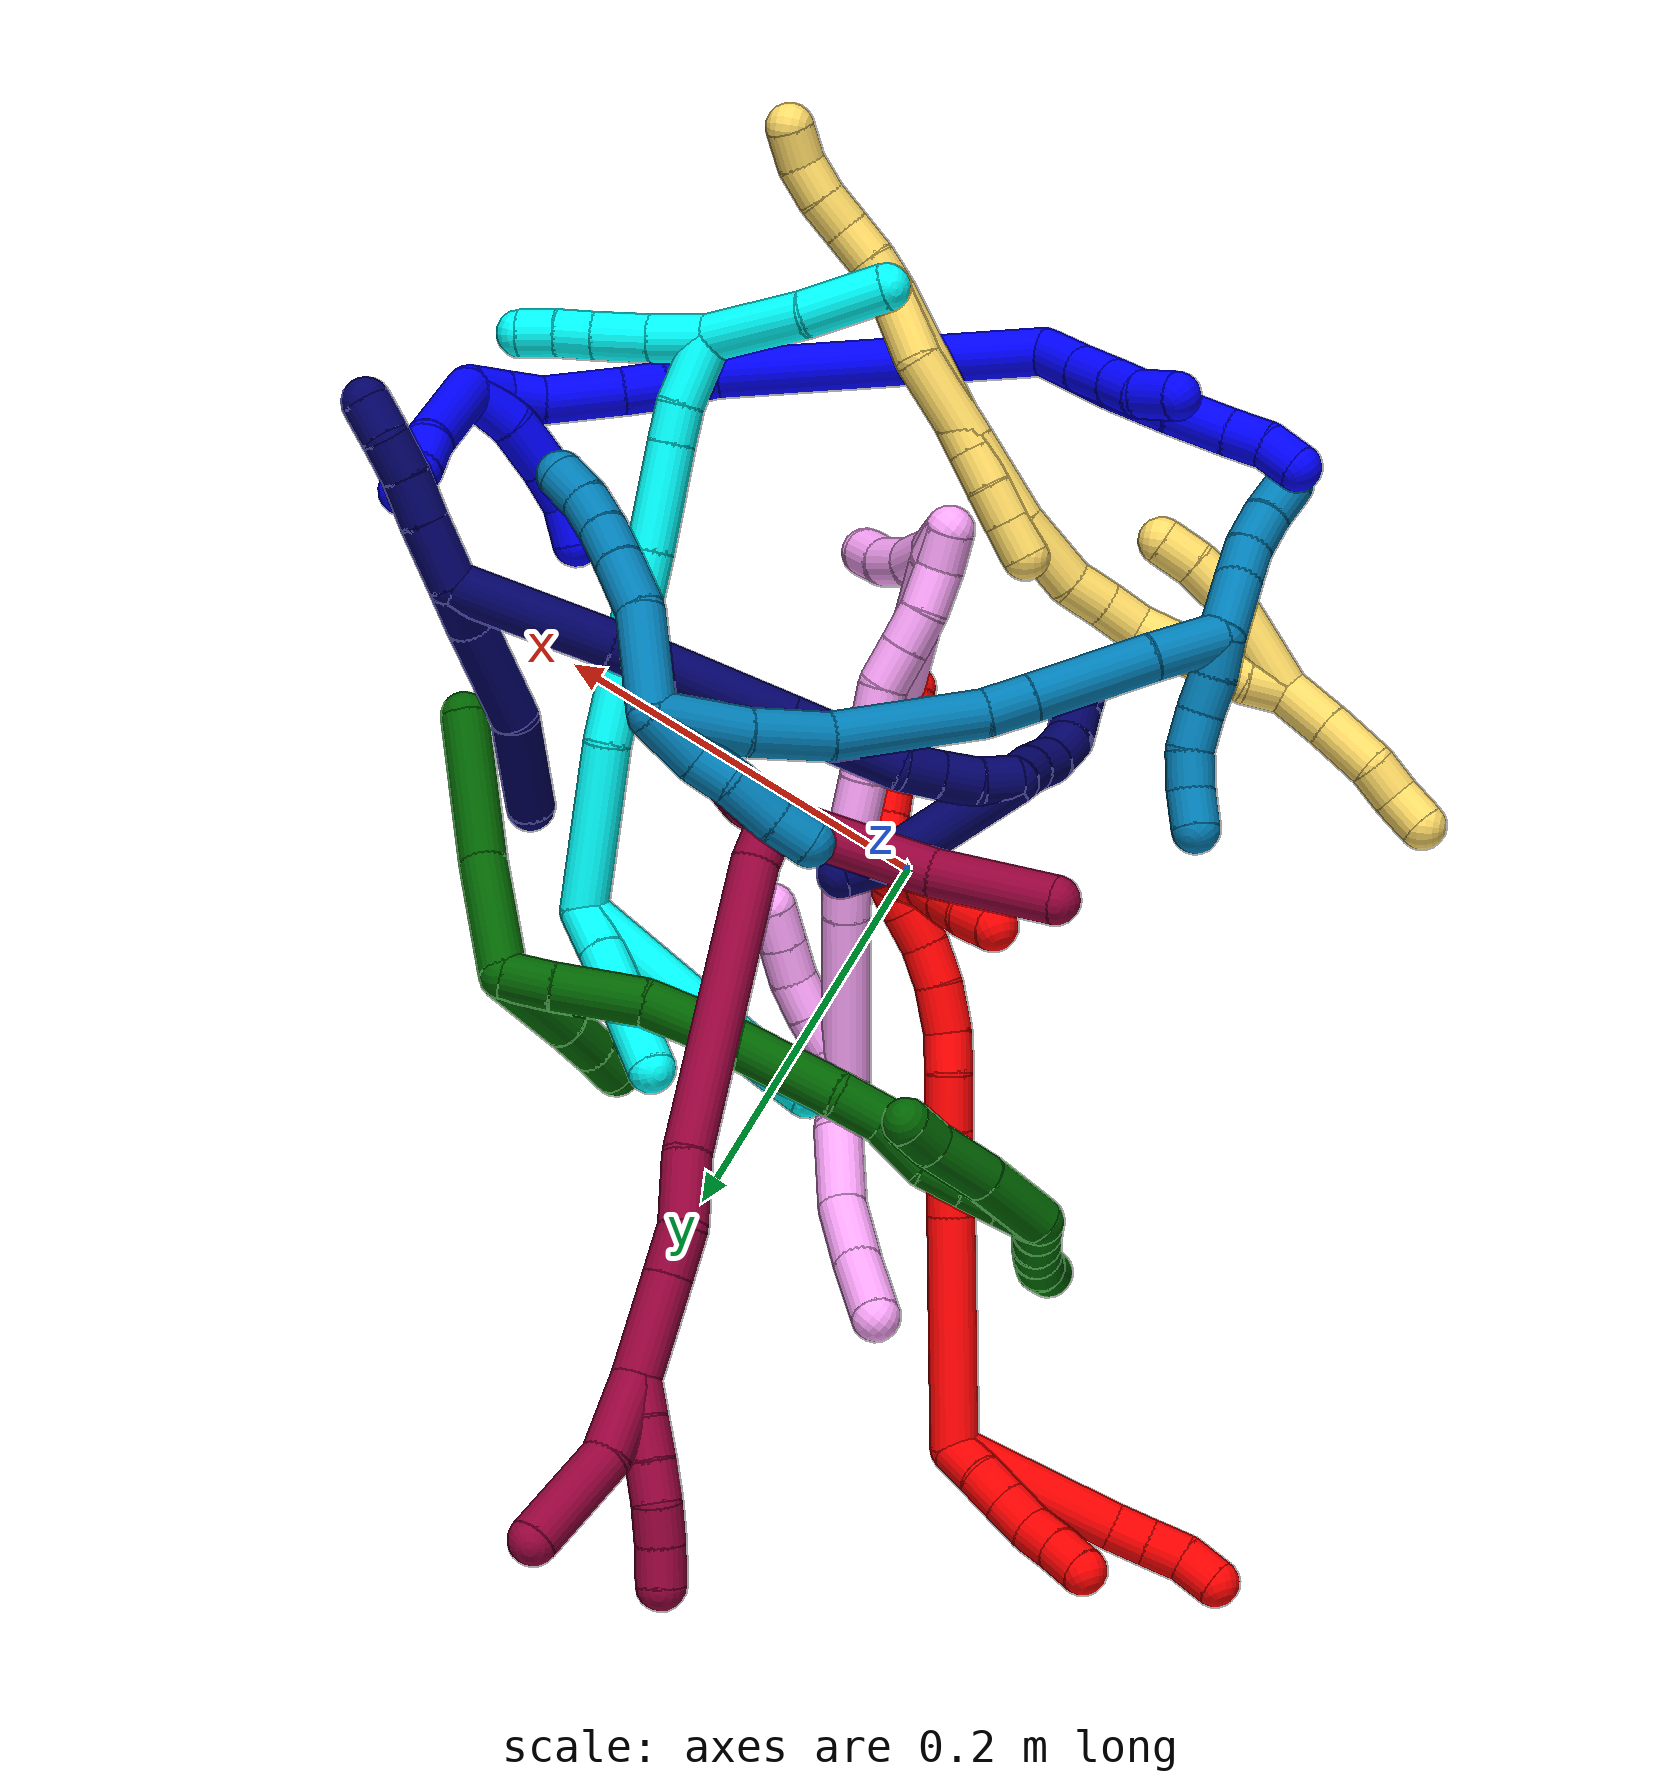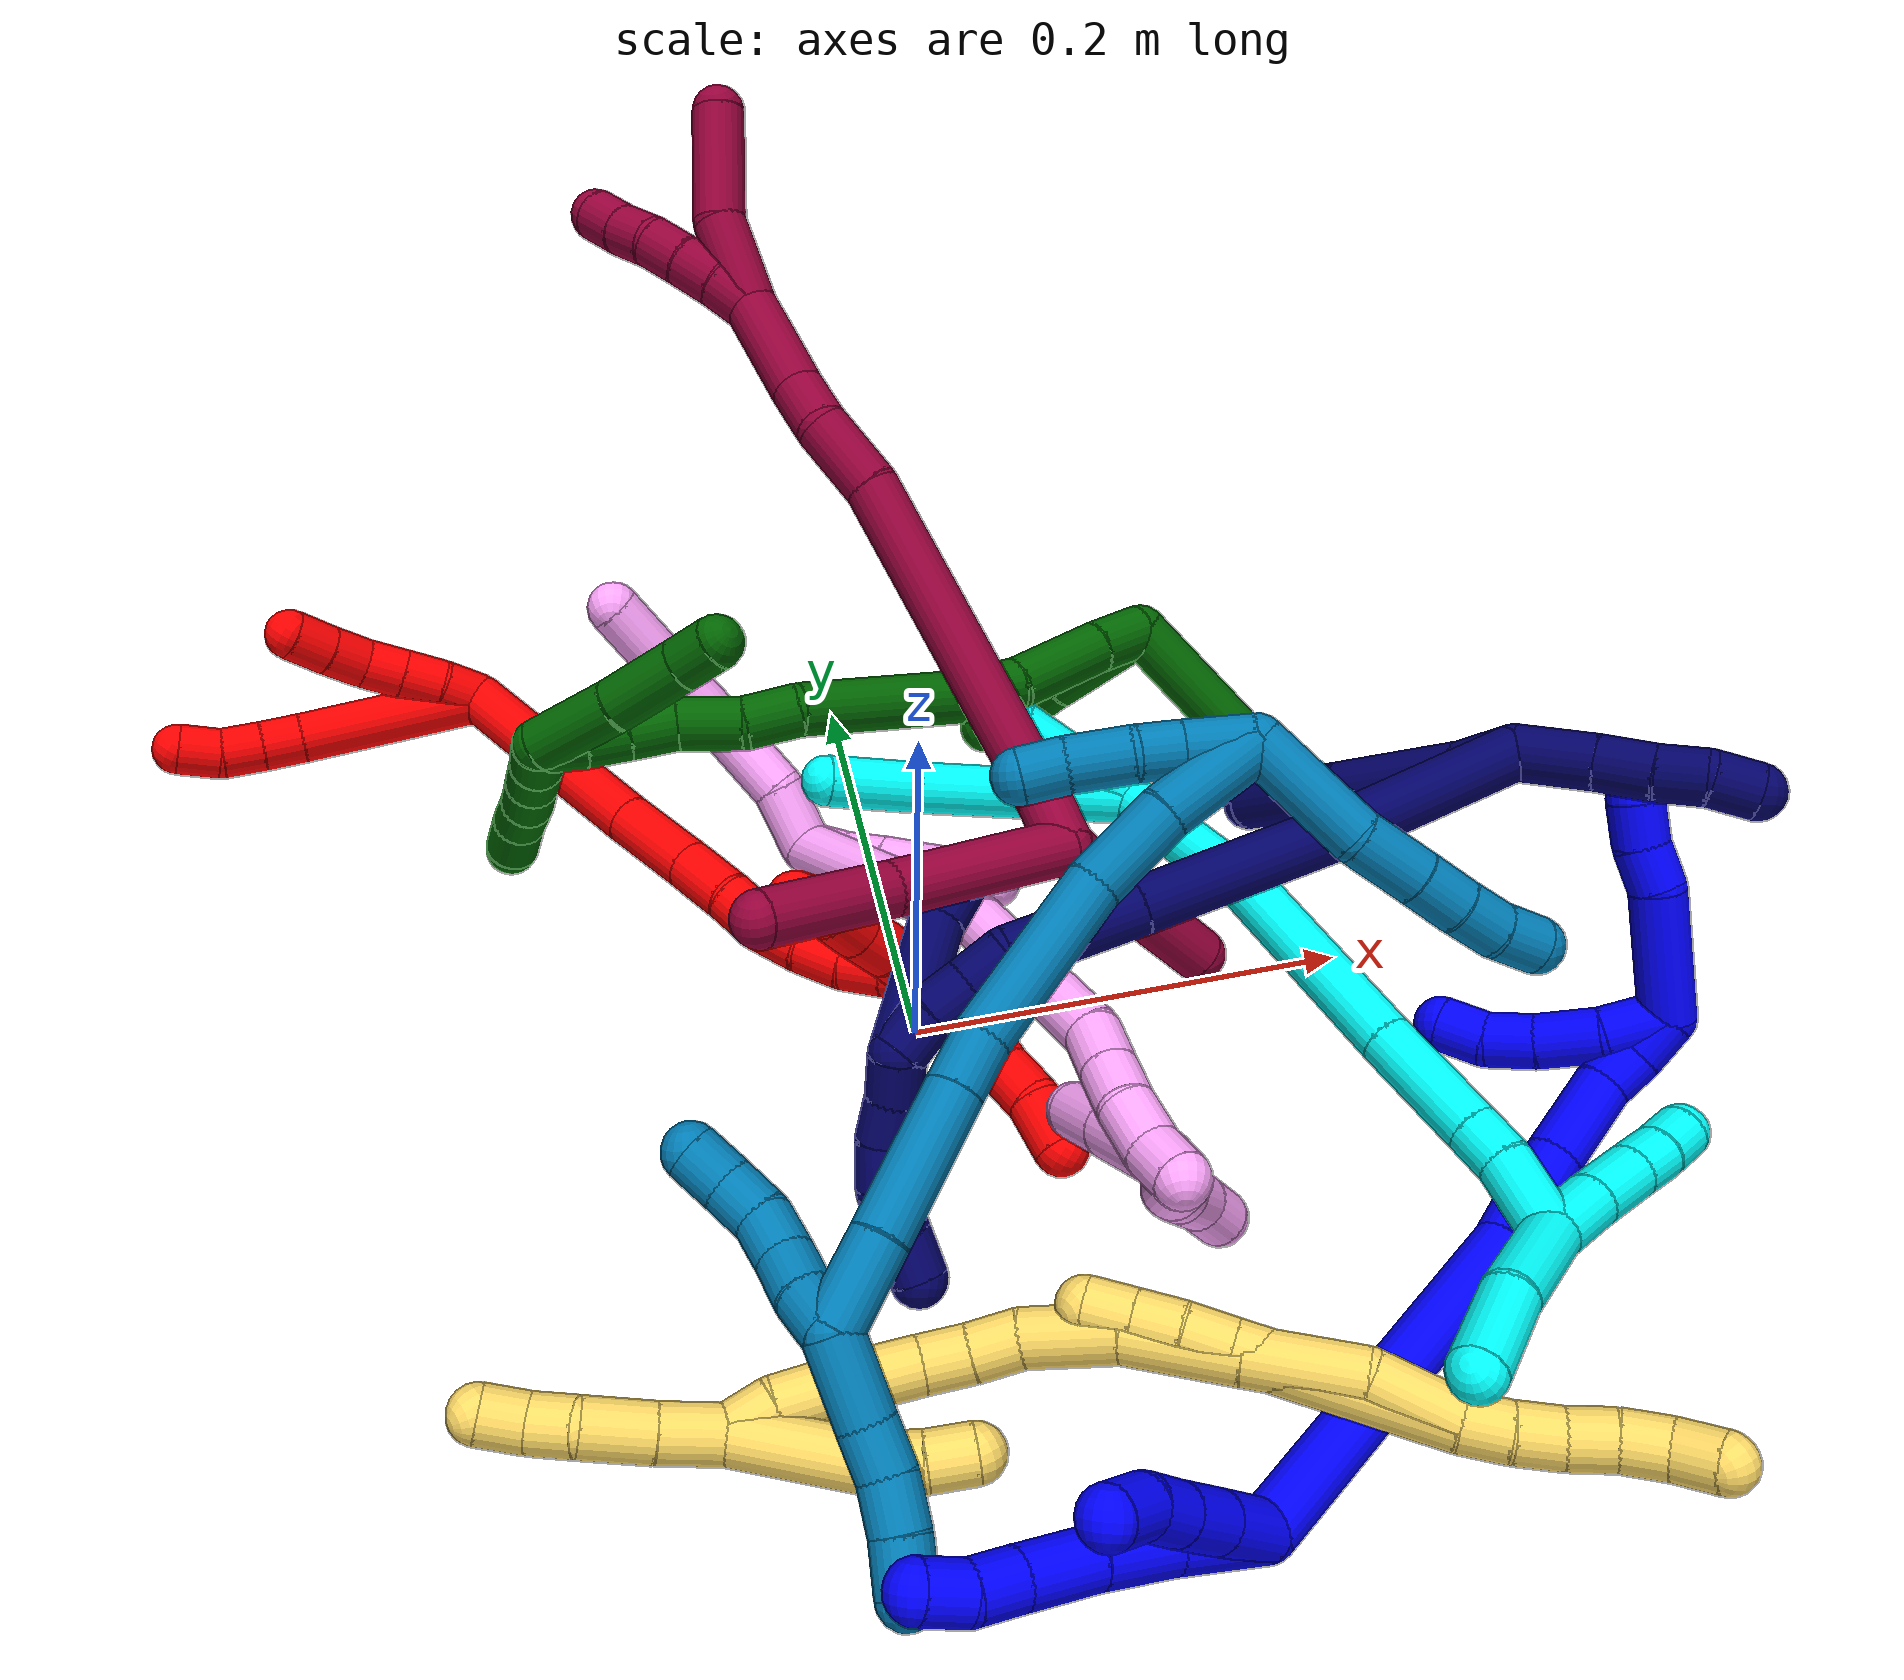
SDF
<sdf version="1.7">
 <world name="default">
  <plugin name="TubeGeneratorPlugin" filename="libtube_generator_plugin.so"/>
  <model name="photoneo_s_sensor">
   <static>1</static>
   <pose>0 0 2 1.57079 1.57079 3.14159</pose>
   <link name="link">
    <inertial><mass>0.1</mass></inertial>
    <sensor name="sensor" type="depth">
     <update_rate>30</update_rate>
     <camera>
      <horizontal_fov>1.22</horizontal_fov>
      <image><width>1920</width><height>1200</height><format>B8G8R8</format></image>
      <clip><near>0.1</near><far>4</far></clip>
      <depth_camera><output>points</output></depth_camera>
     </camera>
     <plugin name="camera_plugin" filename="libgazebo_ros_depth_camera.so">
      <baseline>0.2</baseline>
      <alwaysOn>1</alwaysOn>
      <updateRate>0.0</updateRate>
      <cameraName>camera_ir</cameraName>
      <imageTopicName>/camera/color/image_raw</imageTopicName>
      <cameraInfoTopicName>/camera/color/camera_info</cameraInfoTopicName>
      <depthImageTopicName>/camera/depth/image_raw</depthImageTopicName>
      <depthImageCameraInfoTopicName>/camera/depth/camera_info</depthImageCameraInfoTopicName>
      <pointCloudTopicName>/camera/depth/points</pointCloudTopicName>
      <frameName>fr_optical</frameName>
      <pointCloudCutoff>0.1</pointCloudCutoff>
      <pointCloudCutoffMax>2.0</pointCloudCutoffMax>
      <distortionK1>0</distortionK1>
      <distortionK2>0</distortionK2>
      <distortionK3>0</distortionK3>
      <distortionT1>0</distortionT1>
      <distortionT2>0</distortionT2>
      <CxPrime>0</CxPrime>
      <Cx>0</Cx>
      <Cy>0</Cy>
      <focalLength>0</focalLength>
      <hackBaseline>0</hackBaseline>
     </plugin>
    </sensor>
   </link>
  </model>
  <gravity>0 0 -9.8</gravity>
  <magnetic_field>6e-06 2.3e-05 -4.2e-05</magnetic_field>
  <atmosphere type="adiabatic"/>
  <physics name="default_physics" default="0" type="ode">
   <max_step_size>0.003</max_step_size>
   <real_time_factor>1</real_time_factor>
   <real_time_update_rate>1000</real_time_update_rate>
   <max_contacts>10000</max_contacts>
   <ode>
    <solver>
     <type>quick</type>
     <iters>100</iters>
     <sor>1.3</sor>
     <use_dynamic_moi_rescaling>0</use_dynamic_moi_rescaling>
    </solver>
    <constraints>
     <contact_max_correcting_vel>0</contact_max_correcting_vel>
     <contact_surface_layer>0.001</contact_surface_layer>
     <cfm>0</cfm>
     <erp>0.2</erp>
    </constraints>
   </ode>
  </physics>
  <scene><ambient>0.4 0.4 0.4 1</ambient><background>0.7 0.7 0.7 1</background><shadows>0</shadows></scene>
  <audio><device>default</device></audio>
  <spherical_coordinates>
   <surface_model>EARTH_WGS84</surface_model>
   <latitude_deg>0</latitude_deg>
   <longitude_deg>0</longitude_deg>
   <elevation>0</elevation>
   <heading_deg>0</heading_deg>
  </spherical_coordinates>
  <model name="bin">
   <static>1</static>
   <link name="bottom">
    <collision name="collision-bottom">
     <pose>0 0 -0.01 0 -0 0</pose>
     <geometry><box><size>0.8 0.6 0.02</size></box></geometry>
     <surface>
      <friction><ode><mu>100</mu><mu2>100</mu2></ode></friction>
      <contact><collide_bitmask>65535</collide_bitmask></contact>
     </surface>
    </collision>
   </link>
   <link name="west_wall">
    <collision name="collision-west_wall">
     <pose>-0.41 0 0.1 0 -0 0</pose>
     <geometry><box><size>0.02 0.6 0.2</size></box></geometry>
     <surface>
      <friction><ode><mu>100</mu><mu2>100</mu2></ode></friction>
      <contact><collide_bitmask>65535</collide_bitmask></contact>
     </surface>
    </collision>
   </link>
   <link name="east_wall">
    <collision name="collision-east_wall">
     <pose>0.41 0 0.1 0 -0 0</pose>
     <geometry><box><size>0.02 0.6 0.2</size></box></geometry>
     <surface>
      <friction><ode><mu>100</mu><mu2>100</mu2></ode></friction>
      <contact><collide_bitmask>65535</collide_bitmask></contact>
     </surface>
    </collision>
   </link>
   <link name="south_wall">
    <collision name="collision-south_wall">
     <pose>0 -0.31 0.1 0 -0 0</pose>
     <geometry><box><size>0.8 0.02 0.2</size></box></geometry>
     <surface>
      <friction><ode><mu>100</mu><mu2>100</mu2></ode></friction>
      <contact><collide_bitmask>65535</collide_bitmask></contact>
     </surface>
    </collision>
   </link>
   <link name="north_wall">
    <collision name="collision-north_wall">
     <pose>0 0.31 0.1 0 -0 0</pose>
     <geometry><box><size>0.8 0.02 0.2</size></box></geometry>
     <surface>
      <friction><ode><mu>100</mu><mu2>100</mu2></ode></friction>
      <contact><collide_bitmask>65535</collide_bitmask></contact>
     </surface>
    </collision>
   </link>
  </model>
  <model name="1">
   <static>0</static>
   <link name="1">
    <collision name="collision-cylinder-e_1_2_8">
     <pose>-0.013292 -0.016624 0.002134 1.4431 -0.670501 -0.594869</pose>
     <geometry><cylinder><radius>0.0125</radius><length>0.042782</length></cylinder></geometry>
     <surface>
      <friction><ode><mu>1.16</mu><mu2>1.16</mu2><slip1>0</slip1><slip2>0</slip2></ode></friction>
      <contact><ode><kp>1e+06</kp><kd>1</kd><max_vel>0</max_vel><min_depth>0.001</min_depth></ode></contact>
     </surface>
    </collision>
    <visual name="visual-cylinder-e_1_2_8">
     <pose>-0.013292 -0.016624 0.002134 1.4431 -0.670501 -0.594869</pose>
     <geometry><cylinder><radius>0.0125</radius><length>0.042782</length></cylinder></geometry>
     <material><ambient>0 0 1 1</ambient></material>
    </visual>
    <collision name="collision-cylinder-e_2_8_9">
     <pose>-0.037803 -0.045818 0.006668 1.38218 -0.719754 -0.603463</pose>
     <geometry><cylinder><radius>0.0125</radius><length>0.034038</length></cylinder></geometry>
     <surface>
      <friction><ode><mu>1.16</mu><mu2>1.16</mu2><slip1>0</slip1><slip2>0</slip2></ode></friction>
      <contact><ode><kp>1e+06</kp><kd>1</kd><max_vel>0</max_vel><min_depth>0.001</min_depth></ode></contact>
     </surface>
    </collision>
    <visual name="visual-cylinder-e_2_8_9">
     <pose>-0.037803 -0.045818 0.006668 1.38218 -0.719754 -0.603463</pose>
     <geometry><cylinder><radius>0.0125</radius><length>0.034038</length></cylinder></geometry>
     <material><ambient>0 0 1 1</ambient></material>
    </visual>
    <collision name="collision-cylinder-e_3_9_10">
     <pose>-0.059003 -0.070607 0.012563 1.29221 -0.665801 -0.510113</pose>
     <geometry><cylinder><radius>0.0125</radius><length>0.032318</length></cylinder></geometry>
     <surface>
      <friction><ode><mu>1.16</mu><mu2>1.16</mu2><slip1>0</slip1><slip2>0</slip2></ode></friction>
      <contact><ode><kp>1e+06</kp><kd>1</kd><max_vel>0</max_vel><min_depth>0.001</min_depth></ode></contact>
     </surface>
    </collision>
    <visual name="visual-cylinder-e_3_9_10">
     <pose>-0.059003 -0.070607 0.012563 1.29221 -0.665801 -0.510113</pose>
     <geometry><cylinder><radius>0.0125</radius><length>0.032318</length></cylinder></geometry>
     <material><ambient>0 0 1 1</ambient></material>
    </visual>
    <collision name="collision-cylinder-e_4_10_11">
     <pose>-0.075788 -0.090379 0.018299 1.2823 -0.712213 -0.541579</pose>
     <geometry><cylinder><radius>0.0125</radius><length>0.020822</length></cylinder></geometry>
     <surface>
      <friction><ode><mu>1.16</mu><mu2>1.16</mu2><slip1>0</slip1><slip2>0</slip2></ode></friction>
      <contact><ode><kp>1e+06</kp><kd>1</kd><max_vel>0</max_vel><min_depth>0.001</min_depth></ode></contact>
     </surface>
    </collision>
    <visual name="visual-cylinder-e_4_10_11">
     <pose>-0.075788 -0.090379 0.018299 1.2823 -0.712213 -0.541579</pose>
     <geometry><cylinder><radius>0.0125</radius><length>0.020822</length></cylinder></geometry>
     <material><ambient>0 0 1 1</ambient></material>
    </visual>
    <collision name="collision-cylinder-e_5_11_6">
     <pose>-0.08814 -0.10627 0.020207 1.61086 -0.586874 -0.609439</pose>
     <geometry><cylinder><radius>0.0125</radius><length>0.02004</length></cylinder></geometry>
     <surface>
      <friction><ode><mu>1.16</mu><mu2>1.16</mu2><slip1>0</slip1><slip2>0</slip2></ode></friction>
      <contact><ode><kp>1e+06</kp><kd>1</kd><max_vel>0</max_vel><min_depth>0.001</min_depth></ode></contact>
     </surface>
    </collision>
    <visual name="visual-cylinder-e_5_11_6">
     <pose>-0.08814 -0.10627 0.020207 1.61086 -0.586874 -0.609439</pose>
     <geometry><cylinder><radius>0.0125</radius><length>0.02004</length></cylinder></geometry>
     <material><ambient>0 0 1 1</ambient></material>
    </visual>
    <collision name="collision-cylinder-e_1_2_12">
     <pose>-0.012804 -0.008032 -0.002711 1.89627 -0.985976 -1.28483</pose>
     <geometry><cylinder><radius>0.0125</radius><length>0.030711</length></cylinder></geometry>
     <surface>
      <friction><ode><mu>1.16</mu><mu2>1.16</mu2><slip1>0</slip1><slip2>0</slip2></ode></friction>
      <contact><ode><kp>1e+06</kp><kd>1</kd><max_vel>0</max_vel><min_depth>0.001</min_depth></ode></contact>
     </surface>
    </collision>
    <visual name="visual-cylinder-e_1_2_12">
     <pose>-0.012804 -0.008032 -0.002711 1.89627 -0.985976 -1.28483</pose>
     <geometry><cylinder><radius>0.0125</radius><length>0.030711</length></cylinder></geometry>
     <material><ambient>0 0 1 1</ambient></material>
    </visual>
    <collision name="collision-cylinder-e_2_12_13">
     <pose>-0.03655 -0.022387 -0.007626 1.90637 -1.02163 -1.33599</pose>
     <geometry><cylinder><radius>0.0125</radius><length>0.025658</length></cylinder></geometry>
     <surface>
      <friction><ode><mu>1.16</mu><mu2>1.16</mu2><slip1>0</slip1><slip2>0</slip2></ode></friction>
      <contact><ode><kp>1e+06</kp><kd>1</kd><max_vel>0</max_vel><min_depth>0.001</min_depth></ode></contact>
     </surface>
    </collision>
    <visual name="visual-cylinder-e_2_12_13">
     <pose>-0.03655 -0.022387 -0.007626 1.90637 -1.02163 -1.33599</pose>
     <geometry><cylinder><radius>0.0125</radius><length>0.025658</length></cylinder></geometry>
     <material><ambient>0 0 1 1</ambient></material>
    </visual>
    <collision name="collision-cylinder-e_3_13_14">
     <pose>-0.05648 -0.03374 -0.01196 1.97099 -1.02469 -1.40738</pose>
     <geometry><cylinder><radius>0.0125</radius><length>0.021034</length></cylinder></geometry>
     <surface>
      <friction><ode><mu>1.16</mu><mu2>1.16</mu2><slip1>0</slip1><slip2>0</slip2></ode></friction>
      <contact><ode><kp>1e+06</kp><kd>1</kd><max_vel>0</max_vel><min_depth>0.001</min_depth></ode></contact>
     </surface>
    </collision>
    <visual name="visual-cylinder-e_3_13_14">
     <pose>-0.05648 -0.03374 -0.01196 1.97099 -1.02469 -1.40738</pose>
     <geometry><cylinder><radius>0.0125</radius><length>0.021034</length></cylinder></geometry>
     <material><ambient>0 0 1 1</ambient></material>
    </visual>
    <collision name="collision-cylinder-e_4_14_5">
     <pose>-0.075611 -0.043574 -0.012788 1.30646 -1.11474 -0.890183</pose>
     <geometry><cylinder><radius>0.0125</radius><length>0.022597</length></cylinder></geometry>
     <surface>
      <friction><ode><mu>1.16</mu><mu2>1.16</mu2><slip1>0</slip1><slip2>0</slip2></ode></friction>
      <contact><ode><kp>1e+06</kp><kd>1</kd><max_vel>0</max_vel><min_depth>0.001</min_depth></ode></contact>
     </surface>
    </collision>
    <visual name="visual-cylinder-e_4_14_5">
     <pose>-0.075611 -0.043574 -0.012788 1.30646 -1.11474 -0.890183</pose>
     <geometry><cylinder><radius>0.0125</radius><length>0.022597</length></cylinder></geometry>
     <material><ambient>0 0 1 1</ambient></material>
    </visual>
    <collision name="collision-cylinder-e_1_2_15">
     <pose>0.044549 0.042963 -0.056622 -2.49251 0.559876 -1.41421</pose>
     <geometry><cylinder><radius>0.0125</radius><length>0.167768</length></cylinder></geometry>
     <surface>
      <friction><ode><mu>1.16</mu><mu2>1.16</mu2><slip1>0</slip1><slip2>0</slip2></ode></friction>
      <contact><ode><kp>1e+06</kp><kd>1</kd><max_vel>0</max_vel><min_depth>0.001</min_depth></ode></contact>
     </surface>
    </collision>
    <visual name="visual-cylinder-e_1_2_15">
     <pose>0.044549 0.042963 -0.056622 -2.49251 0.559876 -1.41421</pose>
     <geometry><cylinder><radius>0.0125</radius><length>0.167768</length></cylinder></geometry>
     <material><ambient>0 0 1 1</ambient></material>
    </visual>
    <collision name="collision-cylinder-e_2_15_16">
     <pose>0.096213 0.09086 -0.122879 -2.66825 0.581444 -1.78467</pose>
     <geometry><cylinder><radius>0.0125</radius><length>0.025907</length></cylinder></geometry>
     <surface>
      <friction><ode><mu>1.16</mu><mu2>1.16</mu2><slip1>0</slip1><slip2>0</slip2></ode></friction>
      <contact><ode><kp>1e+06</kp><kd>1</kd><max_vel>0</max_vel><min_depth>0.001</min_depth></ode></contact>
     </surface>
    </collision>
    <visual name="visual-cylinder-e_2_15_16">
     <pose>0.096213 0.09086 -0.122879 -2.66825 0.581444 -1.78467</pose>
     <geometry><cylinder><radius>0.0125</radius><length>0.025907</length></cylinder></geometry>
     <material><ambient>0 0 1 1</ambient></material>
    </visual>
    <collision name="collision-cylinder-e_3_16_17">
     <pose>0.10823 0.10112 -0.141677 -2.61515 0.43332 -1.36984</pose>
     <geometry><cylinder><radius>0.0125</radius><length>0.023356</length></cylinder></geometry>
     <surface>
      <friction><ode><mu>1.16</mu><mu2>1.16</mu2><slip1>0</slip1><slip2>0</slip2></ode></friction>
      <contact><ode><kp>1e+06</kp><kd>1</kd><max_vel>0</max_vel><min_depth>0.001</min_depth></ode></contact>
     </surface>
    </collision>
    <visual name="visual-cylinder-e_3_16_17">
     <pose>0.10823 0.10112 -0.141677 -2.61515 0.43332 -1.36984</pose>
     <geometry><cylinder><radius>0.0125</radius><length>0.023356</length></cylinder></geometry>
     <material><ambient>0 0 1 1</ambient></material>
    </visual>
    <collision name="collision-cylinder-e_4_17_18">
     <pose>0.121093 0.116513 -0.16718 -2.58938 0.393139 -1.22524</pose>
     <geometry><cylinder><radius>0.0125</radius><length>0.041554</length></cylinder></geometry>
     <surface>
      <friction><ode><mu>1.16</mu><mu2>1.16</mu2><slip1>0</slip1><slip2>0</slip2></ode></friction>
      <contact><ode><kp>1e+06</kp><kd>1</kd><max_vel>0</max_vel><min_depth>0.001</min_depth></ode></contact>
     </surface>
    </collision>
    <visual name="visual-cylinder-e_4_17_18">
     <pose>0.121093 0.116513 -0.16718 -2.58938 0.393139 -1.22524</pose>
     <geometry><cylinder><radius>0.0125</radius><length>0.041554</length></cylinder></geometry>
     <material><ambient>0 0 1 1</ambient></material>
    </visual>
    <collision name="collision-cylinder-e_5_18_19">
     <pose>0.13077 0.133427 -0.190688 -2.37923 0.171535 -0.422648</pose>
     <geometry><cylinder><radius>0.0125</radius><length>0.020122</length></cylinder></geometry>
     <surface>
      <friction><ode><mu>1.16</mu><mu2>1.16</mu2><slip1>0</slip1><slip2>0</slip2></ode></friction>
      <contact><ode><kp>1e+06</kp><kd>1</kd><max_vel>0</max_vel><min_depth>0.001</min_depth></ode></contact>
     </surface>
    </collision>
    <visual name="visual-cylinder-e_5_18_19">
     <pose>0.13077 0.133427 -0.190688 -2.37923 0.171535 -0.422648</pose>
     <geometry><cylinder><radius>0.0125</radius><length>0.020122</length></cylinder></geometry>
     <material><ambient>0 0 1 1</ambient></material>
    </visual>
    <collision name="collision-cylinder-e_6_19_1">
     <pose>0.131047 0.146721 -0.206207 -2.48401 -0.135639 0.393035</pose>
     <geometry><cylinder><radius>0.0125</radius><length>0.021294</length></cylinder></geometry>
     <surface>
      <friction><ode><mu>1.16</mu><mu2>1.16</mu2><slip1>0</slip1><slip2>0</slip2></ode></friction>
      <contact><ode><kp>1e+06</kp><kd>1</kd><max_vel>0</max_vel><min_depth>0.001</min_depth></ode></contact>
     </surface>
    </collision>
    <visual name="visual-cylinder-e_6_19_1">
     <pose>0.131047 0.146721 -0.206207 -2.48401 -0.135639 0.393035</pose>
     <geometry><cylinder><radius>0.0125</radius><length>0.021294</length></cylinder></geometry>
     <material><ambient>0 0 1 1</ambient></material>
    </visual>
    <collision name="collision-cylinder-e_1_1_20">
     <pose>0.116433 0.149737 -0.2412 3.0135 -0.455974 -2.60223</pose>
     <geometry><cylinder><radius>0.0125</radius><length>0.059841</length></cylinder></geometry>
     <surface>
      <friction><ode><mu>1.16</mu><mu2>1.16</mu2><slip1>0</slip1><slip2>0</slip2></ode></friction>
      <contact><ode><kp>1e+06</kp><kd>1</kd><max_vel>0</max_vel><min_depth>0.001</min_depth></ode></contact>
     </surface>
    </collision>
    <visual name="visual-cylinder-e_1_1_20">
     <pose>0.116433 0.149737 -0.2412 3.0135 -0.455974 -2.60223</pose>
     <geometry><cylinder><radius>0.0125</radius><length>0.059841</length></cylinder></geometry>
     <material><ambient>0 0 1 1</ambient></material>
    </visual>
    <collision name="collision-cylinder-e_2_20_21">
     <pose>0.100506 0.142647 -0.276809 2.75411 -0.276831 -1.23484</pose>
     <geometry><cylinder><radius>0.0125</radius><length>0.020132</length></cylinder></geometry>
     <surface>
      <friction><ode><mu>1.16</mu><mu2>1.16</mu2><slip1>0</slip1><slip2>0</slip2></ode></friction>
      <contact><ode><kp>1e+06</kp><kd>1</kd><max_vel>0</max_vel><min_depth>0.001</min_depth></ode></contact>
     </surface>
    </collision>
    <visual name="visual-cylinder-e_2_20_21">
     <pose>0.100506 0.142647 -0.276809 2.75411 -0.276831 -1.23484</pose>
     <geometry><cylinder><radius>0.0125</radius><length>0.020132</length></cylinder></geometry>
     <material><ambient>0 0 1 1</ambient></material>
    </visual>
    <collision name="collision-cylinder-e_3_21_4">
     <pose>0.094288 0.137356 -0.295025 2.96699 -0.353577 -2.2305</pose>
     <geometry><cylinder><radius>0.0125</radius><length>0.020027</length></cylinder></geometry>
     <surface>
      <friction><ode><mu>1.16</mu><mu2>1.16</mu2><slip1>0</slip1><slip2>0</slip2></ode></friction>
      <contact><ode><kp>1e+06</kp><kd>1</kd><max_vel>0</max_vel><min_depth>0.001</min_depth></ode></contact>
     </surface>
    </collision>
    <visual name="visual-cylinder-e_3_21_4">
     <pose>0.094288 0.137356 -0.295025 2.96699 -0.353577 -2.2305</pose>
     <geometry><cylinder><radius>0.0125</radius><length>0.020027</length></cylinder></geometry>
     <material><ambient>0 0 1 1</ambient></material>
    </visual>
    <collision name="collision-cylinder-e_1_1_22">
     <pose>0.129662 0.139802 -0.210023 1.24375 0.003854 0.002763</pose>
     <geometry><cylinder><radius>0.0125</radius><length>0.02823</length></cylinder></geometry>
     <surface>
      <friction><ode><mu>1.16</mu><mu2>1.16</mu2><slip1>0</slip1><slip2>0</slip2></ode></friction>
      <contact><ode><kp>1e+06</kp><kd>1</kd><max_vel>0</max_vel><min_depth>0.001</min_depth></ode></contact>
     </surface>
    </collision>
    <visual name="visual-cylinder-e_1_1_22">
     <pose>0.129662 0.139802 -0.210023 1.24375 0.003854 0.002763</pose>
     <geometry><cylinder><radius>0.0125</radius><length>0.02823</length></cylinder></geometry>
     <material><ambient>0 0 1 1</ambient></material>
    </visual>
    <collision name="collision-cylinder-e_2_22_23">
     <pose>0.132551 0.112475 -0.203365 1.41986 0.198068 0.170366</pose>
     <geometry><cylinder><radius>0.0125</radius><length>0.028805</length></cylinder></geometry>
     <surface>
      <friction><ode><mu>1.16</mu><mu2>1.16</mu2><slip1>0</slip1><slip2>0</slip2></ode></friction>
      <contact><ode><kp>1e+06</kp><kd>1</kd><max_vel>0</max_vel><min_depth>0.001</min_depth></ode></contact>
     </surface>
    </collision>
    <visual name="visual-cylinder-e_2_22_23">
     <pose>0.132551 0.112475 -0.203365 1.41986 0.198068 0.170366</pose>
     <geometry><cylinder><radius>0.0125</radius><length>0.028805</length></cylinder></geometry>
     <material><ambient>0 0 1 1</ambient></material>
    </visual>
    <collision name="collision-cylinder-e_3_23_24">
     <pose>0.137019 0.087647 -0.201123 1.55992 0.149247 0.147638</pose>
     <geometry><cylinder><radius>0.0125</radius><length>0.02198</length></cylinder></geometry>
     <surface>
      <friction><ode><mu>1.16</mu><mu2>1.16</mu2><slip1>0</slip1><slip2>0</slip2></ode></friction>
      <contact><ode><kp>1e+06</kp><kd>1</kd><max_vel>0</max_vel><min_depth>0.001</min_depth></ode></contact>
     </surface>
    </collision>
    <visual name="visual-cylinder-e_3_23_24">
     <pose>0.137019 0.087647 -0.201123 1.55992 0.149247 0.147638</pose>
     <geometry><cylinder><radius>0.0125</radius><length>0.02198</length></cylinder></geometry>
     <material><ambient>0 0 1 1</ambient></material>
    </visual>
    <collision name="collision-cylinder-e_4_24_3">
     <pose>0.14064 0.066965 -0.204136 1.87953 0.190543 0.260084</pose>
     <geometry><cylinder><radius>0.0125</radius><length>0.020985</length></cylinder></geometry>
     <surface>
      <friction><ode><mu>1.16</mu><mu2>1.16</mu2><slip1>0</slip1><slip2>0</slip2></ode></friction>
      <contact><ode><kp>1e+06</kp><kd>1</kd><max_vel>0</max_vel><min_depth>0.001</min_depth></ode></contact>
     </surface>
    </collision>
    <visual name="visual-cylinder-e_4_24_3">
     <pose>0.14064 0.066965 -0.204136 1.87953 0.190543 0.260084</pose>
     <geometry><cylinder><radius>0.0125</radius><length>0.020985</length></cylinder></geometry>
     <material><ambient>0 0 1 1</ambient></material>
    </visual>
    <collision name="collision-sphere-3">
     <pose>0.142627 0.057149 -0.207266 0 -0 0</pose>
     <geometry><sphere><radius>0.0125</radius></sphere></geometry>
     <surface>
      <friction><ode><mu>1.16</mu><mu2>1.16</mu2><slip1>0</slip1><slip2>0</slip2></ode></friction>
      <contact><ode><kp>1e+06</kp><kd>1</kd><max_vel>0</max_vel><min_depth>0.001</min_depth></ode></contact>
     </surface>
    </collision>
    <visual name="visual-sphere-3">
     <pose>0.142627 0.057149 -0.207266 0 -0 0</pose>
     <geometry><sphere><radius>0.0125</radius></sphere></geometry>
     <material><ambient>0 0 1 1</ambient></material>
    </visual>
    <collision name="collision-sphere-24">
     <pose>0.138653 0.07678 -0.201005 0 -0 0</pose>
     <geometry><sphere><radius>0.0125</radius></sphere></geometry>
     <surface>
      <friction><ode><mu>1.16</mu><mu2>1.16</mu2><slip1>0</slip1><slip2>0</slip2></ode></friction>
      <contact><ode><kp>1e+06</kp><kd>1</kd><max_vel>0</max_vel><min_depth>0.001</min_depth></ode></contact>
     </surface>
    </collision>
    <visual name="visual-sphere-24">
     <pose>0.138653 0.07678 -0.201005 0 -0 0</pose>
     <geometry><sphere><radius>0.0125</radius></sphere></geometry>
     <material><ambient>0 0 1 1</ambient></material>
    </visual>
    <collision name="collision-sphere-23">
     <pose>0.135385 0.098515 -0.201242 0 -0 0</pose>
     <geometry><sphere><radius>0.0125</radius></sphere></geometry>
     <surface>
      <friction><ode><mu>1.16</mu><mu2>1.16</mu2><slip1>0</slip1><slip2>0</slip2></ode></friction>
      <contact><ode><kp>1e+06</kp><kd>1</kd><max_vel>0</max_vel><min_depth>0.001</min_depth></ode></contact>
     </surface>
    </collision>
    <visual name="visual-sphere-23">
     <pose>0.135385 0.098515 -0.201242 0 -0 0</pose>
     <geometry><sphere><radius>0.0125</radius></sphere></geometry>
     <material><ambient>0 0 1 1</ambient></material>
    </visual>
    <collision name="collision-sphere-22">
     <pose>0.129717 0.126435 -0.205488 0 -0 0</pose>
     <geometry><sphere><radius>0.0125</radius></sphere></geometry>
     <surface>
      <friction><ode><mu>1.16</mu><mu2>1.16</mu2><slip1>0</slip1><slip2>0</slip2></ode></friction>
      <contact><ode><kp>1e+06</kp><kd>1</kd><max_vel>0</max_vel><min_depth>0.001</min_depth></ode></contact>
     </surface>
    </collision>
    <visual name="visual-sphere-22">
     <pose>0.129717 0.126435 -0.205488 0 -0 0</pose>
     <geometry><sphere><radius>0.0125</radius></sphere></geometry>
     <material><ambient>0 0 1 1</ambient></material>
    </visual>
    <collision name="collision-sphere-4">
     <pose>0.090821 0.135724 -0.304276 0 -0 0</pose>
     <geometry><sphere><radius>0.0125</radius></sphere></geometry>
     <surface>
      <friction><ode><mu>1.16</mu><mu2>1.16</mu2><slip1>0</slip1><slip2>0</slip2></ode></friction>
      <contact><ode><kp>1e+06</kp><kd>1</kd><max_vel>0</max_vel><min_depth>0.001</min_depth></ode></contact>
     </surface>
    </collision>
    <visual name="visual-sphere-4">
     <pose>0.090821 0.135724 -0.304276 0 -0 0</pose>
     <geometry><sphere><radius>0.0125</radius></sphere></geometry>
     <material><ambient>0 0 1 1</ambient></material>
    </visual>
    <collision name="collision-sphere-21">
     <pose>0.097755 0.138988 -0.285774 0 -0 0</pose>
     <geometry><sphere><radius>0.0125</radius></sphere></geometry>
     <surface>
      <friction><ode><mu>1.16</mu><mu2>1.16</mu2><slip1>0</slip1><slip2>0</slip2></ode></friction>
      <contact><ode><kp>1e+06</kp><kd>1</kd><max_vel>0</max_vel><min_depth>0.001</min_depth></ode></contact>
     </surface>
    </collision>
    <visual name="visual-sphere-21">
     <pose>0.097755 0.138988 -0.285774 0 -0 0</pose>
     <geometry><sphere><radius>0.0125</radius></sphere></geometry>
     <material><ambient>0 0 1 1</ambient></material>
    </visual>
    <collision name="collision-sphere-20">
     <pose>0.103258 0.146305 -0.267844 0 -0 0</pose>
     <geometry><sphere><radius>0.0125</radius></sphere></geometry>
     <surface>
      <friction><ode><mu>1.16</mu><mu2>1.16</mu2><slip1>0</slip1><slip2>0</slip2></ode></friction>
      <contact><ode><kp>1e+06</kp><kd>1</kd><max_vel>0</max_vel><min_depth>0.001</min_depth></ode></contact>
     </surface>
    </collision>
    <visual name="visual-sphere-20">
     <pose>0.103258 0.146305 -0.267844 0 -0 0</pose>
     <geometry><sphere><radius>0.0125</radius></sphere></geometry>
     <material><ambient>0 0 1 1</ambient></material>
    </visual>
    <collision name="collision-sphere-6">
     <pose>-0.093689 -0.114607 0.019873 0 -0 0</pose>
     <geometry><sphere><radius>0.0125</radius></sphere></geometry>
     <surface>
      <friction><ode><mu>1.16</mu><mu2>1.16</mu2><slip1>0</slip1><slip2>0</slip2></ode></friction>
      <contact><ode><kp>1e+06</kp><kd>1</kd><max_vel>0</max_vel><min_depth>0.001</min_depth></ode></contact>
     </surface>
    </collision>
    <visual name="visual-sphere-6">
     <pose>-0.093689 -0.114607 0.019873 0 -0 0</pose>
     <geometry><sphere><radius>0.0125</radius></sphere></geometry>
     <material><ambient>0 0 1 1</ambient></material>
    </visual>
    <collision name="collision-sphere-11">
     <pose>-0.082592 -0.097934 0.020541 0 -0 0</pose>
     <geometry><sphere><radius>0.0125</radius></sphere></geometry>
     <surface>
      <friction><ode><mu>1.16</mu><mu2>1.16</mu2><slip1>0</slip1><slip2>0</slip2></ode></friction>
      <contact><ode><kp>1e+06</kp><kd>1</kd><max_vel>0</max_vel><min_depth>0.001</min_depth></ode></contact>
     </surface>
    </collision>
    <visual name="visual-sphere-11">
     <pose>-0.082592 -0.097934 0.020541 0 -0 0</pose>
     <geometry><sphere><radius>0.0125</radius></sphere></geometry>
     <material><ambient>0 0 1 1</ambient></material>
    </visual>
    <collision name="collision-sphere-10">
     <pose>-0.068984 -0.082825 0.016057 0 -0 0</pose>
     <geometry><sphere><radius>0.0125</radius></sphere></geometry>
     <surface>
      <friction><ode><mu>1.16</mu><mu2>1.16</mu2><slip1>0</slip1><slip2>0</slip2></ode></friction>
      <contact><ode><kp>1e+06</kp><kd>1</kd><max_vel>0</max_vel><min_depth>0.001</min_depth></ode></contact>
     </surface>
    </collision>
    <visual name="visual-sphere-10">
     <pose>-0.068984 -0.082825 0.016057 0 -0 0</pose>
     <geometry><sphere><radius>0.0125</radius></sphere></geometry>
     <material><ambient>0 0 1 1</ambient></material>
    </visual>
    <collision name="collision-sphere-9">
     <pose>-0.049022 -0.058389 0.009068 0 -0 0</pose>
     <geometry><sphere><radius>0.0125</radius></sphere></geometry>
     <surface>
      <friction><ode><mu>1.16</mu><mu2>1.16</mu2><slip1>0</slip1><slip2>0</slip2></ode></friction>
      <contact><ode><kp>1e+06</kp><kd>1</kd><max_vel>0</max_vel><min_depth>0.001</min_depth></ode></contact>
     </surface>
    </collision>
    <visual name="visual-sphere-9">
     <pose>-0.049022 -0.058389 0.009068 0 -0 0</pose>
     <geometry><sphere><radius>0.0125</radius></sphere></geometry>
     <material><ambient>0 0 1 1</ambient></material>
    </visual>
    <collision name="collision-sphere-2">
     <geometry><sphere><radius>0.0125</radius></sphere></geometry>
     <surface>
      <friction><ode><mu>1.16</mu><mu2>1.16</mu2><slip1>0</slip1><slip2>0</slip2></ode></friction>
      <contact><ode><kp>1e+06</kp><kd>1</kd><max_vel>0</max_vel><min_depth>0.001</min_depth></ode></contact>
     </surface>
    </collision>
    <visual name="visual-sphere-2">
     <geometry><sphere><radius>0.0125</radius></sphere></geometry>
     <material><ambient>0 0 1 1</ambient></material>
    </visual>
    <collision name="collision-sphere-19">
     <pose>0.132487 0.140273 -0.197858 0 -0 0</pose>
     <geometry><sphere><radius>0.0125</radius></sphere></geometry>
     <surface>
      <friction><ode><mu>1.16</mu><mu2>1.16</mu2><slip1>0</slip1><slip2>0</slip2></ode></friction>
      <contact><ode><kp>1e+06</kp><kd>1</kd><max_vel>0</max_vel><min_depth>0.001</min_depth></ode></contact>
     </surface>
    </collision>
    <visual name="visual-sphere-19">
     <pose>0.132487 0.140273 -0.197858 0 -0 0</pose>
     <geometry><sphere><radius>0.0125</radius></sphere></geometry>
     <material><ambient>0 0 1 1</ambient></material>
    </visual>
    <collision name="collision-sphere-8">
     <pose>-0.026584 -0.033247 0.004269 0 -0 0</pose>
     <geometry><sphere><radius>0.0125</radius></sphere></geometry>
     <surface>
      <friction><ode><mu>1.16</mu><mu2>1.16</mu2><slip1>0</slip1><slip2>0</slip2></ode></friction>
      <contact><ode><kp>1e+06</kp><kd>1</kd><max_vel>0</max_vel><min_depth>0.001</min_depth></ode></contact>
     </surface>
    </collision>
    <visual name="visual-sphere-8">
     <pose>-0.026584 -0.033247 0.004269 0 -0 0</pose>
     <geometry><sphere><radius>0.0125</radius></sphere></geometry>
     <material><ambient>0 0 1 1</ambient></material>
    </visual>
    <collision name="collision-sphere-12">
     <pose>-0.025608 -0.016064 -0.005421 0 -0 0</pose>
     <geometry><sphere><radius>0.0125</radius></sphere></geometry>
     <surface>
      <friction><ode><mu>1.16</mu><mu2>1.16</mu2><slip1>0</slip1><slip2>0</slip2></ode></friction>
      <contact><ode><kp>1e+06</kp><kd>1</kd><max_vel>0</max_vel><min_depth>0.001</min_depth></ode></contact>
     </surface>
    </collision>
    <visual name="visual-sphere-12">
     <pose>-0.025608 -0.016064 -0.005421 0 -0 0</pose>
     <geometry><sphere><radius>0.0125</radius></sphere></geometry>
     <material><ambient>0 0 1 1</ambient></material>
    </visual>
    <collision name="collision-sphere-13">
     <pose>-0.047493 -0.02871 -0.009832 0 -0 0</pose>
     <geometry><sphere><radius>0.0125</radius></sphere></geometry>
     <surface>
      <friction><ode><mu>1.16</mu><mu2>1.16</mu2><slip1>0</slip1><slip2>0</slip2></ode></friction>
      <contact><ode><kp>1e+06</kp><kd>1</kd><max_vel>0</max_vel><min_depth>0.001</min_depth></ode></contact>
     </surface>
    </collision>
    <visual name="visual-sphere-13">
     <pose>-0.047493 -0.02871 -0.009832 0 -0 0</pose>
     <geometry><sphere><radius>0.0125</radius></sphere></geometry>
     <material><ambient>0 0 1 1</ambient></material>
    </visual>
    <collision name="collision-sphere-14">
     <pose>-0.065467 -0.038771 -0.014088 0 -0 0</pose>
     <geometry><sphere><radius>0.0125</radius></sphere></geometry>
     <surface>
      <friction><ode><mu>1.16</mu><mu2>1.16</mu2><slip1>0</slip1><slip2>0</slip2></ode></friction>
      <contact><ode><kp>1e+06</kp><kd>1</kd><max_vel>0</max_vel><min_depth>0.001</min_depth></ode></contact>
     </surface>
    </collision>
    <visual name="visual-sphere-14">
     <pose>-0.065467 -0.038771 -0.014088 0 -0 0</pose>
     <geometry><sphere><radius>0.0125</radius></sphere></geometry>
     <material><ambient>0 0 1 1</ambient></material>
    </visual>
    <collision name="collision-sphere-5">
     <pose>-0.085755 -0.048377 -0.011488 0 -0 0</pose>
     <geometry><sphere><radius>0.0125</radius></sphere></geometry>
     <surface>
      <friction><ode><mu>1.16</mu><mu2>1.16</mu2><slip1>0</slip1><slip2>0</slip2></ode></friction>
      <contact><ode><kp>1e+06</kp><kd>1</kd><max_vel>0</max_vel><min_depth>0.001</min_depth></ode></contact>
     </surface>
    </collision>
    <visual name="visual-sphere-5">
     <pose>-0.085755 -0.048377 -0.011488 0 -0 0</pose>
     <geometry><sphere><radius>0.0125</radius></sphere></geometry>
     <material><ambient>0 0 1 1</ambient></material>
    </visual>
    <collision name="collision-sphere-15">
     <pose>0.089098 0.085925 -0.113245 0 -0 0</pose>
     <geometry><sphere><radius>0.0125</radius></sphere></geometry>
     <surface>
      <friction><ode><mu>1.16</mu><mu2>1.16</mu2><slip1>0</slip1><slip2>0</slip2></ode></friction>
      <contact><ode><kp>1e+06</kp><kd>1</kd><max_vel>0</max_vel><min_depth>0.001</min_depth></ode></contact>
     </surface>
    </collision>
    <visual name="visual-sphere-15">
     <pose>0.089098 0.085925 -0.113245 0 -0 0</pose>
     <geometry><sphere><radius>0.0125</radius></sphere></geometry>
     <material><ambient>0 0 1 1</ambient></material>
    </visual>
    <collision name="collision-sphere-16">
     <pose>0.103327 0.095794 -0.132514 0 -0 0</pose>
     <geometry><sphere><radius>0.0125</radius></sphere></geometry>
     <surface>
      <friction><ode><mu>1.16</mu><mu2>1.16</mu2><slip1>0</slip1><slip2>0</slip2></ode></friction>
      <contact><ode><kp>1e+06</kp><kd>1</kd><max_vel>0</max_vel><min_depth>0.001</min_depth></ode></contact>
     </surface>
    </collision>
    <visual name="visual-sphere-16">
     <pose>0.103327 0.095794 -0.132514 0 -0 0</pose>
     <geometry><sphere><radius>0.0125</radius></sphere></geometry>
     <material><ambient>0 0 1 1</ambient></material>
    </visual>
    <collision name="collision-sphere-17">
     <pose>0.113134 0.106445 -0.150841 0 -0 0</pose>
     <geometry><sphere><radius>0.0125</radius></sphere></geometry>
     <surface>
      <friction><ode><mu>1.16</mu><mu2>1.16</mu2><slip1>0</slip1><slip2>0</slip2></ode></friction>
      <contact><ode><kp>1e+06</kp><kd>1</kd><max_vel>0</max_vel><min_depth>0.001</min_depth></ode></contact>
     </surface>
    </collision>
    <visual name="visual-sphere-17">
     <pose>0.113134 0.106445 -0.150841 0 -0 0</pose>
     <geometry><sphere><radius>0.0125</radius></sphere></geometry>
     <material><ambient>0 0 1 1</ambient></material>
    </visual>
    <collision name="collision-sphere-18">
     <pose>0.129053 0.12658 -0.183519 0 -0 0</pose>
     <geometry><sphere><radius>0.0125</radius></sphere></geometry>
     <surface>
      <friction><ode><mu>1.16</mu><mu2>1.16</mu2><slip1>0</slip1><slip2>0</slip2></ode></friction>
      <contact><ode><kp>1e+06</kp><kd>1</kd><max_vel>0</max_vel><min_depth>0.001</min_depth></ode></contact>
     </surface>
    </collision>
    <visual name="visual-sphere-18">
     <pose>0.129053 0.12658 -0.183519 0 -0 0</pose>
     <geometry><sphere><radius>0.0125</radius></sphere></geometry>
     <material><ambient>0 0 1 1</ambient></material>
    </visual>
    <collision name="collision-sphere-1">
     <pose>0.129608 0.153169 -0.214557 0 -0 0</pose>
     <geometry><sphere><radius>0.0125</radius></sphere></geometry>
     <surface>
      <friction><ode><mu>1.16</mu><mu2>1.16</mu2><slip1>0</slip1><slip2>0</slip2></ode></friction>
      <contact><ode><kp>1e+06</kp><kd>1</kd><max_vel>0</max_vel><min_depth>0.001</min_depth></ode></contact>
     </surface>
    </collision>
    <visual name="visual-sphere-1">
     <pose>0.129608 0.153169 -0.214557 0 -0 0</pose>
     <geometry><sphere><radius>0.0125</radius></sphere></geometry>
     <material><ambient>0 0 1 1</ambient></material>
    </visual>
    <inertial>
     <pose>0.047913 0.048794 -0.10251 0 -0 0</pose>
     <mass>0.75</mass>
     <inertia>
      <ixx>-0.000309</ixx>
      <ixy>0</ixy>
      <ixz>0</ixz>
      <iyy>-0.000267</iyy>
      <iyz>0</iyz>
      <izz>-0.000391</izz>
     </inertia>
    </inertial>
   </link>
   <pose>0.079255 -0.261864 0.012192 2.82964 0.986659 0.904335</pose>
  </model>
  <model name="2">
   <static>0</static>
   <link name="2">
    <collision name="collision-cylinder-e_1_2_8">
     <pose>-0.01622 -0.027544 0.031265 0.722207 -0.371228 -0.141595</pose>
     <geometry><cylinder><radius>0.0125</radius><length>0.089425</length></cylinder></geometry>
     <surface>
      <friction><ode><mu>1.16</mu><mu2>1.16</mu2><slip1>0</slip1><slip2>0</slip2></ode></friction>
      <contact><ode><kp>1e+06</kp><kd>1</kd><max_vel>0</max_vel><min_depth>0.001</min_depth></ode></contact>
     </surface>
    </collision>
    <visual name="visual-cylinder-e_1_2_8">
     <pose>-0.01622 -0.027544 0.031265 0.722207 -0.371228 -0.141595</pose>
     <geometry><cylinder><radius>0.0125</radius><length>0.089425</length></cylinder></geometry>
     <material><ambient>1 0 0 1</ambient></material>
    </visual>
    <collision name="collision-cylinder-e_2_8_9">
     <pose>-0.035395 -0.06168 0.069481 0.75896 -0.299208 -0.120081</pose>
     <geometry><cylinder><radius>0.0125</radius><length>0.020052</length></cylinder></geometry>
     <surface>
      <friction><ode><mu>1.16</mu><mu2>1.16</mu2><slip1>0</slip1><slip2>0</slip2></ode></friction>
      <contact><ode><kp>1e+06</kp><kd>1</kd><max_vel>0</max_vel><min_depth>0.001</min_depth></ode></contact>
     </surface>
    </collision>
    <visual name="visual-cylinder-e_2_8_9">
     <pose>-0.035395 -0.06168 0.069481 0.75896 -0.299208 -0.120081</pose>
     <geometry><cylinder><radius>0.0125</radius><length>0.020052</length></cylinder></geometry>
     <material><ambient>1 0 0 1</ambient></material>
    </visual>
    <collision name="collision-cylinder-e_3_9_10">
     <pose>-0.040736 -0.075056 0.083415 0.770819 -0.240266 -0.097869</pose>
     <geometry><cylinder><radius>0.0125</radius><length>0.020046</length></cylinder></geometry>
     <surface>
      <friction><ode><mu>1.16</mu><mu2>1.16</mu2><slip1>0</slip1><slip2>0</slip2></ode></friction>
      <contact><ode><kp>1e+06</kp><kd>1</kd><max_vel>0</max_vel><min_depth>0.001</min_depth></ode></contact>
     </surface>
    </collision>
    <visual name="visual-cylinder-e_3_9_10">
     <pose>-0.040736 -0.075056 0.083415 0.770819 -0.240266 -0.097869</pose>
     <geometry><cylinder><radius>0.0125</radius><length>0.020046</length></cylinder></geometry>
     <material><ambient>1 0 0 1</ambient></material>
    </visual>
    <collision name="collision-cylinder-e_4_10_6">
     <pose>-0.043921 -0.086902 0.099261 0.519075 -0.078185 -0.02077</pose>
     <geometry><cylinder><radius>0.0125</radius><length>0.020476</length></cylinder></geometry>
     <surface>
      <friction><ode><mu>1.16</mu><mu2>1.16</mu2><slip1>0</slip1><slip2>0</slip2></ode></friction>
      <contact><ode><kp>1e+06</kp><kd>1</kd><max_vel>0</max_vel><min_depth>0.001</min_depth></ode></contact>
     </surface>
    </collision>
    <visual name="visual-cylinder-e_4_10_6">
     <pose>-0.043921 -0.086902 0.099261 0.519075 -0.078185 -0.02077</pose>
     <geometry><cylinder><radius>0.0125</radius><length>0.020476</length></cylinder></geometry>
     <material><ambient>1 0 0 1</ambient></material>
    </visual>
    <collision name="collision-cylinder-e_1_2_11">
     <pose>0.001577 -0.004049 0.009007 0.422487 0.158381 0.034032</pose>
     <geometry><cylinder><radius>0.0125</radius><length>0.02</length></cylinder></geometry>
     <surface>
      <friction><ode><mu>1.16</mu><mu2>1.16</mu2><slip1>0</slip1><slip2>0</slip2></ode></friction>
      <contact><ode><kp>1e+06</kp><kd>1</kd><max_vel>0</max_vel><min_depth>0.001</min_depth></ode></contact>
     </surface>
    </collision>
    <visual name="visual-cylinder-e_1_2_11">
     <pose>0.001577 -0.004049 0.009007 0.422487 0.158381 0.034032</pose>
     <geometry><cylinder><radius>0.0125</radius><length>0.02</length></cylinder></geometry>
     <material><ambient>1 0 0 1</ambient></material>
    </visual>
    <collision name="collision-cylinder-e_2_11_12">
     <pose>0.003198 -0.011859 0.027279 0.385601 0.004371 0.000853</pose>
     <geometry><cylinder><radius>0.0125</radius><length>0.02</length></cylinder></geometry>
     <surface>
      <friction><ode><mu>1.16</mu><mu2>1.16</mu2><slip1>0</slip1><slip2>0</slip2></ode></friction>
      <contact><ode><kp>1e+06</kp><kd>1</kd><max_vel>0</max_vel><min_depth>0.001</min_depth></ode></contact>
     </surface>
    </collision>
    <visual name="visual-cylinder-e_2_11_12">
     <pose>0.003198 -0.011859 0.027279 0.385601 0.004371 0.000853</pose>
     <geometry><cylinder><radius>0.0125</radius><length>0.02</length></cylinder></geometry>
     <material><ambient>1 0 0 1</ambient></material>
    </visual>
    <collision name="collision-cylinder-e_3_12_13">
     <pose>0.003317 -0.019464 0.045776 0.394583 0.007527 0.001505</pose>
     <geometry><cylinder><radius>0.0125</radius><length>0.02</length></cylinder></geometry>
     <surface>
      <friction><ode><mu>1.16</mu><mu2>1.16</mu2><slip1>0</slip1><slip2>0</slip2></ode></friction>
      <contact><ode><kp>1e+06</kp><kd>1</kd><max_vel>0</max_vel><min_depth>0.001</min_depth></ode></contact>
     </surface>
    </collision>
    <visual name="visual-cylinder-e_3_12_13">
     <pose>0.003317 -0.019464 0.045776 0.394583 0.007527 0.001505</pose>
     <geometry><cylinder><radius>0.0125</radius><length>0.02</length></cylinder></geometry>
     <material><ambient>1 0 0 1</ambient></material>
    </visual>
    <collision name="collision-cylinder-e_4_13_14">
     <pose>0.006144 -0.028358 0.063188 0.552926 0.278749 0.079563</pose>
     <geometry><cylinder><radius>0.0125</radius><length>0.02</length></cylinder></geometry>
     <surface>
      <friction><ode><mu>1.16</mu><mu2>1.16</mu2><slip1>0</slip1><slip2>0</slip2></ode></friction>
      <contact><ode><kp>1e+06</kp><kd>1</kd><max_vel>0</max_vel><min_depth>0.001</min_depth></ode></contact>
     </surface>
    </collision>
    <visual name="visual-cylinder-e_4_13_14">
     <pose>0.006144 -0.028358 0.063188 0.552926 0.278749 0.079563</pose>
     <geometry><cylinder><radius>0.0125</radius><length>0.02</length></cylinder></geometry>
     <material><ambient>1 0 0 1</ambient></material>
    </visual>
    <collision name="collision-cylinder-e_5_14_5">
     <pose>0.011798 -0.038038 0.079744 0.505222 0.294507 0.076536</pose>
     <geometry><cylinder><radius>0.0125</radius><length>0.02</length></cylinder></geometry>
     <surface>
      <friction><ode><mu>1.16</mu><mu2>1.16</mu2><slip1>0</slip1><slip2>0</slip2></ode></friction>
      <contact><ode><kp>1e+06</kp><kd>1</kd><max_vel>0</max_vel><min_depth>0.001</min_depth></ode></contact>
     </surface>
    </collision>
    <visual name="visual-cylinder-e_5_14_5">
     <pose>0.011798 -0.038038 0.079744 0.505222 0.294507 0.076536</pose>
     <geometry><cylinder><radius>0.0125</radius><length>0.02</length></cylinder></geometry>
     <material><ambient>1 0 0 1</ambient></material>
    </visual>
    <collision name="collision-cylinder-e_1_2_15">
     <pose>0.015513 -0.024486 -0.052069 2.70203 0.263347 1.0703</pose>
     <geometry><cylinder><radius>0.0125</radius><length>0.119188</length></cylinder></geometry>
     <surface>
      <friction><ode><mu>1.16</mu><mu2>1.16</mu2><slip1>0</slip1><slip2>0</slip2></ode></friction>
      <contact><ode><kp>1e+06</kp><kd>1</kd><max_vel>0</max_vel><min_depth>0.001</min_depth></ode></contact>
     </surface>
    </collision>
    <visual name="visual-cylinder-e_1_2_15">
     <pose>0.015513 -0.024486 -0.052069 2.70203 0.263347 1.0703</pose>
     <geometry><cylinder><radius>0.0125</radius><length>0.119188</length></cylinder></geometry>
     <material><ambient>1 0 0 1</ambient></material>
    </visual>
    <collision name="collision-cylinder-e_2_15_16">
     <pose>0.037434 -0.057777 -0.123055 2.70593 0.29796 1.19176</pose>
     <geometry><cylinder><radius>0.0125</radius><length>0.043655</length></cylinder></geometry>
     <surface>
      <friction><ode><mu>1.16</mu><mu2>1.16</mu2><slip1>0</slip1><slip2>0</slip2></ode></friction>
      <contact><ode><kp>1e+06</kp><kd>1</kd><max_vel>0</max_vel><min_depth>0.001</min_depth></ode></contact>
     </surface>
    </collision>
    <visual name="visual-cylinder-e_2_15_16">
     <pose>0.037434 -0.057777 -0.123055 2.70593 0.29796 1.19176</pose>
     <geometry><cylinder><radius>0.0125</radius><length>0.043655</length></cylinder></geometry>
     <material><ambient>1 0 0 1</ambient></material>
    </visual>
    <collision name="collision-cylinder-e_3_16_17">
     <pose>0.048174 -0.072833 -0.154241 2.6704 0.304789 1.13833</pose>
     <geometry><cylinder><radius>0.0125</radius><length>0.028869</length></cylinder></geometry>
     <surface>
      <friction><ode><mu>1.16</mu><mu2>1.16</mu2><slip1>0</slip1><slip2>0</slip2></ode></friction>
      <contact><ode><kp>1e+06</kp><kd>1</kd><max_vel>0</max_vel><min_depth>0.001</min_depth></ode></contact>
     </surface>
    </collision>
    <visual name="visual-cylinder-e_3_16_17">
     <pose>0.048174 -0.072833 -0.154241 2.6704 0.304789 1.13833</pose>
     <geometry><cylinder><radius>0.0125</radius><length>0.028869</length></cylinder></geometry>
     <material><ambient>1 0 0 1</ambient></material>
    </visual>
    <collision name="collision-cylinder-e_4_17_18">
     <pose>0.054075 -0.083048 -0.176164 2.75195 0.149233 0.724275</pose>
     <geometry><cylinder><radius>0.0125</radius><length>0.021108</length></cylinder></geometry>
     <surface>
      <friction><ode><mu>1.16</mu><mu2>1.16</mu2><slip1>0</slip1><slip2>0</slip2></ode></friction>
      <contact><ode><kp>1e+06</kp><kd>1</kd><max_vel>0</max_vel><min_depth>0.001</min_depth></ode></contact>
     </surface>
    </collision>
    <visual name="visual-cylinder-e_4_17_18">
     <pose>0.054075 -0.083048 -0.176164 2.75195 0.149233 0.724275</pose>
     <geometry><cylinder><radius>0.0125</radius><length>0.021108</length></cylinder></geometry>
     <material><ambient>1 0 0 1</ambient></material>
    </visual>
    <collision name="collision-cylinder-e_5_18_19">
     <pose>0.059798 -0.09015 -0.197182 2.87222 0.338771 1.80149</pose>
     <geometry><cylinder><radius>0.0125</radius><length>0.024998</length></cylinder></geometry>
     <surface>
      <friction><ode><mu>1.16</mu><mu2>1.16</mu2><slip1>0</slip1><slip2>0</slip2></ode></friction>
      <contact><ode><kp>1e+06</kp><kd>1</kd><max_vel>0</max_vel><min_depth>0.001</min_depth></ode></contact>
     </surface>
    </collision>
    <visual name="visual-cylinder-e_5_18_19">
     <pose>0.059798 -0.09015 -0.197182 2.87222 0.338771 1.80149</pose>
     <geometry><cylinder><radius>0.0125</radius><length>0.024998</length></cylinder></geometry>
     <material><ambient>1 0 0 1</ambient></material>
    </visual>
    <collision name="collision-cylinder-e_6_19_20">
     <pose>0.067538 -0.094427 -0.218706 3.02985 0.337427 2.50708</pose>
     <geometry><cylinder><radius>0.0125</radius><length>0.02167</length></cylinder></geometry>
     <surface>
      <friction><ode><mu>1.16</mu><mu2>1.16</mu2><slip1>0</slip1><slip2>0</slip2></ode></friction>
      <contact><ode><kp>1e+06</kp><kd>1</kd><max_vel>0</max_vel><min_depth>0.001</min_depth></ode></contact>
     </surface>
    </collision>
    <visual name="visual-cylinder-e_6_19_20">
     <pose>0.067538 -0.094427 -0.218706 3.02985 0.337427 2.50708</pose>
     <geometry><cylinder><radius>0.0125</radius><length>0.02167</length></cylinder></geometry>
     <material><ambient>1 0 0 1</ambient></material>
    </visual>
    <collision name="collision-cylinder-e_7_20_21">
     <pose>0.075817 -0.095257 -0.237778 -3.10682 0.484309 -3.00102</pose>
     <geometry><cylinder><radius>0.0125</radius><length>0.020152</length></cylinder></geometry>
     <surface>
      <friction><ode><mu>1.16</mu><mu2>1.16</mu2><slip1>0</slip1><slip2>0</slip2></ode></friction>
      <contact><ode><kp>1e+06</kp><kd>1</kd><max_vel>0</max_vel><min_depth>0.001</min_depth></ode></contact>
     </surface>
    </collision>
    <visual name="visual-cylinder-e_7_20_21">
     <pose>0.075817 -0.095257 -0.237778 -3.10682 0.484309 -3.00102</pose>
     <geometry><cylinder><radius>0.0125</radius><length>0.020152</length></cylinder></geometry>
     <material><ambient>1 0 0 1</ambient></material>
    </visual>
    <collision name="collision-cylinder-e_8_21_1">
     <pose>0.085341 -0.094835 -0.255649 -3.12904 0.494712 -3.0919</pose>
     <geometry><cylinder><radius>0.0125</radius><length>0.02036</length></cylinder></geometry>
     <surface>
      <friction><ode><mu>1.16</mu><mu2>1.16</mu2><slip1>0</slip1><slip2>0</slip2></ode></friction>
      <contact><ode><kp>1e+06</kp><kd>1</kd><max_vel>0</max_vel><min_depth>0.001</min_depth></ode></contact>
     </surface>
    </collision>
    <visual name="visual-cylinder-e_8_21_1">
     <pose>0.085341 -0.094835 -0.255649 -3.12904 0.494712 -3.0919</pose>
     <geometry><cylinder><radius>0.0125</radius><length>0.02036</length></cylinder></geometry>
     <material><ambient>1 0 0 1</ambient></material>
    </visual>
    <collision name="collision-cylinder-e_1_1_22">
     <pose>0.096252 -0.100534 -0.259195 0.821004 0.653148 0.292716</pose>
     <geometry><cylinder><radius>0.0125</radius><length>0.02</length></cylinder></geometry>
     <surface>
      <friction><ode><mu>1.16</mu><mu2>1.16</mu2><slip1>0</slip1><slip2>0</slip2></ode></friction>
      <contact><ode><kp>1e+06</kp><kd>1</kd><max_vel>0</max_vel><min_depth>0.001</min_depth></ode></contact>
     </surface>
    </collision>
    <visual name="visual-cylinder-e_1_1_22">
     <pose>0.096252 -0.100534 -0.259195 0.821004 0.653148 0.292716</pose>
     <geometry><cylinder><radius>0.0125</radius><length>0.02</length></cylinder></geometry>
     <material><ambient>1 0 0 1</ambient></material>
    </visual>
    <collision name="collision-cylinder-e_2_22_23">
     <pose>0.108305 -0.111359 -0.247526 0.675372 0.640611 0.231918</pose>
     <geometry><cylinder><radius>0.0125</radius><length>0.02</length></cylinder></geometry>
     <surface>
      <friction><ode><mu>1.16</mu><mu2>1.16</mu2><slip1>0</slip1><slip2>0</slip2></ode></friction>
      <contact><ode><kp>1e+06</kp><kd>1</kd><max_vel>0</max_vel><min_depth>0.001</min_depth></ode></contact>
     </surface>
    </collision>
    <visual name="visual-cylinder-e_2_22_23">
     <pose>0.108305 -0.111359 -0.247526 0.675372 0.640611 0.231918</pose>
     <geometry><cylinder><radius>0.0125</radius><length>0.02</length></cylinder></geometry>
     <material><ambient>1 0 0 1</ambient></material>
    </visual>
    <collision name="collision-cylinder-e_3_23_24">
     <pose>0.118991 -0.120556 -0.233502 0.494229 0.490293 0.126058</pose>
     <geometry><cylinder><radius>0.0125</radius><length>0.02</length></cylinder></geometry>
     <surface>
      <friction><ode><mu>1.16</mu><mu2>1.16</mu2><slip1>0</slip1><slip2>0</slip2></ode></friction>
      <contact><ode><kp>1e+06</kp><kd>1</kd><max_vel>0</max_vel><min_depth>0.001</min_depth></ode></contact>
     </surface>
    </collision>
    <visual name="visual-cylinder-e_3_23_24">
     <pose>0.118991 -0.120556 -0.233502 0.494229 0.490293 0.126058</pose>
     <geometry><cylinder><radius>0.0125</radius><length>0.02</length></cylinder></geometry>
     <material><ambient>1 0 0 1</ambient></material>
    </visual>
    <collision name="collision-cylinder-e_4_24_25">
     <pose>0.129329 -0.129203 -0.218779 0.570366 0.597869 0.180206</pose>
     <geometry><cylinder><radius>0.0125</radius><length>0.02</length></cylinder></geometry>
     <surface>
      <friction><ode><mu>1.16</mu><mu2>1.16</mu2><slip1>0</slip1><slip2>0</slip2></ode></friction>
      <contact><ode><kp>1e+06</kp><kd>1</kd><max_vel>0</max_vel><min_depth>0.001</min_depth></ode></contact>
     </surface>
    </collision>
    <visual name="visual-cylinder-e_4_24_25">
     <pose>0.129329 -0.129203 -0.218779 0.570366 0.597869 0.180206</pose>
     <geometry><cylinder><radius>0.0125</radius><length>0.02</length></cylinder></geometry>
     <material><ambient>1 0 0 1</ambient></material>
    </visual>
    <collision name="collision-cylinder-e_5_25_4">
     <pose>0.138772 -0.139442 -0.204605 0.674963 0.391319 0.138872</pose>
     <geometry><cylinder><radius>0.0125</radius><length>0.02</length></cylinder></geometry>
     <surface>
      <friction><ode><mu>1.16</mu><mu2>1.16</mu2><slip1>0</slip1><slip2>0</slip2></ode></friction>
      <contact><ode><kp>1e+06</kp><kd>1</kd><max_vel>0</max_vel><min_depth>0.001</min_depth></ode></contact>
     </surface>
    </collision>
    <visual name="visual-cylinder-e_5_25_4">
     <pose>0.138772 -0.139442 -0.204605 0.674963 0.391319 0.138872</pose>
     <geometry><cylinder><radius>0.0125</radius><length>0.02</length></cylinder></geometry>
     <material><ambient>1 0 0 1</ambient></material>
    </visual>
    <collision name="collision-cylinder-e_1_1_26">
     <pose>0.088063 -0.099008 -0.279277 2.85736 -0.137281 -0.89583</pose>
     <geometry><cylinder><radius>0.0125</radius><length>0.030855</length></cylinder></geometry>
     <surface>
      <friction><ode><mu>1.16</mu><mu2>1.16</mu2><slip1>0</slip1><slip2>0</slip2></ode></friction>
      <contact><ode><kp>1e+06</kp><kd>1</kd><max_vel>0</max_vel><min_depth>0.001</min_depth></ode></contact>
     </surface>
    </collision>
    <visual name="visual-cylinder-e_1_1_26">
     <pose>0.088063 -0.099008 -0.279277 2.85736 -0.137281 -0.89583</pose>
     <geometry><cylinder><radius>0.0125</radius><length>0.030855</length></cylinder></geometry>
     <material><ambient>1 0 0 1</ambient></material>
    </visual>
    <collision name="collision-cylinder-e_2_26_27">
     <pose>0.085518 -0.108687 -0.303474 2.62652 -0.039647 -0.150267</pose>
     <geometry><cylinder><radius>0.0125</radius><length>0.021914</length></cylinder></geometry>
     <surface>
      <friction><ode><mu>1.16</mu><mu2>1.16</mu2><slip1>0</slip1><slip2>0</slip2></ode></friction>
      <contact><ode><kp>1e+06</kp><kd>1</kd><max_vel>0</max_vel><min_depth>0.001</min_depth></ode></contact>
     </surface>
    </collision>
    <visual name="visual-cylinder-e_2_26_27">
     <pose>0.085518 -0.108687 -0.303474 2.62652 -0.039647 -0.150267</pose>
     <geometry><cylinder><radius>0.0125</radius><length>0.021914</length></cylinder></geometry>
     <material><ambient>1 0 0 1</ambient></material>
    </visual>
    <collision name="collision-cylinder-e_3_27_28">
     <pose>0.087859 -0.120381 -0.321816 2.52098 0.250768 0.749045</pose>
     <geometry><cylinder><radius>0.0125</radius><length>0.022369</length></cylinder></geometry>
     <surface>
      <friction><ode><mu>1.16</mu><mu2>1.16</mu2><slip1>0</slip1><slip2>0</slip2></ode></friction>
      <contact><ode><kp>1e+06</kp><kd>1</kd><max_vel>0</max_vel><min_depth>0.001</min_depth></ode></contact>
     </surface>
    </collision>
    <visual name="visual-cylinder-e_3_27_28">
     <pose>0.087859 -0.120381 -0.321816 2.52098 0.250768 0.749045</pose>
     <geometry><cylinder><radius>0.0125</radius><length>0.022369</length></cylinder></geometry>
     <material><ambient>1 0 0 1</ambient></material>
    </visual>
    <collision name="collision-cylinder-e_4_28_3">
     <pose>0.090248 -0.134243 -0.340489 2.48729 -0.031084 -0.091544</pose>
     <geometry><cylinder><radius>0.0125</radius><length>0.024862</length></cylinder></geometry>
     <surface>
      <friction><ode><mu>1.16</mu><mu2>1.16</mu2><slip1>0</slip1><slip2>0</slip2></ode></friction>
      <contact><ode><kp>1e+06</kp><kd>1</kd><max_vel>0</max_vel><min_depth>0.001</min_depth></ode></contact>
     </surface>
    </collision>
    <visual name="visual-cylinder-e_4_28_3">
     <pose>0.090248 -0.134243 -0.340489 2.48729 -0.031084 -0.091544</pose>
     <geometry><cylinder><radius>0.0125</radius><length>0.024862</length></cylinder></geometry>
     <material><ambient>1 0 0 1</ambient></material>
    </visual>
    <collision name="collision-sphere-3">
     <pose>0.089862 -0.141805 -0.350348 0 -0 0</pose>
     <geometry><sphere><radius>0.0125</radius></sphere></geometry>
     <surface>
      <friction><ode><mu>1.16</mu><mu2>1.16</mu2><slip1>0</slip1><slip2>0</slip2></ode></friction>
      <contact><ode><kp>1e+06</kp><kd>1</kd><max_vel>0</max_vel><min_depth>0.001</min_depth></ode></contact>
     </surface>
    </collision>
    <visual name="visual-sphere-3">
     <pose>0.089862 -0.141805 -0.350348 0 -0 0</pose>
     <geometry><sphere><radius>0.0125</radius></sphere></geometry>
     <material><ambient>1 0 0 1</ambient></material>
    </visual>
    <collision name="collision-sphere-28">
     <pose>0.090634 -0.126681 -0.33063 0 -0 0</pose>
     <geometry><sphere><radius>0.0125</radius></sphere></geometry>
     <surface>
      <friction><ode><mu>1.16</mu><mu2>1.16</mu2><slip1>0</slip1><slip2>0</slip2></ode></friction>
      <contact><ode><kp>1e+06</kp><kd>1</kd><max_vel>0</max_vel><min_depth>0.001</min_depth></ode></contact>
     </surface>
    </collision>
    <visual name="visual-sphere-28">
     <pose>0.090634 -0.126681 -0.33063 0 -0 0</pose>
     <geometry><sphere><radius>0.0125</radius></sphere></geometry>
     <material><ambient>1 0 0 1</ambient></material>
    </visual>
    <collision name="collision-sphere-27">
     <pose>0.085083 -0.11408 -0.313002 0 -0 0</pose>
     <geometry><sphere><radius>0.0125</radius></sphere></geometry>
     <surface>
      <friction><ode><mu>1.16</mu><mu2>1.16</mu2><slip1>0</slip1><slip2>0</slip2></ode></friction>
      <contact><ode><kp>1e+06</kp><kd>1</kd><max_vel>0</max_vel><min_depth>0.001</min_depth></ode></contact>
     </surface>
    </collision>
    <visual name="visual-sphere-27">
     <pose>0.085083 -0.11408 -0.313002 0 -0 0</pose>
     <geometry><sphere><radius>0.0125</radius></sphere></geometry>
     <material><ambient>1 0 0 1</ambient></material>
    </visual>
    <collision name="collision-sphere-26">
     <pose>0.085952 -0.103293 -0.293946 0 -0 0</pose>
     <geometry><sphere><radius>0.0125</radius></sphere></geometry>
     <surface>
      <friction><ode><mu>1.16</mu><mu2>1.16</mu2><slip1>0</slip1><slip2>0</slip2></ode></friction>
      <contact><ode><kp>1e+06</kp><kd>1</kd><max_vel>0</max_vel><min_depth>0.001</min_depth></ode></contact>
     </surface>
    </collision>
    <visual name="visual-sphere-26">
     <pose>0.085952 -0.103293 -0.293946 0 -0 0</pose>
     <geometry><sphere><radius>0.0125</radius></sphere></geometry>
     <material><ambient>1 0 0 1</ambient></material>
    </visual>
    <collision name="collision-sphere-4">
     <pose>0.142586 -0.145219 -0.197388 0 -0 0</pose>
     <geometry><sphere><radius>0.0125</radius></sphere></geometry>
     <surface>
      <friction><ode><mu>1.16</mu><mu2>1.16</mu2><slip1>0</slip1><slip2>0</slip2></ode></friction>
      <contact><ode><kp>1e+06</kp><kd>1</kd><max_vel>0</max_vel><min_depth>0.001</min_depth></ode></contact>
     </surface>
    </collision>
    <visual name="visual-sphere-4">
     <pose>0.142586 -0.145219 -0.197388 0 -0 0</pose>
     <geometry><sphere><radius>0.0125</radius></sphere></geometry>
     <material><ambient>1 0 0 1</ambient></material>
    </visual>
    <collision name="collision-sphere-25">
     <pose>0.134957 -0.133666 -0.211822 0 -0 0</pose>
     <geometry><sphere><radius>0.0125</radius></sphere></geometry>
     <surface>
      <friction><ode><mu>1.16</mu><mu2>1.16</mu2><slip1>0</slip1><slip2>0</slip2></ode></friction>
      <contact><ode><kp>1e+06</kp><kd>1</kd><max_vel>0</max_vel><min_depth>0.001</min_depth></ode></contact>
     </surface>
    </collision>
    <visual name="visual-sphere-25">
     <pose>0.134957 -0.133666 -0.211822 0 -0 0</pose>
     <geometry><sphere><radius>0.0125</radius></sphere></geometry>
     <material><ambient>1 0 0 1</ambient></material>
    </visual>
    <collision name="collision-sphere-24">
     <pose>0.1237 -0.124741 -0.225736 0 -0 0</pose>
     <geometry><sphere><radius>0.0125</radius></sphere></geometry>
     <surface>
      <friction><ode><mu>1.16</mu><mu2>1.16</mu2><slip1>0</slip1><slip2>0</slip2></ode></friction>
      <contact><ode><kp>1e+06</kp><kd>1</kd><max_vel>0</max_vel><min_depth>0.001</min_depth></ode></contact>
     </surface>
    </collision>
    <visual name="visual-sphere-24">
     <pose>0.1237 -0.124741 -0.225736 0 -0 0</pose>
     <geometry><sphere><radius>0.0125</radius></sphere></geometry>
     <material><ambient>1 0 0 1</ambient></material>
    </visual>
    <collision name="collision-sphere-23">
     <pose>0.114282 -0.116371 -0.241268 0 -0 0</pose>
     <geometry><sphere><radius>0.0125</radius></sphere></geometry>
     <surface>
      <friction><ode><mu>1.16</mu><mu2>1.16</mu2><slip1>0</slip1><slip2>0</slip2></ode></friction>
      <contact><ode><kp>1e+06</kp><kd>1</kd><max_vel>0</max_vel><min_depth>0.001</min_depth></ode></contact>
     </surface>
    </collision>
    <visual name="visual-sphere-23">
     <pose>0.114282 -0.116371 -0.241268 0 -0 0</pose>
     <geometry><sphere><radius>0.0125</radius></sphere></geometry>
     <material><ambient>1 0 0 1</ambient></material>
    </visual>
    <collision name="collision-sphere-22">
     <pose>0.102328 -0.106346 -0.253783 0 -0 0</pose>
     <geometry><sphere><radius>0.0125</radius></sphere></geometry>
     <surface>
      <friction><ode><mu>1.16</mu><mu2>1.16</mu2><slip1>0</slip1><slip2>0</slip2></ode></friction>
      <contact><ode><kp>1e+06</kp><kd>1</kd><max_vel>0</max_vel><min_depth>0.001</min_depth></ode></contact>
     </surface>
    </collision>
    <visual name="visual-sphere-22">
     <pose>0.102328 -0.106346 -0.253783 0 -0 0</pose>
     <geometry><sphere><radius>0.0125</radius></sphere></geometry>
     <material><ambient>1 0 0 1</ambient></material>
    </visual>
    <collision name="collision-sphere-1">
     <pose>0.090175 -0.094722 -0.264607 0 -0 0</pose>
     <geometry><sphere><radius>0.0125</radius></sphere></geometry>
     <surface>
      <friction><ode><mu>1.16</mu><mu2>1.16</mu2><slip1>0</slip1><slip2>0</slip2></ode></friction>
      <contact><ode><kp>1e+06</kp><kd>1</kd><max_vel>0</max_vel><min_depth>0.001</min_depth></ode></contact>
     </surface>
    </collision>
    <visual name="visual-sphere-1">
     <pose>0.090175 -0.094722 -0.264607 0 -0 0</pose>
     <geometry><sphere><radius>0.0125</radius></sphere></geometry>
     <material><ambient>1 0 0 1</ambient></material>
    </visual>
    <collision name="collision-sphere-21">
     <pose>0.080508 -0.094947 -0.24669 0 -0 0</pose>
     <geometry><sphere><radius>0.0125</radius></sphere></geometry>
     <surface>
      <friction><ode><mu>1.16</mu><mu2>1.16</mu2><slip1>0</slip1><slip2>0</slip2></ode></friction>
      <contact><ode><kp>1e+06</kp><kd>1</kd><max_vel>0</max_vel><min_depth>0.001</min_depth></ode></contact>
     </surface>
    </collision>
    <visual name="visual-sphere-21">
     <pose>0.080508 -0.094947 -0.24669 0 -0 0</pose>
     <geometry><sphere><radius>0.0125</radius></sphere></geometry>
     <material><ambient>1 0 0 1</ambient></material>
    </visual>
    <collision name="collision-sphere-11">
     <pose>0.003154 -0.008098 0.018013 0 -0 0</pose>
     <geometry><sphere><radius>0.0125</radius></sphere></geometry>
     <surface>
      <friction><ode><mu>1.16</mu><mu2>1.16</mu2><slip1>0</slip1><slip2>0</slip2></ode></friction>
      <contact><ode><kp>1e+06</kp><kd>1</kd><max_vel>0</max_vel><min_depth>0.001</min_depth></ode></contact>
     </surface>
    </collision>
    <visual name="visual-sphere-11">
     <pose>0.003154 -0.008098 0.018013 0 -0 0</pose>
     <geometry><sphere><radius>0.0125</radius></sphere></geometry>
     <material><ambient>1 0 0 1</ambient></material>
    </visual>
    <collision name="collision-sphere-6">
     <pose>-0.04472 -0.091966 0.108124 0 -0 0</pose>
     <geometry><sphere><radius>0.0125</radius></sphere></geometry>
     <surface>
      <friction><ode><mu>1.16</mu><mu2>1.16</mu2><slip1>0</slip1><slip2>0</slip2></ode></friction>
      <contact><ode><kp>1e+06</kp><kd>1</kd><max_vel>0</max_vel><min_depth>0.001</min_depth></ode></contact>
     </surface>
    </collision>
    <visual name="visual-sphere-6">
     <pose>-0.04472 -0.091966 0.108124 0 -0 0</pose>
     <geometry><sphere><radius>0.0125</radius></sphere></geometry>
     <material><ambient>1 0 0 1</ambient></material>
    </visual>
    <collision name="collision-sphere-10">
     <pose>-0.043121 -0.081839 0.090399 0 -0 0</pose>
     <geometry><sphere><radius>0.0125</radius></sphere></geometry>
     <surface>
      <friction><ode><mu>1.16</mu><mu2>1.16</mu2><slip1>0</slip1><slip2>0</slip2></ode></friction>
      <contact><ode><kp>1e+06</kp><kd>1</kd><max_vel>0</max_vel><min_depth>0.001</min_depth></ode></contact>
     </surface>
    </collision>
    <visual name="visual-sphere-10">
     <pose>-0.043121 -0.081839 0.090399 0 -0 0</pose>
     <geometry><sphere><radius>0.0125</radius></sphere></geometry>
     <material><ambient>1 0 0 1</ambient></material>
    </visual>
    <collision name="collision-sphere-9">
     <pose>-0.038351 -0.068273 0.076432 0 -0 0</pose>
     <geometry><sphere><radius>0.0125</radius></sphere></geometry>
     <surface>
      <friction><ode><mu>1.16</mu><mu2>1.16</mu2><slip1>0</slip1><slip2>0</slip2></ode></friction>
      <contact><ode><kp>1e+06</kp><kd>1</kd><max_vel>0</max_vel><min_depth>0.001</min_depth></ode></contact>
     </surface>
    </collision>
    <visual name="visual-sphere-9">
     <pose>-0.038351 -0.068273 0.076432 0 -0 0</pose>
     <geometry><sphere><radius>0.0125</radius></sphere></geometry>
     <material><ambient>1 0 0 1</ambient></material>
    </visual>
    <collision name="collision-sphere-2">
     <geometry><sphere><radius>0.0125</radius></sphere></geometry>
     <surface>
      <friction><ode><mu>1.16</mu><mu2>1.16</mu2><slip1>0</slip1><slip2>0</slip2></ode></friction>
      <contact><ode><kp>1e+06</kp><kd>1</kd><max_vel>0</max_vel><min_depth>0.001</min_depth></ode></contact>
     </surface>
    </collision>
    <visual name="visual-sphere-2">
     <geometry><sphere><radius>0.0125</radius></sphere></geometry>
     <material><ambient>1 0 0 1</ambient></material>
    </visual>
    <collision name="collision-sphere-19">
     <pose>0.063951 -0.093287 -0.208546 0 -0 0</pose>
     <geometry><sphere><radius>0.0125</radius></sphere></geometry>
     <surface>
      <friction><ode><mu>1.16</mu><mu2>1.16</mu2><slip1>0</slip1><slip2>0</slip2></ode></friction>
      <contact><ode><kp>1e+06</kp><kd>1</kd><max_vel>0</max_vel><min_depth>0.001</min_depth></ode></contact>
     </surface>
    </collision>
    <visual name="visual-sphere-19">
     <pose>0.063951 -0.093287 -0.208546 0 -0 0</pose>
     <geometry><sphere><radius>0.0125</radius></sphere></geometry>
     <material><ambient>1 0 0 1</ambient></material>
    </visual>
    <collision name="collision-sphere-8">
     <pose>-0.03244 -0.055087 0.062529 0 -0 0</pose>
     <geometry><sphere><radius>0.0125</radius></sphere></geometry>
     <surface>
      <friction><ode><mu>1.16</mu><mu2>1.16</mu2><slip1>0</slip1><slip2>0</slip2></ode></friction>
      <contact><ode><kp>1e+06</kp><kd>1</kd><max_vel>0</max_vel><min_depth>0.001</min_depth></ode></contact>
     </surface>
    </collision>
    <visual name="visual-sphere-8">
     <pose>-0.03244 -0.055087 0.062529 0 -0 0</pose>
     <geometry><sphere><radius>0.0125</radius></sphere></geometry>
     <material><ambient>1 0 0 1</ambient></material>
    </visual>
    <collision name="collision-sphere-12">
     <pose>0.003242 -0.01562 0.036544 0 -0 0</pose>
     <geometry><sphere><radius>0.0125</radius></sphere></geometry>
     <surface>
      <friction><ode><mu>1.16</mu><mu2>1.16</mu2><slip1>0</slip1><slip2>0</slip2></ode></friction>
      <contact><ode><kp>1e+06</kp><kd>1</kd><max_vel>0</max_vel><min_depth>0.001</min_depth></ode></contact>
     </surface>
    </collision>
    <visual name="visual-sphere-12">
     <pose>0.003242 -0.01562 0.036544 0 -0 0</pose>
     <geometry><sphere><radius>0.0125</radius></sphere></geometry>
     <material><ambient>1 0 0 1</ambient></material>
    </visual>
    <collision name="collision-sphere-13">
     <pose>0.003392 -0.023308 0.055007 0 -0 0</pose>
     <geometry><sphere><radius>0.0125</radius></sphere></geometry>
     <surface>
      <friction><ode><mu>1.16</mu><mu2>1.16</mu2><slip1>0</slip1><slip2>0</slip2></ode></friction>
      <contact><ode><kp>1e+06</kp><kd>1</kd><max_vel>0</max_vel><min_depth>0.001</min_depth></ode></contact>
     </surface>
    </collision>
    <visual name="visual-sphere-13">
     <pose>0.003392 -0.023308 0.055007 0 -0 0</pose>
     <geometry><sphere><radius>0.0125</radius></sphere></geometry>
     <material><ambient>1 0 0 1</ambient></material>
    </visual>
    <collision name="collision-sphere-14">
     <pose>0.008895 -0.033407 0.07137 0 -0 0</pose>
     <geometry><sphere><radius>0.0125</radius></sphere></geometry>
     <surface>
      <friction><ode><mu>1.16</mu><mu2>1.16</mu2><slip1>0</slip1><slip2>0</slip2></ode></friction>
      <contact><ode><kp>1e+06</kp><kd>1</kd><max_vel>0</max_vel><min_depth>0.001</min_depth></ode></contact>
     </surface>
    </collision>
    <visual name="visual-sphere-14">
     <pose>0.008895 -0.033407 0.07137 0 -0 0</pose>
     <geometry><sphere><radius>0.0125</radius></sphere></geometry>
     <material><ambient>1 0 0 1</ambient></material>
    </visual>
    <collision name="collision-sphere-5">
     <pose>0.014701 -0.04267 0.088118 0 -0 0</pose>
     <geometry><sphere><radius>0.0125</radius></sphere></geometry>
     <surface>
      <friction><ode><mu>1.16</mu><mu2>1.16</mu2><slip1>0</slip1><slip2>0</slip2></ode></friction>
      <contact><ode><kp>1e+06</kp><kd>1</kd><max_vel>0</max_vel><min_depth>0.001</min_depth></ode></contact>
     </surface>
    </collision>
    <visual name="visual-sphere-5">
     <pose>0.014701 -0.04267 0.088118 0 -0 0</pose>
     <geometry><sphere><radius>0.0125</radius></sphere></geometry>
     <material><ambient>1 0 0 1</ambient></material>
    </visual>
    <collision name="collision-sphere-15">
     <pose>0.031026 -0.048971 -0.104139 0 -0 0</pose>
     <geometry><sphere><radius>0.0125</radius></sphere></geometry>
     <surface>
      <friction><ode><mu>1.16</mu><mu2>1.16</mu2><slip1>0</slip1><slip2>0</slip2></ode></friction>
      <contact><ode><kp>1e+06</kp><kd>1</kd><max_vel>0</max_vel><min_depth>0.001</min_depth></ode></contact>
     </surface>
    </collision>
    <visual name="visual-sphere-15">
     <pose>0.031026 -0.048971 -0.104139 0 -0 0</pose>
     <geometry><sphere><radius>0.0125</radius></sphere></geometry>
     <material><ambient>1 0 0 1</ambient></material>
    </visual>
    <collision name="collision-sphere-16">
     <pose>0.043842 -0.066582 -0.141972 0 -0 0</pose>
     <geometry><sphere><radius>0.0125</radius></sphere></geometry>
     <surface>
      <friction><ode><mu>1.16</mu><mu2>1.16</mu2><slip1>0</slip1><slip2>0</slip2></ode></friction>
      <contact><ode><kp>1e+06</kp><kd>1</kd><max_vel>0</max_vel><min_depth>0.001</min_depth></ode></contact>
     </surface>
    </collision>
    <visual name="visual-sphere-16">
     <pose>0.043842 -0.066582 -0.141972 0 -0 0</pose>
     <geometry><sphere><radius>0.0125</radius></sphere></geometry>
     <material><ambient>1 0 0 1</ambient></material>
    </visual>
    <collision name="collision-sphere-17">
     <pose>0.052505 -0.079084 -0.16651 0 -0 0</pose>
     <geometry><sphere><radius>0.0125</radius></sphere></geometry>
     <surface>
      <friction><ode><mu>1.16</mu><mu2>1.16</mu2><slip1>0</slip1><slip2>0</slip2></ode></friction>
      <contact><ode><kp>1e+06</kp><kd>1</kd><max_vel>0</max_vel><min_depth>0.001</min_depth></ode></contact>
     </surface>
    </collision>
    <visual name="visual-sphere-17">
     <pose>0.052505 -0.079084 -0.16651 0 -0 0</pose>
     <geometry><sphere><radius>0.0125</radius></sphere></geometry>
     <material><ambient>1 0 0 1</ambient></material>
    </visual>
    <collision name="collision-sphere-18">
     <pose>0.055644 -0.087013 -0.185819 0 -0 0</pose>
     <geometry><sphere><radius>0.0125</radius></sphere></geometry>
     <surface>
      <friction><ode><mu>1.16</mu><mu2>1.16</mu2><slip1>0</slip1><slip2>0</slip2></ode></friction>
      <contact><ode><kp>1e+06</kp><kd>1</kd><max_vel>0</max_vel><min_depth>0.001</min_depth></ode></contact>
     </surface>
    </collision>
    <visual name="visual-sphere-18">
     <pose>0.055644 -0.087013 -0.185819 0 -0 0</pose>
     <geometry><sphere><radius>0.0125</radius></sphere></geometry>
     <material><ambient>1 0 0 1</ambient></material>
    </visual>
    <collision name="collision-sphere-20">
     <pose>0.071126 -0.095567 -0.228866 0 -0 0</pose>
     <geometry><sphere><radius>0.0125</radius></sphere></geometry>
     <surface>
      <friction><ode><mu>1.16</mu><mu2>1.16</mu2><slip1>0</slip1><slip2>0</slip2></ode></friction>
      <contact><ode><kp>1e+06</kp><kd>1</kd><max_vel>0</max_vel><min_depth>0.001</min_depth></ode></contact>
     </surface>
    </collision>
    <visual name="visual-sphere-20">
     <pose>0.071126 -0.095567 -0.228866 0 -0 0</pose>
     <geometry><sphere><radius>0.0125</radius></sphere></geometry>
     <material><ambient>1 0 0 1</ambient></material>
    </visual>
    <inertial>
     <pose>0.039356 -0.066606 -0.108299 0 -0 0</pose>
     <mass>0.75</mass>
     <inertia>
      <ixx>0.000289</ixx>
      <ixy>0</ixy>
      <ixz>0</ixz>
      <iyy>0.000114</iyy>
      <iyz>0</iyz>
      <izz>8.7e-05</izz>
     </inertia>
    </inertial>
   </link>
   <pose>-0.175076 0.239158 0.012393 -0.533415 -1.19373 -0.08025</pose>
  </model>
  <model name="3">
   <static>0</static>
   <link name="3">
    <collision name="collision-cylinder-e_1_2_8">
     <pose>-0.042632 -0.005134 0.03058 0.166331 -0.94196 -0.08484</pose>
     <geometry><cylinder><radius>0.0125</radius><length>0.105431</length></cylinder></geometry>
     <surface>
      <friction><ode><mu>1.16</mu><mu2>1.16</mu2><slip1>0</slip1><slip2>0</slip2></ode></friction>
      <contact><ode><kp>1e+06</kp><kd>1</kd><max_vel>0</max_vel><min_depth>0.001</min_depth></ode></contact>
     </surface>
    </collision>
    <visual name="visual-cylinder-e_1_2_8">
     <pose>-0.042632 -0.005134 0.03058 0.166331 -0.94196 -0.08484</pose>
     <geometry><cylinder><radius>0.0125</radius><length>0.105431</length></cylinder></geometry>
     <material><ambient>0.003922 1 0.996078 1</ambient></material>
    </visual>
    <collision name="collision-cylinder-e_2_8_6">
     <pose>-0.10186 -0.013024 0.075773 0.186445 -0.840143 -0.083471</pose>
     <geometry><cylinder><radius>0.0125</radius><length>0.044569</length></cylinder></geometry>
     <surface>
      <friction><ode><mu>1.16</mu><mu2>1.16</mu2><slip1>0</slip1><slip2>0</slip2></ode></friction>
      <contact><ode><kp>1e+06</kp><kd>1</kd><max_vel>0</max_vel><min_depth>0.001</min_depth></ode></contact>
     </surface>
    </collision>
    <visual name="visual-cylinder-e_2_8_6">
     <pose>-0.10186 -0.013024 0.075773 0.186445 -0.840143 -0.083471</pose>
     <geometry><cylinder><radius>0.0125</radius><length>0.044569</length></cylinder></geometry>
     <material><ambient>0.003922 1 0.996078 1</ambient></material>
    </visual>
    <collision name="collision-cylinder-e_1_2_9">
     <pose>-0.007828 0.004427 0.009527 -0.43498 -0.640388 0.146298</pose>
     <geometry><cylinder><radius>0.0125</radius><length>0.026202</length></cylinder></geometry>
     <surface>
      <friction><ode><mu>1.16</mu><mu2>1.16</mu2><slip1>0</slip1><slip2>0</slip2></ode></friction>
      <contact><ode><kp>1e+06</kp><kd>1</kd><max_vel>0</max_vel><min_depth>0.001</min_depth></ode></contact>
     </surface>
    </collision>
    <visual name="visual-cylinder-e_1_2_9">
     <pose>-0.007828 0.004427 0.009527 -0.43498 -0.640388 0.146298</pose>
     <geometry><cylinder><radius>0.0125</radius><length>0.026202</length></cylinder></geometry>
     <material><ambient>0.003922 1 0.996078 1</ambient></material>
    </visual>
    <collision name="collision-cylinder-e_2_9_10">
     <pose>-0.027481 0.01618 0.033003 -0.483632 -0.643837 0.164151</pose>
     <geometry><cylinder><radius>0.0125</radius><length>0.039401</length></cylinder></geometry>
     <surface>
      <friction><ode><mu>1.16</mu><mu2>1.16</mu2><slip1>0</slip1><slip2>0</slip2></ode></friction>
      <contact><ode><kp>1e+06</kp><kd>1</kd><max_vel>0</max_vel><min_depth>0.001</min_depth></ode></contact>
     </surface>
    </collision>
    <visual name="visual-cylinder-e_2_9_10">
     <pose>-0.027481 0.01618 0.033003 -0.483632 -0.643837 0.164151</pose>
     <geometry><cylinder><radius>0.0125</radius><length>0.039401</length></cylinder></geometry>
     <material><ambient>0.003922 1 0.996078 1</ambient></material>
    </visual>
    <collision name="collision-cylinder-e_3_10_5">
     <pose>-0.048889 0.029936 0.059706 -0.466911 -0.590962 0.144511</pose>
     <geometry><cylinder><radius>0.0125</radius><length>0.034397</length></cylinder></geometry>
     <surface>
      <friction><ode><mu>1.16</mu><mu2>1.16</mu2><slip1>0</slip1><slip2>0</slip2></ode></friction>
      <contact><ode><kp>1e+06</kp><kd>1</kd><max_vel>0</max_vel><min_depth>0.001</min_depth></ode></contact>
     </surface>
    </collision>
    <visual name="visual-cylinder-e_3_10_5">
     <pose>-0.048889 0.029936 0.059706 -0.466911 -0.590962 0.144511</pose>
     <geometry><cylinder><radius>0.0125</radius><length>0.034397</length></cylinder></geometry>
     <material><ambient>0.003922 1 0.996078 1</ambient></material>
    </visual>
    <collision name="collision-cylinder-e_1_2_11">
     <pose>0.031209 -0.030587 0.002971 1.47395 0.793122 0.726358</pose>
     <geometry><cylinder><radius>0.0125</radius><length>0.087599</length></cylinder></geometry>
     <surface>
      <friction><ode><mu>1.16</mu><mu2>1.16</mu2><slip1>0</slip1><slip2>0</slip2></ode></friction>
      <contact><ode><kp>1e+06</kp><kd>1</kd><max_vel>0</max_vel><min_depth>0.001</min_depth></ode></contact>
     </surface>
    </collision>
    <visual name="visual-cylinder-e_1_2_11">
     <pose>0.031209 -0.030587 0.002971 1.47395 0.793122 0.726358</pose>
     <geometry><cylinder><radius>0.0125</radius><length>0.087599</length></cylinder></geometry>
     <material><ambient>0.003922 1 0.996078 1</ambient></material>
    </visual>
    <collision name="collision-cylinder-e_2_11_12">
     <pose>0.092569 -0.100926 0.002838 1.64874 0.647427 0.695963</pose>
     <geometry><cylinder><radius>0.0125</radius><length>0.09998</length></cylinder></geometry>
     <surface>
      <friction><ode><mu>1.16</mu><mu2>1.16</mu2><slip1>0</slip1><slip2>0</slip2></ode></friction>
      <contact><ode><kp>1e+06</kp><kd>1</kd><max_vel>0</max_vel><min_depth>0.001</min_depth></ode></contact>
     </surface>
    </collision>
    <visual name="visual-cylinder-e_2_11_12">
     <pose>0.092569 -0.100926 0.002838 1.64874 0.647427 0.695963</pose>
     <geometry><cylinder><radius>0.0125</radius><length>0.09998</length></cylinder></geometry>
     <material><ambient>0.003922 1 0.996078 1</ambient></material>
    </visual>
    <collision name="collision-cylinder-e_3_12_13">
     <pose>0.139983 -0.162294 -0.002131 1.65681 0.672119 0.72756</pose>
     <geometry><cylinder><radius>0.0125</radius><length>0.05545</length></cylinder></geometry>
     <surface>
      <friction><ode><mu>1.16</mu><mu2>1.16</mu2><slip1>0</slip1><slip2>0</slip2></ode></friction>
      <contact><ode><kp>1e+06</kp><kd>1</kd><max_vel>0</max_vel><min_depth>0.001</min_depth></ode></contact>
     </surface>
    </collision>
    <visual name="visual-cylinder-e_3_12_13">
     <pose>0.139983 -0.162294 -0.002131 1.65681 0.672119 0.72756</pose>
     <geometry><cylinder><radius>0.0125</radius><length>0.05545</length></cylinder></geometry>
     <material><ambient>0.003922 1 0.996078 1</ambient></material>
    </visual>
    <collision name="collision-cylinder-e_4_13_14">
     <pose>0.16353 -0.191933 -0.004206 1.59713 0.664252 0.680655</pose>
     <geometry><cylinder><radius>0.0125</radius><length>0.020389</length></cylinder></geometry>
     <surface>
      <friction><ode><mu>1.16</mu><mu2>1.16</mu2><slip1>0</slip1><slip2>0</slip2></ode></friction>
      <contact><ode><kp>1e+06</kp><kd>1</kd><max_vel>0</max_vel><min_depth>0.001</min_depth></ode></contact>
     </surface>
    </collision>
    <visual name="visual-cylinder-e_4_13_14">
     <pose>0.16353 -0.191933 -0.004206 1.59713 0.664252 0.680655</pose>
     <geometry><cylinder><radius>0.0125</radius><length>0.020389</length></cylinder></geometry>
     <material><ambient>0.003922 1 0.996078 1</ambient></material>
    </visual>
    <collision name="collision-cylinder-e_5_14_1">
     <pose>0.178394 -0.216108 -0.004127 1.55282 0.48822 0.479856</pose>
     <geometry><cylinder><radius>0.0125</radius><length>0.036582</length></cylinder></geometry>
     <surface>
      <friction><ode><mu>1.16</mu><mu2>1.16</mu2><slip1>0</slip1><slip2>0</slip2></ode></friction>
      <contact><ode><kp>1e+06</kp><kd>1</kd><max_vel>0</max_vel><min_depth>0.001</min_depth></ode></contact>
     </surface>
    </collision>
    <visual name="visual-cylinder-e_5_14_1">
     <pose>0.178394 -0.216108 -0.004127 1.55282 0.48822 0.479856</pose>
     <geometry><cylinder><radius>0.0125</radius><length>0.036582</length></cylinder></geometry>
     <material><ambient>0.003922 1 0.996078 1</ambient></material>
    </visual>
    <collision name="collision-cylinder-e_1_1_15">
     <pose>0.193631 -0.222771 -0.01361 -2.37094 0.454547 -1.03643</pose>
     <geometry><cylinder><radius>0.0125</radius><length>0.030324</length></cylinder></geometry>
     <surface>
      <friction><ode><mu>1.16</mu><mu2>1.16</mu2><slip1>0</slip1><slip2>0</slip2></ode></friction>
      <contact><ode><kp>1e+06</kp><kd>1</kd><max_vel>0</max_vel><min_depth>0.001</min_depth></ode></contact>
     </surface>
    </collision>
    <visual name="visual-cylinder-e_1_1_15">
     <pose>0.193631 -0.222771 -0.01361 -2.37094 0.454547 -1.03643</pose>
     <geometry><cylinder><radius>0.0125</radius><length>0.030324</length></cylinder></geometry>
     <material><ambient>0.003922 1 0.996078 1</ambient></material>
    </visual>
    <collision name="collision-cylinder-e_2_15_16">
     <pose>0.207301 -0.204415 -0.032896 -2.39135 0.494587 -1.14024</pose>
     <geometry><cylinder><radius>0.0125</radius><length>0.029549</length></cylinder></geometry>
     <surface>
      <friction><ode><mu>1.16</mu><mu2>1.16</mu2><slip1>0</slip1><slip2>0</slip2></ode></friction>
      <contact><ode><kp>1e+06</kp><kd>1</kd><max_vel>0</max_vel><min_depth>0.001</min_depth></ode></contact>
     </surface>
    </collision>
    <visual name="visual-cylinder-e_2_15_16">
     <pose>0.207301 -0.204415 -0.032896 -2.39135 0.494587 -1.14024</pose>
     <geometry><cylinder><radius>0.0125</radius><length>0.029549</length></cylinder></geometry>
     <material><ambient>0.003922 1 0.996078 1</ambient></material>
    </visual>
    <collision name="collision-cylinder-e_3_16_17">
     <pose>0.219387 -0.189599 -0.048661 -2.38099 0.531422 -1.19541</pose>
     <geometry><cylinder><radius>0.0125</radius><length>0.020024</length></cylinder></geometry>
     <surface>
      <friction><ode><mu>1.16</mu><mu2>1.16</mu2><slip1>0</slip1><slip2>0</slip2></ode></friction>
      <contact><ode><kp>1e+06</kp><kd>1</kd><max_vel>0</max_vel><min_depth>0.001</min_depth></ode></contact>
     </surface>
    </collision>
    <visual name="visual-cylinder-e_3_16_17">
     <pose>0.219387 -0.189599 -0.048661 -2.38099 0.531422 -1.19541</pose>
     <geometry><cylinder><radius>0.0125</radius><length>0.020024</length></cylinder></geometry>
     <material><ambient>0.003922 1 0.996078 1</ambient></material>
    </visual>
    <collision name="collision-cylinder-e_4_17_4">
     <pose>0.22891 -0.177231 -0.061243 -2.34927 0.458568 -1.01789</pose>
     <geometry><cylinder><radius>0.0125</radius><length>0.020103</length></cylinder></geometry>
     <surface>
      <friction><ode><mu>1.16</mu><mu2>1.16</mu2><slip1>0</slip1><slip2>0</slip2></ode></friction>
      <contact><ode><kp>1e+06</kp><kd>1</kd><max_vel>0</max_vel><min_depth>0.001</min_depth></ode></contact>
     </surface>
    </collision>
    <visual name="visual-cylinder-e_4_17_4">
     <pose>0.22891 -0.177231 -0.061243 -2.34927 0.458568 -1.01789</pose>
     <geometry><cylinder><radius>0.0125</radius><length>0.020103</length></cylinder></geometry>
     <material><ambient>0.003922 1 0.996078 1</ambient></material>
    </visual>
    <collision name="collision-cylinder-e_1_1_18">
     <pose>0.18191 -0.250699 0.016281 0.741907 -0.18348 -0.071537</pose>
     <geometry><cylinder><radius>0.0125</radius><length>0.05551</length></cylinder></geometry>
     <surface>
      <friction><ode><mu>1.16</mu><mu2>1.16</mu2><slip1>0</slip1><slip2>0</slip2></ode></friction>
      <contact><ode><kp>1e+06</kp><kd>1</kd><max_vel>0</max_vel><min_depth>0.001</min_depth></ode></contact>
     </surface>
    </collision>
    <visual name="visual-cylinder-e_1_1_18">
     <pose>0.18191 -0.250699 0.016281 0.741907 -0.18348 -0.071537</pose>
     <geometry><cylinder><radius>0.0125</radius><length>0.05551</length></cylinder></geometry>
     <material><ambient>0.003922 1 0.996078 1</ambient></material>
    </visual>
    <collision name="collision-cylinder-e_2_18_3">
     <pose>0.172679 -0.286696 0.049405 0.93319 -0.188419 -0.095115</pose>
     <geometry><cylinder><radius>0.0125</radius><length>0.04449</length></cylinder></geometry>
     <surface>
      <friction><ode><mu>1.16</mu><mu2>1.16</mu2><slip1>0</slip1><slip2>0</slip2></ode></friction>
      <contact><ode><kp>1e+06</kp><kd>1</kd><max_vel>0</max_vel><min_depth>0.001</min_depth></ode></contact>
     </surface>
    </collision>
    <visual name="visual-cylinder-e_2_18_3">
     <pose>0.172679 -0.286696 0.049405 0.93319 -0.188419 -0.095115</pose>
     <geometry><cylinder><radius>0.0125</radius><length>0.04449</length></cylinder></geometry>
     <material><ambient>0.003922 1 0.996078 1</ambient></material>
    </visual>
    <collision name="collision-sphere-3">
     <pose>0.168513 -0.304254 0.062413 0 -0 0</pose>
     <geometry><sphere><radius>0.0125</radius></sphere></geometry>
     <surface>
      <friction><ode><mu>1.16</mu><mu2>1.16</mu2><slip1>0</slip1><slip2>0</slip2></ode></friction>
      <contact><ode><kp>1e+06</kp><kd>1</kd><max_vel>0</max_vel><min_depth>0.001</min_depth></ode></contact>
     </surface>
    </collision>
    <visual name="visual-sphere-3">
     <pose>0.168513 -0.304254 0.062413 0 -0 0</pose>
     <geometry><sphere><radius>0.0125</radius></sphere></geometry>
     <material><ambient>0.003922 1 0.996078 1</ambient></material>
    </visual>
    <collision name="collision-sphere-5">
     <pose>-0.058472 0.036364 0.072459 0 -0 0</pose>
     <geometry><sphere><radius>0.0125</radius></sphere></geometry>
     <surface>
      <friction><ode><mu>1.16</mu><mu2>1.16</mu2><slip1>0</slip1><slip2>0</slip2></ode></friction>
      <contact><ode><kp>1e+06</kp><kd>1</kd><max_vel>0</max_vel><min_depth>0.001</min_depth></ode></contact>
     </surface>
    </collision>
    <visual name="visual-sphere-5">
     <pose>-0.058472 0.036364 0.072459 0 -0 0</pose>
     <geometry><sphere><radius>0.0125</radius></sphere></geometry>
     <material><ambient>0.003922 1 0.996078 1</ambient></material>
    </visual>
    <collision name="collision-sphere-10">
     <pose>-0.039307 0.023507 0.046953 0 -0 0</pose>
     <geometry><sphere><radius>0.0125</radius></sphere></geometry>
     <surface>
      <friction><ode><mu>1.16</mu><mu2>1.16</mu2><slip1>0</slip1><slip2>0</slip2></ode></friction>
      <contact><ode><kp>1e+06</kp><kd>1</kd><max_vel>0</max_vel><min_depth>0.001</min_depth></ode></contact>
     </surface>
    </collision>
    <visual name="visual-sphere-10">
     <pose>-0.039307 0.023507 0.046953 0 -0 0</pose>
     <geometry><sphere><radius>0.0125</radius></sphere></geometry>
     <material><ambient>0.003922 1 0.996078 1</ambient></material>
    </visual>
    <collision name="collision-sphere-6">
     <pose>-0.118456 -0.015781 0.090387 0 -0 0</pose>
     <geometry><sphere><radius>0.0125</radius></sphere></geometry>
     <surface>
      <friction><ode><mu>1.16</mu><mu2>1.16</mu2><slip1>0</slip1><slip2>0</slip2></ode></friction>
      <contact><ode><kp>1e+06</kp><kd>1</kd><max_vel>0</max_vel><min_depth>0.001</min_depth></ode></contact>
     </surface>
    </collision>
    <visual name="visual-sphere-6">
     <pose>-0.118456 -0.015781 0.090387 0 -0 0</pose>
     <geometry><sphere><radius>0.0125</radius></sphere></geometry>
     <material><ambient>0.003922 1 0.996078 1</ambient></material>
    </visual>
    <collision name="collision-sphere-9">
     <pose>-0.015656 0.008854 0.019054 0 -0 0</pose>
     <geometry><sphere><radius>0.0125</radius></sphere></geometry>
     <surface>
      <friction><ode><mu>1.16</mu><mu2>1.16</mu2><slip1>0</slip1><slip2>0</slip2></ode></friction>
      <contact><ode><kp>1e+06</kp><kd>1</kd><max_vel>0</max_vel><min_depth>0.001</min_depth></ode></contact>
     </surface>
    </collision>
    <visual name="visual-sphere-9">
     <pose>-0.015656 0.008854 0.019054 0 -0 0</pose>
     <geometry><sphere><radius>0.0125</radius></sphere></geometry>
     <material><ambient>0.003922 1 0.996078 1</ambient></material>
    </visual>
    <collision name="collision-sphere-2">
     <geometry><sphere><radius>0.0125</radius></sphere></geometry>
     <surface>
      <friction><ode><mu>1.16</mu><mu2>1.16</mu2><slip1>0</slip1><slip2>0</slip2></ode></friction>
      <contact><ode><kp>1e+06</kp><kd>1</kd><max_vel>0</max_vel><min_depth>0.001</min_depth></ode></contact>
     </surface>
    </collision>
    <visual name="visual-sphere-2">
     <geometry><sphere><radius>0.0125</radius></sphere></geometry>
     <material><ambient>0.003922 1 0.996078 1</ambient></material>
    </visual>
    <collision name="collision-sphere-8">
     <pose>-0.085264 -0.010268 0.061159 0 -0 0</pose>
     <geometry><sphere><radius>0.0125</radius></sphere></geometry>
     <surface>
      <friction><ode><mu>1.16</mu><mu2>1.16</mu2><slip1>0</slip1><slip2>0</slip2></ode></friction>
      <contact><ode><kp>1e+06</kp><kd>1</kd><max_vel>0</max_vel><min_depth>0.001</min_depth></ode></contact>
     </surface>
    </collision>
    <visual name="visual-sphere-8">
     <pose>-0.085264 -0.010268 0.061159 0 -0 0</pose>
     <geometry><sphere><radius>0.0125</radius></sphere></geometry>
     <material><ambient>0.003922 1 0.996078 1</ambient></material>
    </visual>
    <collision name="collision-sphere-11">
     <pose>0.062418 -0.061173 0.005943 0 -0 0</pose>
     <geometry><sphere><radius>0.0125</radius></sphere></geometry>
     <surface>
      <friction><ode><mu>1.16</mu><mu2>1.16</mu2><slip1>0</slip1><slip2>0</slip2></ode></friction>
      <contact><ode><kp>1e+06</kp><kd>1</kd><max_vel>0</max_vel><min_depth>0.001</min_depth></ode></contact>
     </surface>
    </collision>
    <visual name="visual-sphere-11">
     <pose>0.062418 -0.061173 0.005943 0 -0 0</pose>
     <geometry><sphere><radius>0.0125</radius></sphere></geometry>
     <material><ambient>0.003922 1 0.996078 1</ambient></material>
    </visual>
    <collision name="collision-sphere-12">
     <pose>0.12272 -0.140679 -0.000267 0 -0 0</pose>
     <geometry><sphere><radius>0.0125</radius></sphere></geometry>
     <surface>
      <friction><ode><mu>1.16</mu><mu2>1.16</mu2><slip1>0</slip1><slip2>0</slip2></ode></friction>
      <contact><ode><kp>1e+06</kp><kd>1</kd><max_vel>0</max_vel><min_depth>0.001</min_depth></ode></contact>
     </surface>
    </collision>
    <visual name="visual-sphere-12">
     <pose>0.12272 -0.140679 -0.000267 0 -0 0</pose>
     <geometry><sphere><radius>0.0125</radius></sphere></geometry>
     <material><ambient>0.003922 1 0.996078 1</ambient></material>
    </visual>
    <collision name="collision-sphere-13">
     <pose>0.157246 -0.183909 -0.003994 0 -0 0</pose>
     <geometry><sphere><radius>0.0125</radius></sphere></geometry>
     <surface>
      <friction><ode><mu>1.16</mu><mu2>1.16</mu2><slip1>0</slip1><slip2>0</slip2></ode></friction>
      <contact><ode><kp>1e+06</kp><kd>1</kd><max_vel>0</max_vel><min_depth>0.001</min_depth></ode></contact>
     </surface>
    </collision>
    <visual name="visual-sphere-13">
     <pose>0.157246 -0.183909 -0.003994 0 -0 0</pose>
     <geometry><sphere><radius>0.0125</radius></sphere></geometry>
     <material><ambient>0.003922 1 0.996078 1</ambient></material>
    </visual>
    <collision name="collision-sphere-14">
     <pose>0.169815 -0.199957 -0.004417 0 -0 0</pose>
     <geometry><sphere><radius>0.0125</radius></sphere></geometry>
     <surface>
      <friction><ode><mu>1.16</mu><mu2>1.16</mu2><slip1>0</slip1><slip2>0</slip2></ode></friction>
      <contact><ode><kp>1e+06</kp><kd>1</kd><max_vel>0</max_vel><min_depth>0.001</min_depth></ode></contact>
     </surface>
    </collision>
    <visual name="visual-sphere-14">
     <pose>0.169815 -0.199957 -0.004417 0 -0 0</pose>
     <geometry><sphere><radius>0.0125</radius></sphere></geometry>
     <material><ambient>0.003922 1 0.996078 1</ambient></material>
    </visual>
    <collision name="collision-sphere-1">
     <pose>0.186974 -0.23226 -0.003836 0 -0 0</pose>
     <geometry><sphere><radius>0.0125</radius></sphere></geometry>
     <surface>
      <friction><ode><mu>1.16</mu><mu2>1.16</mu2><slip1>0</slip1><slip2>0</slip2></ode></friction>
      <contact><ode><kp>1e+06</kp><kd>1</kd><max_vel>0</max_vel><min_depth>0.001</min_depth></ode></contact>
     </surface>
    </collision>
    <visual name="visual-sphere-1">
     <pose>0.186974 -0.23226 -0.003836 0 -0 0</pose>
     <geometry><sphere><radius>0.0125</radius></sphere></geometry>
     <material><ambient>0.003922 1 0.996078 1</ambient></material>
    </visual>
    <collision name="collision-sphere-18">
     <pose>0.176846 -0.269138 0.036398 0 -0 0</pose>
     <geometry><sphere><radius>0.0125</radius></sphere></geometry>
     <surface>
      <friction><ode><mu>1.16</mu><mu2>1.16</mu2><slip1>0</slip1><slip2>0</slip2></ode></friction>
      <contact><ode><kp>1e+06</kp><kd>1</kd><max_vel>0</max_vel><min_depth>0.001</min_depth></ode></contact>
     </surface>
    </collision>
    <visual name="visual-sphere-18">
     <pose>0.176846 -0.269138 0.036398 0 -0 0</pose>
     <geometry><sphere><radius>0.0125</radius></sphere></geometry>
     <material><ambient>0.003922 1 0.996078 1</ambient></material>
    </visual>
    <collision name="collision-sphere-15">
     <pose>0.200287 -0.213281 -0.023383 0 -0 0</pose>
     <geometry><sphere><radius>0.0125</radius></sphere></geometry>
     <surface>
      <friction><ode><mu>1.16</mu><mu2>1.16</mu2><slip1>0</slip1><slip2>0</slip2></ode></friction>
      <contact><ode><kp>1e+06</kp><kd>1</kd><max_vel>0</max_vel><min_depth>0.001</min_depth></ode></contact>
     </surface>
    </collision>
    <visual name="visual-sphere-15">
     <pose>0.200287 -0.213281 -0.023383 0 -0 0</pose>
     <geometry><sphere><radius>0.0125</radius></sphere></geometry>
     <material><ambient>0.003922 1 0.996078 1</ambient></material>
    </visual>
    <collision name="collision-sphere-16">
     <pose>0.214314 -0.195549 -0.042409 0 -0 0</pose>
     <geometry><sphere><radius>0.0125</radius></sphere></geometry>
     <surface>
      <friction><ode><mu>1.16</mu><mu2>1.16</mu2><slip1>0</slip1><slip2>0</slip2></ode></friction>
      <contact><ode><kp>1e+06</kp><kd>1</kd><max_vel>0</max_vel><min_depth>0.001</min_depth></ode></contact>
     </surface>
    </collision>
    <visual name="visual-sphere-16">
     <pose>0.214314 -0.195549 -0.042409 0 -0 0</pose>
     <geometry><sphere><radius>0.0125</radius></sphere></geometry>
     <material><ambient>0.003922 1 0.996078 1</ambient></material>
    </visual>
    <collision name="collision-sphere-17">
     <pose>0.224461 -0.183649 -0.054914 0 -0 0</pose>
     <geometry><sphere><radius>0.0125</radius></sphere></geometry>
     <surface>
      <friction><ode><mu>1.16</mu><mu2>1.16</mu2><slip1>0</slip1><slip2>0</slip2></ode></friction>
      <contact><ode><kp>1e+06</kp><kd>1</kd><max_vel>0</max_vel><min_depth>0.001</min_depth></ode></contact>
     </surface>
    </collision>
    <visual name="visual-sphere-17">
     <pose>0.224461 -0.183649 -0.054914 0 -0 0</pose>
     <geometry><sphere><radius>0.0125</radius></sphere></geometry>
     <material><ambient>0.003922 1 0.996078 1</ambient></material>
    </visual>
    <collision name="collision-sphere-4">
     <pose>0.23336 -0.170814 -0.067572 0 -0 0</pose>
     <geometry><sphere><radius>0.0125</radius></sphere></geometry>
     <surface>
      <friction><ode><mu>1.16</mu><mu2>1.16</mu2><slip1>0</slip1><slip2>0</slip2></ode></friction>
      <contact><ode><kp>1e+06</kp><kd>1</kd><max_vel>0</max_vel><min_depth>0.001</min_depth></ode></contact>
     </surface>
    </collision>
    <visual name="visual-sphere-4">
     <pose>0.23336 -0.170814 -0.067572 0 -0 0</pose>
     <geometry><sphere><radius>0.0125</radius></sphere></geometry>
     <material><ambient>0.003922 1 0.996078 1</ambient></material>
    </visual>
    <inertial>
     <pose>0.075173 -0.106337 0.013207 0 -0 0</pose>
     <mass>0.75</mass>
     <inertia>
      <ixx>0.000278</ixx>
      <ixy>0</ixy>
      <ixz>0</ixz>
      <iyy>0.000261</iyy>
      <iyz>0</iyz>
      <izz>0.000149</izz>
     </inertia>
    </inertial>
   </link>
   <pose>0.129617 0.104723 0.01235 0.237468 -0.424467 -0.3791</pose>
  </model>
  <model name="4">
   <static>0</static>
   <link name="4">
    <collision name="collision-cylinder-e_1_2_8">
     <pose>0.006704 0.00989 -0.010404 -2.38152 0.436904 -1.01448</pose>
     <geometry><cylinder><radius>0.0125</radius><length>0.031687</length></cylinder></geometry>
     <surface>
      <friction><ode><mu>1.16</mu><mu2>1.16</mu2><slip1>0</slip1><slip2>0</slip2></ode></friction>
      <contact><ode><kp>1e+06</kp><kd>1</kd><max_vel>0</max_vel><min_depth>0.001</min_depth></ode></contact>
     </surface>
    </collision>
    <visual name="visual-cylinder-e_1_2_8">
     <pose>0.006704 0.00989 -0.010404 -2.38152 0.436904 -1.01448</pose>
     <geometry><cylinder><radius>0.0125</radius><length>0.031687</length></cylinder></geometry>
     <material><ambient>1 0.65098 0.996078 1</ambient></material>
    </visual>
    <collision name="collision-cylinder-e_2_8_9">
     <pose>0.016407 0.035478 -0.034531 -2.28916 0.142887 -0.31266</pose>
     <geometry><cylinder><radius>0.0125</radius><length>0.042127</length></cylinder></geometry>
     <surface>
      <friction><ode><mu>1.16</mu><mu2>1.16</mu2><slip1>0</slip1><slip2>0</slip2></ode></friction>
      <contact><ode><kp>1e+06</kp><kd>1</kd><max_vel>0</max_vel><min_depth>0.001</min_depth></ode></contact>
     </surface>
    </collision>
    <visual name="visual-cylinder-e_2_8_9">
     <pose>0.016407 0.035478 -0.034531 -2.28916 0.142887 -0.31266</pose>
     <geometry><cylinder><radius>0.0125</radius><length>0.042127</length></cylinder></geometry>
     <material><ambient>1 0.65098 0.996078 1</ambient></material>
    </visual>
    <collision name="collision-cylinder-e_3_9_10">
     <pose>0.025893 0.067236 -0.056089 -2.02471 0.348156 -0.548748</pose>
     <geometry><cylinder><radius>0.0125</radius><length>0.038025</length></cylinder></geometry>
     <surface>
      <friction><ode><mu>1.16</mu><mu2>1.16</mu2><slip1>0</slip1><slip2>0</slip2></ode></friction>
      <contact><ode><kp>1e+06</kp><kd>1</kd><max_vel>0</max_vel><min_depth>0.001</min_depth></ode></contact>
     </surface>
    </collision>
    <visual name="visual-cylinder-e_3_9_10">
     <pose>0.025893 0.067236 -0.056089 -2.02471 0.348156 -0.548748</pose>
     <geometry><cylinder><radius>0.0125</radius><length>0.038025</length></cylinder></geometry>
     <material><ambient>1 0.65098 0.996078 1</ambient></material>
    </visual>
    <collision name="collision-cylinder-e_4_10_6">
     <pose>0.040371 0.099406 -0.070309 -1.94812 0.432142 -0.625021</pose>
     <geometry><cylinder><radius>0.0125</radius><length>0.038162</length></cylinder></geometry>
     <surface>
      <friction><ode><mu>1.16</mu><mu2>1.16</mu2><slip1>0</slip1><slip2>0</slip2></ode></friction>
      <contact><ode><kp>1e+06</kp><kd>1</kd><max_vel>0</max_vel><min_depth>0.001</min_depth></ode></contact>
     </surface>
    </collision>
    <visual name="visual-cylinder-e_4_10_6">
     <pose>0.040371 0.099406 -0.070309 -1.94812 0.432142 -0.625021</pose>
     <geometry><cylinder><radius>0.0125</radius><length>0.038162</length></cylinder></geometry>
     <material><ambient>1 0.65098 0.996078 1</ambient></material>
    </visual>
    <collision name="collision-cylinder-e_1_2_11">
     <pose>0.004075 -0.008102 0.004212 1.09139 0.419744 0.257247</pose>
     <geometry><cylinder><radius>0.0125</radius><length>0.02</length></cylinder></geometry>
     <surface>
      <friction><ode><mu>1.16</mu><mu2>1.16</mu2><slip1>0</slip1><slip2>0</slip2></ode></friction>
      <contact><ode><kp>1e+06</kp><kd>1</kd><max_vel>0</max_vel><min_depth>0.001</min_depth></ode></contact>
     </surface>
    </collision>
    <visual name="visual-cylinder-e_1_2_11">
     <pose>0.004075 -0.008102 0.004212 1.09139 0.419744 0.257247</pose>
     <geometry><cylinder><radius>0.0125</radius><length>0.02</length></cylinder></geometry>
     <material><ambient>1 0.65098 0.996078 1</ambient></material>
    </visual>
    <collision name="collision-cylinder-e_2_11_12">
     <pose>0.013312 -0.024072 0.01181 1.16438 0.542302 0.362007</pose>
     <geometry><cylinder><radius>0.0125</radius><length>0.02</length></cylinder></geometry>
     <surface>
      <friction><ode><mu>1.16</mu><mu2>1.16</mu2><slip1>0</slip1><slip2>0</slip2></ode></friction>
      <contact><ode><kp>1e+06</kp><kd>1</kd><max_vel>0</max_vel><min_depth>0.001</min_depth></ode></contact>
     </surface>
    </collision>
    <visual name="visual-cylinder-e_2_11_12">
     <pose>0.013312 -0.024072 0.01181 1.16438 0.542302 0.362007</pose>
     <geometry><cylinder><radius>0.0125</radius><length>0.02</length></cylinder></geometry>
     <material><ambient>1 0.65098 0.996078 1</ambient></material>
    </visual>
    <collision name="collision-cylinder-e_3_12_13">
     <pose>0.023745 -0.039311 0.019425 1.04998 0.555312 0.327219</pose>
     <geometry><cylinder><radius>0.0125</radius><length>0.02</length></cylinder></geometry>
     <surface>
      <friction><ode><mu>1.16</mu><mu2>1.16</mu2><slip1>0</slip1><slip2>0</slip2></ode></friction>
      <contact><ode><kp>1e+06</kp><kd>1</kd><max_vel>0</max_vel><min_depth>0.001</min_depth></ode></contact>
     </surface>
    </collision>
    <visual name="visual-cylinder-e_3_12_13">
     <pose>0.023745 -0.039311 0.019425 1.04998 0.555312 0.327219</pose>
     <geometry><cylinder><radius>0.0125</radius><length>0.02</length></cylinder></geometry>
     <material><ambient>1 0.65098 0.996078 1</ambient></material>
    </visual>
    <collision name="collision-cylinder-e_4_13_14">
     <pose>0.035358 -0.052289 0.028977 0.811272 0.686806 0.304738</pose>
     <geometry><cylinder><radius>0.0125</radius><length>0.02</length></cylinder></geometry>
     <surface>
      <friction><ode><mu>1.16</mu><mu2>1.16</mu2><slip1>0</slip1><slip2>0</slip2></ode></friction>
      <contact><ode><kp>1e+06</kp><kd>1</kd><max_vel>0</max_vel><min_depth>0.001</min_depth></ode></contact>
     </surface>
    </collision>
    <visual name="visual-cylinder-e_4_13_14">
     <pose>0.035358 -0.052289 0.028977 0.811272 0.686806 0.304738</pose>
     <geometry><cylinder><radius>0.0125</radius><length>0.02</length></cylinder></geometry>
     <material><ambient>1 0.65098 0.996078 1</ambient></material>
    </visual>
    <collision name="collision-cylinder-e_5_14_5">
     <pose>0.048075 -0.063461 0.039629 0.807184 0.691447 0.305234</pose>
     <geometry><cylinder><radius>0.0125</radius><length>0.02</length></cylinder></geometry>
     <surface>
      <friction><ode><mu>1.16</mu><mu2>1.16</mu2><slip1>0</slip1><slip2>0</slip2></ode></friction>
      <contact><ode><kp>1e+06</kp><kd>1</kd><max_vel>0</max_vel><min_depth>0.001</min_depth></ode></contact>
     </surface>
    </collision>
    <visual name="visual-cylinder-e_5_14_5">
     <pose>0.048075 -0.063461 0.039629 0.807184 0.691447 0.305234</pose>
     <geometry><cylinder><radius>0.0125</radius><length>0.02</length></cylinder></geometry>
     <material><ambient>1 0.65098 0.996078 1</ambient></material>
    </visual>
    <collision name="collision-cylinder-e_1_2_15">
     <pose>0.027793 -0.016887 0.033105 0.47169 0.64213 0.159506</pose>
     <geometry><cylinder><radius>0.0125</radius><length>0.092813</length></cylinder></geometry>
     <surface>
      <friction><ode><mu>1.16</mu><mu2>1.16</mu2><slip1>0</slip1><slip2>0</slip2></ode></friction>
      <contact><ode><kp>1e+06</kp><kd>1</kd><max_vel>0</max_vel><min_depth>0.001</min_depth></ode></contact>
     </surface>
    </collision>
    <visual name="visual-cylinder-e_1_2_15">
     <pose>0.027793 -0.016887 0.033105 0.47169 0.64213 0.159506</pose>
     <geometry><cylinder><radius>0.0125</radius><length>0.092813</length></cylinder></geometry>
     <material><ambient>1 0.65098 0.996078 1</ambient></material>
    </visual>
    <collision name="collision-cylinder-e_2_15_16">
     <pose>0.065957 -0.039708 0.078978 0.435123 0.634871 0.145002</pose>
     <geometry><cylinder><radius>0.0125</radius><length>0.034974</length></cylinder></geometry>
     <surface>
      <friction><ode><mu>1.16</mu><mu2>1.16</mu2><slip1>0</slip1><slip2>0</slip2></ode></friction>
      <contact><ode><kp>1e+06</kp><kd>1</kd><max_vel>0</max_vel><min_depth>0.001</min_depth></ode></contact>
     </surface>
    </collision>
    <visual name="visual-cylinder-e_2_15_16">
     <pose>0.065957 -0.039708 0.078978 0.435123 0.634871 0.145002</pose>
     <geometry><cylinder><radius>0.0125</radius><length>0.034974</length></cylinder></geometry>
     <material><ambient>1 0.65098 0.996078 1</ambient></material>
    </visual>
    <collision name="collision-cylinder-e_3_16_17">
     <pose>0.083627 -0.051629 0.108446 0.344146 0.390305 0.068679</pose>
     <geometry><cylinder><radius>0.0125</radius><length>0.038367</length></cylinder></geometry>
     <surface>
      <friction><ode><mu>1.16</mu><mu2>1.16</mu2><slip1>0</slip1><slip2>0</slip2></ode></friction>
      <contact><ode><kp>1e+06</kp><kd>1</kd><max_vel>0</max_vel><min_depth>0.001</min_depth></ode></contact>
     </surface>
    </collision>
    <visual name="visual-cylinder-e_3_16_17">
     <pose>0.083627 -0.051629 0.108446 0.344146 0.390305 0.068679</pose>
     <geometry><cylinder><radius>0.0125</radius><length>0.038367</length></cylinder></geometry>
     <material><ambient>1 0.65098 0.996078 1</ambient></material>
    </visual>
    <collision name="collision-cylinder-e_4_17_18">
     <pose>0.10003 -0.065615 0.146067 0.365265 0.386091 0.072175</pose>
     <geometry><cylinder><radius>0.0125</radius><length>0.048357</length></cylinder></geometry>
     <surface>
      <friction><ode><mu>1.16</mu><mu2>1.16</mu2><slip1>0</slip1><slip2>0</slip2></ode></friction>
      <contact><ode><kp>1e+06</kp><kd>1</kd><max_vel>0</max_vel><min_depth>0.001</min_depth></ode></contact>
     </surface>
    </collision>
    <visual name="visual-cylinder-e_4_17_18">
     <pose>0.10003 -0.065615 0.146067 0.365265 0.386091 0.072175</pose>
     <geometry><cylinder><radius>0.0125</radius><length>0.048357</length></cylinder></geometry>
     <material><ambient>1 0.65098 0.996078 1</ambient></material>
    </visual>
    <collision name="collision-cylinder-e_5_18_19">
     <pose>0.111615 -0.074509 0.177822 0.082288 0.224333 0.009274</pose>
     <geometry><cylinder><radius>0.0125</radius><length>0.022299</length></cylinder></geometry>
     <surface>
      <friction><ode><mu>1.16</mu><mu2>1.16</mu2><slip1>0</slip1><slip2>0</slip2></ode></friction>
      <contact><ode><kp>1e+06</kp><kd>1</kd><max_vel>0</max_vel><min_depth>0.001</min_depth></ode></contact>
     </surface>
    </collision>
    <visual name="visual-cylinder-e_5_18_19">
     <pose>0.111615 -0.074509 0.177822 0.082288 0.224333 0.009274</pose>
     <geometry><cylinder><radius>0.0125</radius><length>0.022299</length></cylinder></geometry>
     <material><ambient>1 0.65098 0.996078 1</ambient></material>
    </visual>
    <collision name="collision-cylinder-e_6_19_20">
     <pose>0.116401 -0.076406 0.198481 0.101718 0.229319 0.011724</pose>
     <geometry><cylinder><radius>0.0125</radius><length>0.020285</length></cylinder></geometry>
     <surface>
      <friction><ode><mu>1.16</mu><mu2>1.16</mu2><slip1>0</slip1><slip2>0</slip2></ode></friction>
      <contact><ode><kp>1e+06</kp><kd>1</kd><max_vel>0</max_vel><min_depth>0.001</min_depth></ode></contact>
     </surface>
    </collision>
    <visual name="visual-cylinder-e_6_19_20">
     <pose>0.116401 -0.076406 0.198481 0.101718 0.229319 0.011724</pose>
     <geometry><cylinder><radius>0.0125</radius><length>0.020285</length></cylinder></geometry>
     <material><ambient>1 0.65098 0.996078 1</ambient></material>
    </visual>
    <collision name="collision-cylinder-e_7_20_21">
     <pose>0.120621 -0.080712 0.219084 0.297403 0.168215 0.025258</pose>
     <geometry><cylinder><radius>0.0125</radius><length>0.022868</length></cylinder></geometry>
     <surface>
      <friction><ode><mu>1.16</mu><mu2>1.16</mu2><slip1>0</slip1><slip2>0</slip2></ode></friction>
      <contact><ode><kp>1e+06</kp><kd>1</kd><max_vel>0</max_vel><min_depth>0.001</min_depth></ode></contact>
     </surface>
    </collision>
    <visual name="visual-cylinder-e_7_20_21">
     <pose>0.120621 -0.080712 0.219084 0.297403 0.168215 0.025258</pose>
     <geometry><cylinder><radius>0.0125</radius><length>0.022868</length></cylinder></geometry>
     <material><ambient>1 0.65098 0.996078 1</ambient></material>
    </visual>
    <collision name="collision-cylinder-e_8_21_1">
     <pose>0.126917 -0.086302 0.238577 0.256576 0.452594 0.059383</pose>
     <geometry><cylinder><radius>0.0125</radius><length>0.020038</length></cylinder></geometry>
     <surface>
      <friction><ode><mu>1.16</mu><mu2>1.16</mu2><slip1>0</slip1><slip2>0</slip2></ode></friction>
      <contact><ode><kp>1e+06</kp><kd>1</kd><max_vel>0</max_vel><min_depth>0.001</min_depth></ode></contact>
     </surface>
    </collision>
    <visual name="visual-cylinder-e_8_21_1">
     <pose>0.126917 -0.086302 0.238577 0.256576 0.452594 0.059383</pose>
     <geometry><cylinder><radius>0.0125</radius><length>0.020038</length></cylinder></geometry>
     <material><ambient>1 0.65098 0.996078 1</ambient></material>
    </visual>
    <collision name="collision-cylinder-e_1_1_22">
     <pose>0.125253 -0.08943 0.238866 3.04197 -0.61988 -2.83275</pose>
     <geometry><cylinder><radius>0.0125</radius><length>0.020809</length></cylinder></geometry>
     <surface>
      <friction><ode><mu>1.16</mu><mu2>1.16</mu2><slip1>0</slip1><slip2>0</slip2></ode></friction>
      <contact><ode><kp>1e+06</kp><kd>1</kd><max_vel>0</max_vel><min_depth>0.001</min_depth></ode></contact>
     </surface>
    </collision>
    <visual name="visual-cylinder-e_1_1_22">
     <pose>0.125253 -0.08943 0.238866 3.04197 -0.61988 -2.83275</pose>
     <geometry><cylinder><radius>0.0125</radius><length>0.020809</length></cylinder></geometry>
     <material><ambient>1 0.65098 0.996078 1</ambient></material>
    </visual>
    <collision name="collision-cylinder-e_2_22_23">
     <pose>0.103387 -0.089677 0.214076 -3.10519 -0.768257 3.05158</pose>
     <geometry><cylinder><radius>0.0125</radius><length>0.045538</length></cylinder></geometry>
     <surface>
      <friction><ode><mu>1.16</mu><mu2>1.16</mu2><slip1>0</slip1><slip2>0</slip2></ode></friction>
      <contact><ode><kp>1e+06</kp><kd>1</kd><max_vel>0</max_vel><min_depth>0.001</min_depth></ode></contact>
     </surface>
    </collision>
    <visual name="visual-cylinder-e_2_22_23">
     <pose>0.103387 -0.089677 0.214076 -3.10519 -0.768257 3.05158</pose>
     <geometry><cylinder><radius>0.0125</radius><length>0.045538</length></cylinder></geometry>
     <material><ambient>1 0.65098 0.996078 1</ambient></material>
    </visual>
    <collision name="collision-cylinder-e_3_23_4">
     <pose>0.075853 -0.088652 0.18564 -3.10611 -0.76994 3.05407</pose>
     <geometry><cylinder><radius>0.0125</radius><length>0.033653</length></cylinder></geometry>
     <surface>
      <friction><ode><mu>1.16</mu><mu2>1.16</mu2><slip1>0</slip1><slip2>0</slip2></ode></friction>
      <contact><ode><kp>1e+06</kp><kd>1</kd><max_vel>0</max_vel><min_depth>0.001</min_depth></ode></contact>
     </surface>
    </collision>
    <visual name="visual-cylinder-e_3_23_4">
     <pose>0.075853 -0.088652 0.18564 -3.10611 -0.76994 3.05407</pose>
     <geometry><cylinder><radius>0.0125</radius><length>0.033653</length></cylinder></geometry>
     <material><ambient>1 0.65098 0.996078 1</ambient></material>
    </visual>
    <collision name="collision-cylinder-e_1_1_24">
     <pose>0.119368 -0.094268 0.241482 2.36754 -0.972874 -1.82831</pose>
     <geometry><cylinder><radius>0.0125</radius><length>0.028868</length></cylinder></geometry>
     <surface>
      <friction><ode><mu>1.16</mu><mu2>1.16</mu2><slip1>0</slip1><slip2>0</slip2></ode></friction>
      <contact><ode><kp>1e+06</kp><kd>1</kd><max_vel>0</max_vel><min_depth>0.001</min_depth></ode></contact>
     </surface>
    </collision>
    <visual name="visual-cylinder-e_1_1_24">
     <pose>0.119368 -0.094268 0.241482 2.36754 -0.972874 -1.82831</pose>
     <geometry><cylinder><radius>0.0125</radius><length>0.028868</length></cylinder></geometry>
     <material><ambient>1 0.65098 0.996078 1</ambient></material>
    </visual>
    <collision name="collision-cylinder-e_2_24_25">
     <pose>0.098518 -0.107613 0.22992 2.2146 -0.749582 -1.33361</pose>
     <geometry><cylinder><radius>0.0125</radius><length>0.026184</length></cylinder></geometry>
     <surface>
      <friction><ode><mu>1.16</mu><mu2>1.16</mu2><slip1>0</slip1><slip2>0</slip2></ode></friction>
      <contact><ode><kp>1e+06</kp><kd>1</kd><max_vel>0</max_vel><min_depth>0.001</min_depth></ode></contact>
     </surface>
    </collision>
    <visual name="visual-cylinder-e_2_24_25">
     <pose>0.098518 -0.107613 0.22992 2.2146 -0.749582 -1.33361</pose>
     <geometry><cylinder><radius>0.0125</radius><length>0.026184</length></cylinder></geometry>
     <material><ambient>1 0.65098 0.996078 1</ambient></material>
    </visual>
    <collision name="collision-cylinder-e_3_25_26">
     <pose>0.082891 -0.124398 0.22035 1.96715 -0.596035 -0.864803</pose>
     <geometry><cylinder><radius>0.0125</radius><length>0.023895</length></cylinder></geometry>
     <surface>
      <friction><ode><mu>1.16</mu><mu2>1.16</mu2><slip1>0</slip1><slip2>0</slip2></ode></friction>
      <contact><ode><kp>1e+06</kp><kd>1</kd><max_vel>0</max_vel><min_depth>0.001</min_depth></ode></contact>
     </surface>
    </collision>
    <visual name="visual-cylinder-e_3_25_26">
     <pose>0.082891 -0.124398 0.22035 1.96715 -0.596035 -0.864803</pose>
     <geometry><cylinder><radius>0.0125</radius><length>0.023895</length></cylinder></geometry>
     <material><ambient>1 0.65098 0.996078 1</ambient></material>
    </visual>
    <collision name="collision-cylinder-e_4_26_3">
     <pose>0.070538 -0.142357 0.215628 1.67288 -0.566158 -0.623419</pose>
     <geometry><cylinder><radius>0.0125</radius><length>0.021053</length></cylinder></geometry>
     <surface>
      <friction><ode><mu>1.16</mu><mu2>1.16</mu2><slip1>0</slip1><slip2>0</slip2></ode></friction>
      <contact><ode><kp>1e+06</kp><kd>1</kd><max_vel>0</max_vel><min_depth>0.001</min_depth></ode></contact>
     </surface>
    </collision>
    <visual name="visual-cylinder-e_4_26_3">
     <pose>0.070538 -0.142357 0.215628 1.67288 -0.566158 -0.623419</pose>
     <geometry><cylinder><radius>0.0125</radius><length>0.021053</length></cylinder></geometry>
     <material><ambient>1 0.65098 0.996078 1</ambient></material>
    </visual>
    <collision name="collision-sphere-3">
     <pose>0.064892 -0.151194 0.214723 0 -0 0</pose>
     <geometry><sphere><radius>0.0125</radius></sphere></geometry>
     <surface>
      <friction><ode><mu>1.16</mu><mu2>1.16</mu2><slip1>0</slip1><slip2>0</slip2></ode></friction>
      <contact><ode><kp>1e+06</kp><kd>1</kd><max_vel>0</max_vel><min_depth>0.001</min_depth></ode></contact>
     </surface>
    </collision>
    <visual name="visual-sphere-3">
     <pose>0.064892 -0.151194 0.214723 0 -0 0</pose>
     <geometry><sphere><radius>0.0125</radius></sphere></geometry>
     <material><ambient>1 0.65098 0.996078 1</ambient></material>
    </visual>
    <collision name="collision-sphere-26">
     <pose>0.076184 -0.133519 0.216533 0 -0 0</pose>
     <geometry><sphere><radius>0.0125</radius></sphere></geometry>
     <surface>
      <friction><ode><mu>1.16</mu><mu2>1.16</mu2><slip1>0</slip1><slip2>0</slip2></ode></friction>
      <contact><ode><kp>1e+06</kp><kd>1</kd><max_vel>0</max_vel><min_depth>0.001</min_depth></ode></contact>
     </surface>
    </collision>
    <visual name="visual-sphere-26">
     <pose>0.076184 -0.133519 0.216533 0 -0 0</pose>
     <geometry><sphere><radius>0.0125</radius></sphere></geometry>
     <material><ambient>1 0.65098 0.996078 1</ambient></material>
    </visual>
    <collision name="collision-sphere-25">
     <pose>0.089598 -0.115278 0.224168 0 -0 0</pose>
     <geometry><sphere><radius>0.0125</radius></sphere></geometry>
     <surface>
      <friction><ode><mu>1.16</mu><mu2>1.16</mu2><slip1>0</slip1><slip2>0</slip2></ode></friction>
      <contact><ode><kp>1e+06</kp><kd>1</kd><max_vel>0</max_vel><min_depth>0.001</min_depth></ode></contact>
     </surface>
    </collision>
    <visual name="visual-sphere-25">
     <pose>0.089598 -0.115278 0.224168 0 -0 0</pose>
     <geometry><sphere><radius>0.0125</radius></sphere></geometry>
     <material><ambient>1 0.65098 0.996078 1</ambient></material>
    </visual>
    <collision name="collision-sphere-24">
     <pose>0.107438 -0.099948 0.235672 0 -0 0</pose>
     <geometry><sphere><radius>0.0125</radius></sphere></geometry>
     <surface>
      <friction><ode><mu>1.16</mu><mu2>1.16</mu2><slip1>0</slip1><slip2>0</slip2></ode></friction>
      <contact><ode><kp>1e+06</kp><kd>1</kd><max_vel>0</max_vel><min_depth>0.001</min_depth></ode></contact>
     </surface>
    </collision>
    <visual name="visual-sphere-24">
     <pose>0.107438 -0.099948 0.235672 0 -0 0</pose>
     <geometry><sphere><radius>0.0125</radius></sphere></geometry>
     <material><ambient>1 0.65098 0.996078 1</ambient></material>
    </visual>
    <collision name="collision-sphere-4">
     <pose>0.06414 -0.088224 0.173567 0 -0 0</pose>
     <geometry><sphere><radius>0.0125</radius></sphere></geometry>
     <surface>
      <friction><ode><mu>1.16</mu><mu2>1.16</mu2><slip1>0</slip1><slip2>0</slip2></ode></friction>
      <contact><ode><kp>1e+06</kp><kd>1</kd><max_vel>0</max_vel><min_depth>0.001</min_depth></ode></contact>
     </surface>
    </collision>
    <visual name="visual-sphere-4">
     <pose>0.06414 -0.088224 0.173567 0 -0 0</pose>
     <geometry><sphere><radius>0.0125</radius></sphere></geometry>
     <material><ambient>1 0.65098 0.996078 1</ambient></material>
    </visual>
    <collision name="collision-sphere-23">
     <pose>0.087565 -0.089081 0.197713 0 -0 0</pose>
     <geometry><sphere><radius>0.0125</radius></sphere></geometry>
     <surface>
      <friction><ode><mu>1.16</mu><mu2>1.16</mu2><slip1>0</slip1><slip2>0</slip2></ode></friction>
      <contact><ode><kp>1e+06</kp><kd>1</kd><max_vel>0</max_vel><min_depth>0.001</min_depth></ode></contact>
     </surface>
    </collision>
    <visual name="visual-sphere-23">
     <pose>0.087565 -0.089081 0.197713 0 -0 0</pose>
     <geometry><sphere><radius>0.0125</radius></sphere></geometry>
     <material><ambient>1 0.65098 0.996078 1</ambient></material>
    </visual>
    <collision name="collision-sphere-22">
     <pose>0.119209 -0.090273 0.230439 0 -0 0</pose>
     <geometry><sphere><radius>0.0125</radius></sphere></geometry>
     <surface>
      <friction><ode><mu>1.16</mu><mu2>1.16</mu2><slip1>0</slip1><slip2>0</slip2></ode></friction>
      <contact><ode><kp>1e+06</kp><kd>1</kd><max_vel>0</max_vel><min_depth>0.001</min_depth></ode></contact>
     </surface>
    </collision>
    <visual name="visual-sphere-22">
     <pose>0.119209 -0.090273 0.230439 0 -0 0</pose>
     <geometry><sphere><radius>0.0125</radius></sphere></geometry>
     <material><ambient>1 0.65098 0.996078 1</ambient></material>
    </visual>
    <collision name="collision-sphere-1">
     <pose>0.131298 -0.088588 0.247293 0 -0 0</pose>
     <geometry><sphere><radius>0.0125</radius></sphere></geometry>
     <surface>
      <friction><ode><mu>1.16</mu><mu2>1.16</mu2><slip1>0</slip1><slip2>0</slip2></ode></friction>
      <contact><ode><kp>1e+06</kp><kd>1</kd><max_vel>0</max_vel><min_depth>0.001</min_depth></ode></contact>
     </surface>
    </collision>
    <visual name="visual-sphere-1">
     <pose>0.131298 -0.088588 0.247293 0 -0 0</pose>
     <geometry><sphere><radius>0.0125</radius></sphere></geometry>
     <material><ambient>1 0.65098 0.996078 1</ambient></material>
    </visual>
    <collision name="collision-sphere-21">
     <pose>0.122535 -0.084015 0.229862 0 -0 0</pose>
     <geometry><sphere><radius>0.0125</radius></sphere></geometry>
     <surface>
      <friction><ode><mu>1.16</mu><mu2>1.16</mu2><slip1>0</slip1><slip2>0</slip2></ode></friction>
      <contact><ode><kp>1e+06</kp><kd>1</kd><max_vel>0</max_vel><min_depth>0.001</min_depth></ode></contact>
     </surface>
    </collision>
    <visual name="visual-sphere-21">
     <pose>0.122535 -0.084015 0.229862 0 -0 0</pose>
     <geometry><sphere><radius>0.0125</radius></sphere></geometry>
     <material><ambient>1 0.65098 0.996078 1</ambient></material>
    </visual>
    <collision name="collision-sphere-11">
     <pose>0.008151 -0.016205 0.008424 0 -0 0</pose>
     <geometry><sphere><radius>0.0125</radius></sphere></geometry>
     <surface>
      <friction><ode><mu>1.16</mu><mu2>1.16</mu2><slip1>0</slip1><slip2>0</slip2></ode></friction>
      <contact><ode><kp>1e+06</kp><kd>1</kd><max_vel>0</max_vel><min_depth>0.001</min_depth></ode></contact>
     </surface>
    </collision>
    <visual name="visual-sphere-11">
     <pose>0.008151 -0.016205 0.008424 0 -0 0</pose>
     <geometry><sphere><radius>0.0125</radius></sphere></geometry>
     <material><ambient>1 0.65098 0.996078 1</ambient></material>
    </visual>
    <collision name="collision-sphere-6">
     <pose>0.048362 0.115514 -0.076693 0 -0 0</pose>
     <geometry><sphere><radius>0.0125</radius></sphere></geometry>
     <surface>
      <friction><ode><mu>1.16</mu><mu2>1.16</mu2><slip1>0</slip1><slip2>0</slip2></ode></friction>
      <contact><ode><kp>1e+06</kp><kd>1</kd><max_vel>0</max_vel><min_depth>0.001</min_depth></ode></contact>
     </surface>
    </collision>
    <visual name="visual-sphere-6">
     <pose>0.048362 0.115514 -0.076693 0 -0 0</pose>
     <geometry><sphere><radius>0.0125</radius></sphere></geometry>
     <material><ambient>1 0.65098 0.996078 1</ambient></material>
    </visual>
    <collision name="collision-sphere-10">
     <pose>0.03238 0.083298 -0.063925 0 -0 0</pose>
     <geometry><sphere><radius>0.0125</radius></sphere></geometry>
     <surface>
      <friction><ode><mu>1.16</mu><mu2>1.16</mu2><slip1>0</slip1><slip2>0</slip2></ode></friction>
      <contact><ode><kp>1e+06</kp><kd>1</kd><max_vel>0</max_vel><min_depth>0.001</min_depth></ode></contact>
     </surface>
    </collision>
    <visual name="visual-sphere-10">
     <pose>0.03238 0.083298 -0.063925 0 -0 0</pose>
     <geometry><sphere><radius>0.0125</radius></sphere></geometry>
     <material><ambient>1 0.65098 0.996078 1</ambient></material>
    </visual>
    <collision name="collision-sphere-9">
     <pose>0.019407 0.051174 -0.048252 0 -0 0</pose>
     <geometry><sphere><radius>0.0125</radius></sphere></geometry>
     <surface>
      <friction><ode><mu>1.16</mu><mu2>1.16</mu2><slip1>0</slip1><slip2>0</slip2></ode></friction>
      <contact><ode><kp>1e+06</kp><kd>1</kd><max_vel>0</max_vel><min_depth>0.001</min_depth></ode></contact>
     </surface>
    </collision>
    <visual name="visual-sphere-9">
     <pose>0.019407 0.051174 -0.048252 0 -0 0</pose>
     <geometry><sphere><radius>0.0125</radius></sphere></geometry>
     <material><ambient>1 0.65098 0.996078 1</ambient></material>
    </visual>
    <collision name="collision-sphere-2">
     <geometry><sphere><radius>0.0125</radius></sphere></geometry>
     <surface>
      <friction><ode><mu>1.16</mu><mu2>1.16</mu2><slip1>0</slip1><slip2>0</slip2></ode></friction>
      <contact><ode><kp>1e+06</kp><kd>1</kd><max_vel>0</max_vel><min_depth>0.001</min_depth></ode></contact>
     </surface>
    </collision>
    <visual name="visual-sphere-2">
     <geometry><sphere><radius>0.0125</radius></sphere></geometry>
     <material><ambient>1 0.65098 0.996078 1</ambient></material>
    </visual>
    <collision name="collision-sphere-19">
     <pose>0.114096 -0.075403 0.188655 0 -0 0</pose>
     <geometry><sphere><radius>0.0125</radius></sphere></geometry>
     <surface>
      <friction><ode><mu>1.16</mu><mu2>1.16</mu2><slip1>0</slip1><slip2>0</slip2></ode></friction>
      <contact><ode><kp>1e+06</kp><kd>1</kd><max_vel>0</max_vel><min_depth>0.001</min_depth></ode></contact>
     </surface>
    </collision>
    <visual name="visual-sphere-19">
     <pose>0.114096 -0.075403 0.188655 0 -0 0</pose>
     <geometry><sphere><radius>0.0125</radius></sphere></geometry>
     <material><ambient>1 0.65098 0.996078 1</ambient></material>
    </visual>
    <collision name="collision-sphere-8">
     <pose>0.013408 0.019781 -0.020809 0 -0 0</pose>
     <geometry><sphere><radius>0.0125</radius></sphere></geometry>
     <surface>
      <friction><ode><mu>1.16</mu><mu2>1.16</mu2><slip1>0</slip1><slip2>0</slip2></ode></friction>
      <contact><ode><kp>1e+06</kp><kd>1</kd><max_vel>0</max_vel><min_depth>0.001</min_depth></ode></contact>
     </surface>
    </collision>
    <visual name="visual-sphere-8">
     <pose>0.013408 0.019781 -0.020809 0 -0 0</pose>
     <geometry><sphere><radius>0.0125</radius></sphere></geometry>
     <material><ambient>1 0.65098 0.996078 1</ambient></material>
    </visual>
    <collision name="collision-sphere-12">
     <pose>0.018473 -0.03194 0.015196 0 -0 0</pose>
     <geometry><sphere><radius>0.0125</radius></sphere></geometry>
     <surface>
      <friction><ode><mu>1.16</mu><mu2>1.16</mu2><slip1>0</slip1><slip2>0</slip2></ode></friction>
      <contact><ode><kp>1e+06</kp><kd>1</kd><max_vel>0</max_vel><min_depth>0.001</min_depth></ode></contact>
     </surface>
    </collision>
    <visual name="visual-sphere-12">
     <pose>0.018473 -0.03194 0.015196 0 -0 0</pose>
     <geometry><sphere><radius>0.0125</radius></sphere></geometry>
     <material><ambient>1 0.65098 0.996078 1</ambient></material>
    </visual>
    <collision name="collision-sphere-13">
     <pose>0.029017 -0.046681 0.023653 0 -0 0</pose>
     <geometry><sphere><radius>0.0125</radius></sphere></geometry>
     <surface>
      <friction><ode><mu>1.16</mu><mu2>1.16</mu2><slip1>0</slip1><slip2>0</slip2></ode></friction>
      <contact><ode><kp>1e+06</kp><kd>1</kd><max_vel>0</max_vel><min_depth>0.001</min_depth></ode></contact>
     </surface>
    </collision>
    <visual name="visual-sphere-13">
     <pose>0.029017 -0.046681 0.023653 0 -0 0</pose>
     <geometry><sphere><radius>0.0125</radius></sphere></geometry>
     <material><ambient>1 0.65098 0.996078 1</ambient></material>
    </visual>
    <collision name="collision-sphere-14">
     <pose>0.041698 -0.057896 0.034302 0 -0 0</pose>
     <geometry><sphere><radius>0.0125</radius></sphere></geometry>
     <surface>
      <friction><ode><mu>1.16</mu><mu2>1.16</mu2><slip1>0</slip1><slip2>0</slip2></ode></friction>
      <contact><ode><kp>1e+06</kp><kd>1</kd><max_vel>0</max_vel><min_depth>0.001</min_depth></ode></contact>
     </surface>
    </collision>
    <visual name="visual-sphere-14">
     <pose>0.041698 -0.057896 0.034302 0 -0 0</pose>
     <geometry><sphere><radius>0.0125</radius></sphere></geometry>
     <material><ambient>1 0.65098 0.996078 1</ambient></material>
    </visual>
    <collision name="collision-sphere-5">
     <pose>0.054451 -0.069025 0.044956 0 -0 0</pose>
     <geometry><sphere><radius>0.0125</radius></sphere></geometry>
     <surface>
      <friction><ode><mu>1.16</mu><mu2>1.16</mu2><slip1>0</slip1><slip2>0</slip2></ode></friction>
      <contact><ode><kp>1e+06</kp><kd>1</kd><max_vel>0</max_vel><min_depth>0.001</min_depth></ode></contact>
     </surface>
    </collision>
    <visual name="visual-sphere-5">
     <pose>0.054451 -0.069025 0.044956 0 -0 0</pose>
     <geometry><sphere><radius>0.0125</radius></sphere></geometry>
     <material><ambient>1 0.65098 0.996078 1</ambient></material>
    </visual>
    <collision name="collision-sphere-15">
     <pose>0.055586 -0.033773 0.06621 0 -0 0</pose>
     <geometry><sphere><radius>0.0125</radius></sphere></geometry>
     <surface>
      <friction><ode><mu>1.16</mu><mu2>1.16</mu2><slip1>0</slip1><slip2>0</slip2></ode></friction>
      <contact><ode><kp>1e+06</kp><kd>1</kd><max_vel>0</max_vel><min_depth>0.001</min_depth></ode></contact>
     </surface>
    </collision>
    <visual name="visual-sphere-15">
     <pose>0.055586 -0.033773 0.06621 0 -0 0</pose>
     <geometry><sphere><radius>0.0125</radius></sphere></geometry>
     <material><ambient>1 0.65098 0.996078 1</ambient></material>
    </visual>
    <collision name="collision-sphere-16">
     <pose>0.076328 -0.045643 0.091745 0 -0 0</pose>
     <geometry><sphere><radius>0.0125</radius></sphere></geometry>
     <surface>
      <friction><ode><mu>1.16</mu><mu2>1.16</mu2><slip1>0</slip1><slip2>0</slip2></ode></friction>
      <contact><ode><kp>1e+06</kp><kd>1</kd><max_vel>0</max_vel><min_depth>0.001</min_depth></ode></contact>
     </surface>
    </collision>
    <visual name="visual-sphere-16">
     <pose>0.076328 -0.045643 0.091745 0 -0 0</pose>
     <geometry><sphere><radius>0.0125</radius></sphere></geometry>
     <material><ambient>1 0.65098 0.996078 1</ambient></material>
    </visual>
    <collision name="collision-sphere-17">
     <pose>0.090925 -0.057614 0.125146 0 -0 0</pose>
     <geometry><sphere><radius>0.0125</radius></sphere></geometry>
     <surface>
      <friction><ode><mu>1.16</mu><mu2>1.16</mu2><slip1>0</slip1><slip2>0</slip2></ode></friction>
      <contact><ode><kp>1e+06</kp><kd>1</kd><max_vel>0</max_vel><min_depth>0.001</min_depth></ode></contact>
     </surface>
    </collision>
    <visual name="visual-sphere-17">
     <pose>0.090925 -0.057614 0.125146 0 -0 0</pose>
     <geometry><sphere><radius>0.0125</radius></sphere></geometry>
     <material><ambient>1 0.65098 0.996078 1</ambient></material>
    </visual>
    <collision name="collision-sphere-18">
     <pose>0.109135 -0.073616 0.166988 0 -0 0</pose>
     <geometry><sphere><radius>0.0125</radius></sphere></geometry>
     <surface>
      <friction><ode><mu>1.16</mu><mu2>1.16</mu2><slip1>0</slip1><slip2>0</slip2></ode></friction>
      <contact><ode><kp>1e+06</kp><kd>1</kd><max_vel>0</max_vel><min_depth>0.001</min_depth></ode></contact>
     </surface>
    </collision>
    <visual name="visual-sphere-18">
     <pose>0.109135 -0.073616 0.166988 0 -0 0</pose>
     <geometry><sphere><radius>0.0125</radius></sphere></geometry>
     <material><ambient>1 0.65098 0.996078 1</ambient></material>
    </visual>
    <collision name="collision-sphere-20">
     <pose>0.118707 -0.077409 0.208306 0 -0 0</pose>
     <geometry><sphere><radius>0.0125</radius></sphere></geometry>
     <surface>
      <friction><ode><mu>1.16</mu><mu2>1.16</mu2><slip1>0</slip1><slip2>0</slip2></ode></friction>
      <contact><ode><kp>1e+06</kp><kd>1</kd><max_vel>0</max_vel><min_depth>0.001</min_depth></ode></contact>
     </surface>
    </collision>
    <visual name="visual-sphere-20">
     <pose>0.118707 -0.077409 0.208306 0 -0 0</pose>
     <geometry><sphere><radius>0.0125</radius></sphere></geometry>
     <material><ambient>1 0.65098 0.996078 1</ambient></material>
    </visual>
    <inertial>
     <pose>0.064483 -0.041226 0.098779 0 -0 0</pose>
     <mass>0.75</mass>
     <inertia>
      <ixx>0.000101</ixx>
      <ixy>0</ixy>
      <ixz>0</ixz>
      <iyy>9.8e-05</iyy>
      <iyz>0</iyz>
      <izz>-1.3e-05</izz>
     </inertia>
    </inertial>
   </link>
   <pose>-0.02998 0.108704 0.011488 1.528 -1.14181 -0.099954</pose>
  </model>
  <model name="5">
   <static>0</static>
   <link name="5">
    <collision name="collision-cylinder-e_1_2_8">
     <pose>-0.033735 0.014372 -0.025877 -2.63461 -0.850586 2.10249</pose>
     <geometry><cylinder><radius>0.0125</radius><length>0.089761</length></cylinder></geometry>
     <surface>
      <friction><ode><mu>1.16</mu><mu2>1.16</mu2><slip1>0</slip1><slip2>0</slip2></ode></friction>
      <contact><ode><kp>1e+06</kp><kd>1</kd><max_vel>0</max_vel><min_depth>0.001</min_depth></ode></contact>
     </surface>
    </collision>
    <visual name="visual-cylinder-e_1_2_8">
     <pose>-0.033735 0.014372 -0.025877 -2.63461 -0.850586 2.10249</pose>
     <geometry><cylinder><radius>0.0125</radius><length>0.089761</length></cylinder></geometry>
     <material><ambient>1 0.858824 0.4 1</ambient></material>
    </visual>
    <collision name="collision-cylinder-e_2_8_9">
     <pose>-0.075159 0.031848 -0.057519 -2.64776 -0.865401 2.1425</pose>
     <geometry><cylinder><radius>0.0125</radius><length>0.020196</length></cylinder></geometry>
     <surface>
      <friction><ode><mu>1.16</mu><mu2>1.16</mu2><slip1>0</slip1><slip2>0</slip2></ode></friction>
      <contact><ode><kp>1e+06</kp><kd>1</kd><max_vel>0</max_vel><min_depth>0.001</min_depth></ode></contact>
     </surface>
    </collision>
    <visual name="visual-cylinder-e_2_8_9">
     <pose>-0.075159 0.031848 -0.057519 -2.64776 -0.865401 2.1425</pose>
     <geometry><cylinder><radius>0.0125</radius><length>0.020196</length></cylinder></geometry>
     <material><ambient>1 0.858824 0.4 1</ambient></material>
    </visual>
    <collision name="collision-cylinder-e_3_9_10">
     <pose>-0.090067 0.038986 -0.068912 -2.51958 -0.806276 1.84991</pose>
     <geometry><cylinder><radius>0.0125</radius><length>0.020008</length></cylinder></geometry>
     <surface>
      <friction><ode><mu>1.16</mu><mu2>1.16</mu2><slip1>0</slip1><slip2>0</slip2></ode></friction>
      <contact><ode><kp>1e+06</kp><kd>1</kd><max_vel>0</max_vel><min_depth>0.001</min_depth></ode></contact>
     </surface>
    </collision>
    <visual name="visual-cylinder-e_3_9_10">
     <pose>-0.090067 0.038986 -0.068912 -2.51958 -0.806276 1.84991</pose>
     <geometry><cylinder><radius>0.0125</radius><length>0.020008</length></cylinder></geometry>
     <material><ambient>1 0.858824 0.4 1</ambient></material>
    </visual>
    <collision name="collision-cylinder-e_4_10_6">
     <pose>-0.104512 0.047063 -0.080179 -2.5197 -0.805569 1.84915</pose>
     <geometry><cylinder><radius>0.0125</radius><length>0.020035</length></cylinder></geometry>
     <surface>
      <friction><ode><mu>1.16</mu><mu2>1.16</mu2><slip1>0</slip1><slip2>0</slip2></ode></friction>
      <contact><ode><kp>1e+06</kp><kd>1</kd><max_vel>0</max_vel><min_depth>0.001</min_depth></ode></contact>
     </surface>
    </collision>
    <visual name="visual-cylinder-e_4_10_6">
     <pose>-0.104512 0.047063 -0.080179 -2.5197 -0.805569 1.84915</pose>
     <geometry><cylinder><radius>0.0125</radius><length>0.020035</length></cylinder></geometry>
     <material><ambient>1 0.858824 0.4 1</ambient></material>
    </visual>
    <collision name="collision-cylinder-e_1_2_11">
     <pose>0.0068 -0.003673 0.006346 0.524634 0.747696 0.209892</pose>
     <geometry><cylinder><radius>0.0125</radius><length>0.02</length></cylinder></geometry>
     <surface>
      <friction><ode><mu>1.16</mu><mu2>1.16</mu2><slip1>0</slip1><slip2>0</slip2></ode></friction>
      <contact><ode><kp>1e+06</kp><kd>1</kd><max_vel>0</max_vel><min_depth>0.001</min_depth></ode></contact>
     </surface>
    </collision>
    <visual name="visual-cylinder-e_1_2_11">
     <pose>0.0068 -0.003673 0.006346 0.524634 0.747696 0.209892</pose>
     <geometry><cylinder><radius>0.0125</radius><length>0.02</length></cylinder></geometry>
     <material><ambient>1 0.858824 0.4 1</ambient></material>
    </visual>
    <collision name="collision-cylinder-e_2_11_12">
     <pose>0.019625 -0.010717 0.019926 0.436155 0.646776 0.148269</pose>
     <geometry><cylinder><radius>0.0125</radius><length>0.02</length></cylinder></geometry>
     <surface>
      <friction><ode><mu>1.16</mu><mu2>1.16</mu2><slip1>0</slip1><slip2>0</slip2></ode></friction>
      <contact><ode><kp>1e+06</kp><kd>1</kd><max_vel>0</max_vel><min_depth>0.001</min_depth></ode></contact>
     </surface>
    </collision>
    <visual name="visual-cylinder-e_2_11_12">
     <pose>0.019625 -0.010717 0.019926 0.436155 0.646776 0.148269</pose>
     <geometry><cylinder><radius>0.0125</radius><length>0.02</length></cylinder></geometry>
     <material><ambient>1 0.858824 0.4 1</ambient></material>
    </visual>
    <collision name="collision-cylinder-e_3_12_13">
     <pose>0.031037 -0.019102 0.033931 0.637263 0.568701 0.192229</pose>
     <geometry><cylinder><radius>0.0125</radius><length>0.02</length></cylinder></geometry>
     <surface>
      <friction><ode><mu>1.16</mu><mu2>1.16</mu2><slip1>0</slip1><slip2>0</slip2></ode></friction>
      <contact><ode><kp>1e+06</kp><kd>1</kd><max_vel>0</max_vel><min_depth>0.001</min_depth></ode></contact>
     </surface>
    </collision>
    <visual name="visual-cylinder-e_3_12_13">
     <pose>0.031037 -0.019102 0.033931 0.637263 0.568701 0.192229</pose>
     <geometry><cylinder><radius>0.0125</radius><length>0.02</length></cylinder></geometry>
     <material><ambient>1 0.858824 0.4 1</ambient></material>
    </visual>
    <collision name="collision-cylinder-e_4_13_14">
     <pose>0.042957 -0.028892 0.046576 0.682855 0.712128 0.262793</pose>
     <geometry><cylinder><radius>0.0125</radius><length>0.02</length></cylinder></geometry>
     <surface>
      <friction><ode><mu>1.16</mu><mu2>1.16</mu2><slip1>0</slip1><slip2>0</slip2></ode></friction>
      <contact><ode><kp>1e+06</kp><kd>1</kd><max_vel>0</max_vel><min_depth>0.001</min_depth></ode></contact>
     </surface>
    </collision>
    <visual name="visual-cylinder-e_4_13_14">
     <pose>0.042957 -0.028892 0.046576 0.682855 0.712128 0.262793</pose>
     <geometry><cylinder><radius>0.0125</radius><length>0.02</length></cylinder></geometry>
     <material><ambient>1 0.858824 0.4 1</ambient></material>
    </visual>
    <collision name="collision-cylinder-e_5_14_5">
     <pose>0.056297 -0.040294 0.055576 1.12975 0.748617 0.487999</pose>
     <geometry><cylinder><radius>0.0125</radius><length>0.02</length></cylinder></geometry>
     <surface>
      <friction><ode><mu>1.16</mu><mu2>1.16</mu2><slip1>0</slip1><slip2>0</slip2></ode></friction>
      <contact><ode><kp>1e+06</kp><kd>1</kd><max_vel>0</max_vel><min_depth>0.001</min_depth></ode></contact>
     </surface>
    </collision>
    <visual name="visual-cylinder-e_5_14_5">
     <pose>0.056297 -0.040294 0.055576 1.12975 0.748617 0.487999</pose>
     <geometry><cylinder><radius>0.0125</radius><length>0.02</length></cylinder></geometry>
     <material><ambient>1 0.858824 0.4 1</ambient></material>
    </visual>
    <collision name="collision-cylinder-e_1_2_15">
     <pose>-0.015342 0.003586 -0.009769 -2.78975 -0.974787 2.49443</pose>
     <geometry><cylinder><radius>0.0125</radius><length>0.037077</length></cylinder></geometry>
     <surface>
      <friction><ode><mu>1.16</mu><mu2>1.16</mu2><slip1>0</slip1><slip2>0</slip2></ode></friction>
      <contact><ode><kp>1e+06</kp><kd>1</kd><max_vel>0</max_vel><min_depth>0.001</min_depth></ode></contact>
     </surface>
    </collision>
    <visual name="visual-cylinder-e_1_2_15">
     <pose>-0.015342 0.003586 -0.009769 -2.78975 -0.974787 2.49443</pose>
     <geometry><cylinder><radius>0.0125</radius><length>0.037077</length></cylinder></geometry>
     <material><ambient>1 0.858824 0.4 1</ambient></material>
    </visual>
    <collision name="collision-cylinder-e_2_15_16">
     <pose>-0.046846 0.01758 -0.034746 -2.54149 -0.719964 1.76554</pose>
     <geometry><cylinder><radius>0.0125</radius><length>0.049022</length></cylinder></geometry>
     <surface>
      <friction><ode><mu>1.16</mu><mu2>1.16</mu2><slip1>0</slip1><slip2>0</slip2></ode></friction>
      <contact><ode><kp>1e+06</kp><kd>1</kd><max_vel>0</max_vel><min_depth>0.001</min_depth></ode></contact>
     </surface>
    </collision>
    <visual name="visual-cylinder-e_2_15_16">
     <pose>-0.046846 0.01758 -0.034746 -2.54149 -0.719964 1.76554</pose>
     <geometry><cylinder><radius>0.0125</radius><length>0.049022</length></cylinder></geometry>
     <material><ambient>1 0.858824 0.4 1</ambient></material>
    </visual>
    <collision name="collision-cylinder-e_3_16_17">
     <pose>-0.079161 0.038313 -0.064831 -2.53482 -0.728384 1.76648</pose>
     <geometry><cylinder><radius>0.0125</radius><length>0.048533</length></cylinder></geometry>
     <surface>
      <friction><ode><mu>1.16</mu><mu2>1.16</mu2><slip1>0</slip1><slip2>0</slip2></ode></friction>
      <contact><ode><kp>1e+06</kp><kd>1</kd><max_vel>0</max_vel><min_depth>0.001</min_depth></ode></contact>
     </surface>
    </collision>
    <visual name="visual-cylinder-e_3_16_17">
     <pose>-0.079161 0.038313 -0.064831 -2.53482 -0.728384 1.76648</pose>
     <geometry><cylinder><radius>0.0125</radius><length>0.048533</length></cylinder></geometry>
     <material><ambient>1 0.858824 0.4 1</ambient></material>
    </visual>
    <collision name="collision-cylinder-e_4_17_18">
     <pose>-0.105197 0.060302 -0.092991 -2.42108 -0.509794 1.21028</pose>
     <geometry><cylinder><radius>0.0125</radius><length>0.040504</length></cylinder></geometry>
     <surface>
      <friction><ode><mu>1.16</mu><mu2>1.16</mu2><slip1>0</slip1><slip2>0</slip2></ode></friction>
      <contact><ode><kp>1e+06</kp><kd>1</kd><max_vel>0</max_vel><min_depth>0.001</min_depth></ode></contact>
     </surface>
    </collision>
    <visual name="visual-cylinder-e_4_17_18">
     <pose>-0.105197 0.060302 -0.092991 -2.42108 -0.509794 1.21028</pose>
     <geometry><cylinder><radius>0.0125</radius><length>0.040504</length></cylinder></geometry>
     <material><ambient>1 0.858824 0.4 1</ambient></material>
    </visual>
    <collision name="collision-cylinder-e_5_18_19">
     <pose>-0.117797 0.077497 -0.114864 -2.56935 -0.259879 0.836014</pose>
     <geometry><cylinder><radius>0.0125</radius><length>0.021144</length></cylinder></geometry>
     <surface>
      <friction><ode><mu>1.16</mu><mu2>1.16</mu2><slip1>0</slip1><slip2>0</slip2></ode></friction>
      <contact><ode><kp>1e+06</kp><kd>1</kd><max_vel>0</max_vel><min_depth>0.001</min_depth></ode></contact>
     </surface>
    </collision>
    <visual name="visual-cylinder-e_5_18_19">
     <pose>-0.117797 0.077497 -0.114864 -2.56935 -0.259879 0.836014</pose>
     <geometry><cylinder><radius>0.0125</radius><length>0.021144</length></cylinder></geometry>
     <material><ambient>1 0.858824 0.4 1</ambient></material>
    </visual>
    <collision name="collision-cylinder-e_6_19_20">
     <pose>-0.123897 0.088198 -0.132213 -2.60858 -0.321154 1.07096</pose>
     <geometry><cylinder><radius>0.0125</radius><length>0.021439</length></cylinder></geometry>
     <surface>
      <friction><ode><mu>1.16</mu><mu2>1.16</mu2><slip1>0</slip1><slip2>0</slip2></ode></friction>
      <contact><ode><kp>1e+06</kp><kd>1</kd><max_vel>0</max_vel><min_depth>0.001</min_depth></ode></contact>
     </surface>
    </collision>
    <visual name="visual-cylinder-e_6_19_20">
     <pose>-0.123897 0.088198 -0.132213 -2.60858 -0.321154 1.07096</pose>
     <geometry><cylinder><radius>0.0125</radius><length>0.021439</length></cylinder></geometry>
     <material><ambient>1 0.858824 0.4 1</ambient></material>
    </visual>
    <collision name="collision-cylinder-e_7_20_21">
     <pose>-0.129702 0.095369 -0.150746 -2.93948 -0.238132 1.73536</pose>
     <geometry><cylinder><radius>0.0125</radius><length>0.02053</length></cylinder></geometry>
     <surface>
      <friction><ode><mu>1.16</mu><mu2>1.16</mu2><slip1>0</slip1><slip2>0</slip2></ode></friction>
      <contact><ode><kp>1e+06</kp><kd>1</kd><max_vel>0</max_vel><min_depth>0.001</min_depth></ode></contact>
     </surface>
    </collision>
    <visual name="visual-cylinder-e_7_20_21">
     <pose>-0.129702 0.095369 -0.150746 -2.93948 -0.238132 1.73536</pose>
     <geometry><cylinder><radius>0.0125</radius><length>0.02053</length></cylinder></geometry>
     <material><ambient>1 0.858824 0.4 1</ambient></material>
    </visual>
    <collision name="collision-cylinder-e_8_21_22">
     <pose>-0.13442 0.099823 -0.170131 -2.89182 -0.227468 1.47652</pose>
     <geometry><cylinder><radius>0.0125</radius><length>0.020367</length></cylinder></geometry>
     <surface>
      <friction><ode><mu>1.16</mu><mu2>1.16</mu2><slip1>0</slip1><slip2>0</slip2></ode></friction>
      <contact><ode><kp>1e+06</kp><kd>1</kd><max_vel>0</max_vel><min_depth>0.001</min_depth></ode></contact>
     </surface>
    </collision>
    <visual name="visual-cylinder-e_8_21_22">
     <pose>-0.13442 0.099823 -0.170131 -2.89182 -0.227468 1.47652</pose>
     <geometry><cylinder><radius>0.0125</radius><length>0.020367</length></cylinder></geometry>
     <material><ambient>1 0.858824 0.4 1</ambient></material>
    </visual>
    <collision name="collision-cylinder-e_9_22_23">
     <pose>-0.139001 0.105827 -0.188955 -2.77359 -0.227436 1.10083</pose>
     <geometry><cylinder><radius>0.0125</radius><length>0.020264</length></cylinder></geometry>
     <surface>
      <friction><ode><mu>1.16</mu><mu2>1.16</mu2><slip1>0</slip1><slip2>0</slip2></ode></friction>
      <contact><ode><kp>1e+06</kp><kd>1</kd><max_vel>0</max_vel><min_depth>0.001</min_depth></ode></contact>
     </surface>
    </collision>
    <visual name="visual-cylinder-e_9_22_23">
     <pose>-0.139001 0.105827 -0.188955 -2.77359 -0.227436 1.10083</pose>
     <geometry><cylinder><radius>0.0125</radius><length>0.020264</length></cylinder></geometry>
     <material><ambient>1 0.858824 0.4 1</ambient></material>
    </visual>
    <collision name="collision-cylinder-e_10_23_1">
     <pose>-0.141015 0.113476 -0.207894 -2.74292 0.025587 -0.126496</pose>
     <geometry><cylinder><radius>0.0125</radius><length>0.02112</length></cylinder></geometry>
     <surface>
      <friction><ode><mu>1.16</mu><mu2>1.16</mu2><slip1>0</slip1><slip2>0</slip2></ode></friction>
      <contact><ode><kp>1e+06</kp><kd>1</kd><max_vel>0</max_vel><min_depth>0.001</min_depth></ode></contact>
     </surface>
    </collision>
    <visual name="visual-cylinder-e_10_23_1">
     <pose>-0.141015 0.113476 -0.207894 -2.74292 0.025587 -0.126496</pose>
     <geometry><cylinder><radius>0.0125</radius><length>0.02112</length></cylinder></geometry>
     <material><ambient>1 0.858824 0.4 1</ambient></material>
    </visual>
    <collision name="collision-cylinder-e_1_1_24">
     <pose>-0.147761 0.119759 -0.230105 -2.96833 -0.50564 2.493</pose>
     <geometry><cylinder><radius>0.0125</radius><length>0.028969</length></cylinder></geometry>
     <surface>
      <friction><ode><mu>1.16</mu><mu2>1.16</mu2><slip1>0</slip1><slip2>0</slip2></ode></friction>
      <contact><ode><kp>1e+06</kp><kd>1</kd><max_vel>0</max_vel><min_depth>0.001</min_depth></ode></contact>
     </surface>
    </collision>
    <visual name="visual-cylinder-e_1_1_24">
     <pose>-0.147761 0.119759 -0.230105 -2.96833 -0.50564 2.493</pose>
     <geometry><cylinder><radius>0.0125</radius><length>0.028969</length></cylinder></geometry>
     <material><ambient>1 0.858824 0.4 1</ambient></material>
    </visual>
    <collision name="collision-cylinder-e_2_24_25">
     <pose>-0.162832 0.124101 -0.255395 -2.97474 -0.555151 2.57066</pose>
     <geometry><cylinder><radius>0.0125</radius><length>0.030567</length></cylinder></geometry>
     <surface>
      <friction><ode><mu>1.16</mu><mu2>1.16</mu2><slip1>0</slip1><slip2>0</slip2></ode></friction>
      <contact><ode><kp>1e+06</kp><kd>1</kd><max_vel>0</max_vel><min_depth>0.001</min_depth></ode></contact>
     </surface>
    </collision>
    <visual name="visual-cylinder-e_2_24_25">
     <pose>-0.162832 0.124101 -0.255395 -2.97474 -0.555151 2.57066</pose>
     <geometry><cylinder><radius>0.0125</radius><length>0.030567</length></cylinder></geometry>
     <material><ambient>1 0.858824 0.4 1</ambient></material>
    </visual>
    <collision name="collision-cylinder-e_3_25_26">
     <pose>-0.176681 0.130671 -0.275077 -2.57082 -0.616829 1.65306</pose>
     <geometry><cylinder><radius>0.0125</radius><length>0.020029</length></cylinder></geometry>
     <surface>
      <friction><ode><mu>1.16</mu><mu2>1.16</mu2><slip1>0</slip1><slip2>0</slip2></ode></friction>
      <contact><ode><kp>1e+06</kp><kd>1</kd><max_vel>0</max_vel><min_depth>0.001</min_depth></ode></contact>
     </surface>
    </collision>
    <visual name="visual-cylinder-e_3_25_26">
     <pose>-0.176681 0.130671 -0.275077 -2.57082 -0.616829 1.65306</pose>
     <geometry><cylinder><radius>0.0125</radius><length>0.020029</length></cylinder></geometry>
     <material><ambient>1 0.858824 0.4 1</ambient></material>
    </visual>
    <collision name="collision-cylinder-e_4_26_4">
     <pose>-0.188662 0.136318 -0.289987 -2.98933 -0.6506 2.69676</pose>
     <geometry><cylinder><radius>0.0125</radius><length>0.020435</length></cylinder></geometry>
     <surface>
      <friction><ode><mu>1.16</mu><mu2>1.16</mu2><slip1>0</slip1><slip2>0</slip2></ode></friction>
      <contact><ode><kp>1e+06</kp><kd>1</kd><max_vel>0</max_vel><min_depth>0.001</min_depth></ode></contact>
     </surface>
    </collision>
    <visual name="visual-cylinder-e_4_26_4">
     <pose>-0.188662 0.136318 -0.289987 -2.98933 -0.6506 2.69676</pose>
     <geometry><cylinder><radius>0.0125</radius><length>0.020435</length></cylinder></geometry>
     <material><ambient>1 0.858824 0.4 1</ambient></material>
    </visual>
    <collision name="collision-cylinder-e_1_1_27">
     <pose>-0.121151 0.105016 -0.199315 0.601217 0.723107 0.233407</pose>
     <geometry><cylinder><radius>0.0125</radius><length>0.059222</length></cylinder></geometry>
     <surface>
      <friction><ode><mu>1.16</mu><mu2>1.16</mu2><slip1>0</slip1><slip2>0</slip2></ode></friction>
      <contact><ode><kp>1e+06</kp><kd>1</kd><max_vel>0</max_vel><min_depth>0.001</min_depth></ode></contact>
     </surface>
    </collision>
    <visual name="visual-cylinder-e_1_1_27">
     <pose>-0.121151 0.105016 -0.199315 0.601217 0.723107 0.233407</pose>
     <geometry><cylinder><radius>0.0125</radius><length>0.059222</length></cylinder></geometry>
     <material><ambient>1 0.858824 0.4 1</ambient></material>
    </visual>
    <collision name="collision-cylinder-e_2_27_28">
     <pose>-0.096602 0.088399 -0.173104 0.474573 0.508726 0.12559</pose>
     <geometry><cylinder><radius>0.0125</radius><length>0.020344</length></cylinder></geometry>
     <surface>
      <friction><ode><mu>1.16</mu><mu2>1.16</mu2><slip1>0</slip1><slip2>0</slip2></ode></friction>
      <contact><ode><kp>1e+06</kp><kd>1</kd><max_vel>0</max_vel><min_depth>0.001</min_depth></ode></contact>
     </surface>
    </collision>
    <visual name="visual-cylinder-e_2_27_28">
     <pose>-0.096602 0.088399 -0.173104 0.474573 0.508726 0.12559</pose>
     <geometry><cylinder><radius>0.0125</radius><length>0.020344</length></cylinder></geometry>
     <material><ambient>1 0.858824 0.4 1</ambient></material>
    </visual>
    <collision name="collision-cylinder-e_3_28_3">
     <pose>-0.088063 0.080782 -0.156321 0.38102 0.358554 0.069869</pose>
     <geometry><cylinder><radius>0.0125</radius><length>0.020434</length></cylinder></geometry>
     <surface>
      <friction><ode><mu>1.16</mu><mu2>1.16</mu2><slip1>0</slip1><slip2>0</slip2></ode></friction>
      <contact><ode><kp>1e+06</kp><kd>1</kd><max_vel>0</max_vel><min_depth>0.001</min_depth></ode></contact>
     </surface>
    </collision>
    <visual name="visual-cylinder-e_3_28_3">
     <pose>-0.088063 0.080782 -0.156321 0.38102 0.358554 0.069869</pose>
     <geometry><cylinder><radius>0.0125</radius><length>0.020434</length></cylinder></geometry>
     <material><ambient>1 0.858824 0.4 1</ambient></material>
    </visual>
    <collision name="collision-sphere-3">
     <pose>-0.084477 0.077224 -0.14744 0 -0 0</pose>
     <geometry><sphere><radius>0.0125</radius></sphere></geometry>
     <surface>
      <friction><ode><mu>1.16</mu><mu2>1.16</mu2><slip1>0</slip1><slip2>0</slip2></ode></friction>
      <contact><ode><kp>1e+06</kp><kd>1</kd><max_vel>0</max_vel><min_depth>0.001</min_depth></ode></contact>
     </surface>
    </collision>
    <visual name="visual-sphere-3">
     <pose>-0.084477 0.077224 -0.14744 0 -0 0</pose>
     <geometry><sphere><radius>0.0125</radius></sphere></geometry>
     <material><ambient>1 0.858824 0.4 1</ambient></material>
    </visual>
    <collision name="collision-sphere-28">
     <pose>-0.091648 0.084339 -0.165202 0 -0 0</pose>
     <geometry><sphere><radius>0.0125</radius></sphere></geometry>
     <surface>
      <friction><ode><mu>1.16</mu><mu2>1.16</mu2><slip1>0</slip1><slip2>0</slip2></ode></friction>
      <contact><ode><kp>1e+06</kp><kd>1</kd><max_vel>0</max_vel><min_depth>0.001</min_depth></ode></contact>
     </surface>
    </collision>
    <visual name="visual-sphere-28">
     <pose>-0.091648 0.084339 -0.165202 0 -0 0</pose>
     <geometry><sphere><radius>0.0125</radius></sphere></geometry>
     <material><ambient>1 0.858824 0.4 1</ambient></material>
    </visual>
    <collision name="collision-sphere-27">
     <pose>-0.101557 0.092459 -0.181007 0 -0 0</pose>
     <geometry><sphere><radius>0.0125</radius></sphere></geometry>
     <surface>
      <friction><ode><mu>1.16</mu><mu2>1.16</mu2><slip1>0</slip1><slip2>0</slip2></ode></friction>
      <contact><ode><kp>1e+06</kp><kd>1</kd><max_vel>0</max_vel><min_depth>0.001</min_depth></ode></contact>
     </surface>
    </collision>
    <visual name="visual-sphere-27">
     <pose>-0.101557 0.092459 -0.181007 0 -0 0</pose>
     <geometry><sphere><radius>0.0125</radius></sphere></geometry>
     <material><ambient>1 0.858824 0.4 1</ambient></material>
    </visual>
    <collision name="collision-sphere-4">
     <pose>-0.19485 0.137551 -0.298023 0 -0 0</pose>
     <geometry><sphere><radius>0.0125</radius></sphere></geometry>
     <surface>
      <friction><ode><mu>1.16</mu><mu2>1.16</mu2><slip1>0</slip1><slip2>0</slip2></ode></friction>
      <contact><ode><kp>1e+06</kp><kd>1</kd><max_vel>0</max_vel><min_depth>0.001</min_depth></ode></contact>
     </surface>
    </collision>
    <visual name="visual-sphere-4">
     <pose>-0.19485 0.137551 -0.298023 0 -0 0</pose>
     <geometry><sphere><radius>0.0125</radius></sphere></geometry>
     <material><ambient>1 0.858824 0.4 1</ambient></material>
    </visual>
    <collision name="collision-sphere-26">
     <pose>-0.182474 0.135085 -0.281951 0 -0 0</pose>
     <geometry><sphere><radius>0.0125</radius></sphere></geometry>
     <surface>
      <friction><ode><mu>1.16</mu><mu2>1.16</mu2><slip1>0</slip1><slip2>0</slip2></ode></friction>
      <contact><ode><kp>1e+06</kp><kd>1</kd><max_vel>0</max_vel><min_depth>0.001</min_depth></ode></contact>
     </surface>
    </collision>
    <visual name="visual-sphere-26">
     <pose>-0.182474 0.135085 -0.281951 0 -0 0</pose>
     <geometry><sphere><radius>0.0125</radius></sphere></geometry>
     <material><ambient>1 0.858824 0.4 1</ambient></material>
    </visual>
    <collision name="collision-sphere-25">
     <pose>-0.170888 0.126258 -0.268203 0 -0 0</pose>
     <geometry><sphere><radius>0.0125</radius></sphere></geometry>
     <surface>
      <friction><ode><mu>1.16</mu><mu2>1.16</mu2><slip1>0</slip1><slip2>0</slip2></ode></friction>
      <contact><ode><kp>1e+06</kp><kd>1</kd><max_vel>0</max_vel><min_depth>0.001</min_depth></ode></contact>
     </surface>
    </collision>
    <visual name="visual-sphere-25">
     <pose>-0.170888 0.126258 -0.268203 0 -0 0</pose>
     <geometry><sphere><radius>0.0125</radius></sphere></geometry>
     <material><ambient>1 0.858824 0.4 1</ambient></material>
    </visual>
    <collision name="collision-sphere-24">
     <pose>-0.154777 0.121943 -0.242587 0 -0 0</pose>
     <geometry><sphere><radius>0.0125</radius></sphere></geometry>
     <surface>
      <friction><ode><mu>1.16</mu><mu2>1.16</mu2><slip1>0</slip1><slip2>0</slip2></ode></friction>
      <contact><ode><kp>1e+06</kp><kd>1</kd><max_vel>0</max_vel><min_depth>0.001</min_depth></ode></contact>
     </surface>
    </collision>
    <visual name="visual-sphere-24">
     <pose>-0.154777 0.121943 -0.242587 0 -0 0</pose>
     <geometry><sphere><radius>0.0125</radius></sphere></geometry>
     <material><ambient>1 0.858824 0.4 1</ambient></material>
    </visual>
    <collision name="collision-sphere-1">
     <pose>-0.140745 0.117574 -0.217623 0 -0 0</pose>
     <geometry><sphere><radius>0.0125</radius></sphere></geometry>
     <surface>
      <friction><ode><mu>1.16</mu><mu2>1.16</mu2><slip1>0</slip1><slip2>0</slip2></ode></friction>
      <contact><ode><kp>1e+06</kp><kd>1</kd><max_vel>0</max_vel><min_depth>0.001</min_depth></ode></contact>
     </surface>
    </collision>
    <visual name="visual-sphere-1">
     <pose>-0.140745 0.117574 -0.217623 0 -0 0</pose>
     <geometry><sphere><radius>0.0125</radius></sphere></geometry>
     <material><ambient>1 0.858824 0.4 1</ambient></material>
    </visual>
    <collision name="collision-sphere-23">
     <pose>-0.141286 0.109378 -0.198165 0 -0 0</pose>
     <geometry><sphere><radius>0.0125</radius></sphere></geometry>
     <surface>
      <friction><ode><mu>1.16</mu><mu2>1.16</mu2><slip1>0</slip1><slip2>0</slip2></ode></friction>
      <contact><ode><kp>1e+06</kp><kd>1</kd><max_vel>0</max_vel><min_depth>0.001</min_depth></ode></contact>
     </surface>
    </collision>
    <visual name="visual-sphere-23">
     <pose>-0.141286 0.109378 -0.198165 0 -0 0</pose>
     <geometry><sphere><radius>0.0125</radius></sphere></geometry>
     <material><ambient>1 0.858824 0.4 1</ambient></material>
    </visual>
    <collision name="collision-sphere-22">
     <pose>-0.136716 0.102276 -0.179744 0 -0 0</pose>
     <geometry><sphere><radius>0.0125</radius></sphere></geometry>
     <surface>
      <friction><ode><mu>1.16</mu><mu2>1.16</mu2><slip1>0</slip1><slip2>0</slip2></ode></friction>
      <contact><ode><kp>1e+06</kp><kd>1</kd><max_vel>0</max_vel><min_depth>0.001</min_depth></ode></contact>
     </surface>
    </collision>
    <visual name="visual-sphere-22">
     <pose>-0.136716 0.102276 -0.179744 0 -0 0</pose>
     <geometry><sphere><radius>0.0125</radius></sphere></geometry>
     <material><ambient>1 0.858824 0.4 1</ambient></material>
    </visual>
    <collision name="collision-sphere-21">
     <pose>-0.132123 0.097371 -0.160518 0 -0 0</pose>
     <geometry><sphere><radius>0.0125</radius></sphere></geometry>
     <surface>
      <friction><ode><mu>1.16</mu><mu2>1.16</mu2><slip1>0</slip1><slip2>0</slip2></ode></friction>
      <contact><ode><kp>1e+06</kp><kd>1</kd><max_vel>0</max_vel><min_depth>0.001</min_depth></ode></contact>
     </surface>
    </collision>
    <visual name="visual-sphere-21">
     <pose>-0.132123 0.097371 -0.160518 0 -0 0</pose>
     <geometry><sphere><radius>0.0125</radius></sphere></geometry>
     <material><ambient>1 0.858824 0.4 1</ambient></material>
    </visual>
    <collision name="collision-sphere-11">
     <pose>0.013599 -0.007346 0.012693 0 -0 0</pose>
     <geometry><sphere><radius>0.0125</radius></sphere></geometry>
     <surface>
      <friction><ode><mu>1.16</mu><mu2>1.16</mu2><slip1>0</slip1><slip2>0</slip2></ode></friction>
      <contact><ode><kp>1e+06</kp><kd>1</kd><max_vel>0</max_vel><min_depth>0.001</min_depth></ode></contact>
     </surface>
    </collision>
    <visual name="visual-sphere-11">
     <pose>0.013599 -0.007346 0.012693 0 -0 0</pose>
     <geometry><sphere><radius>0.0125</radius></sphere></geometry>
     <material><ambient>1 0.858824 0.4 1</ambient></material>
    </visual>
    <collision name="collision-sphere-6">
     <pose>-0.111737 0.051106 -0.085819 0 -0 0</pose>
     <geometry><sphere><radius>0.0125</radius></sphere></geometry>
     <surface>
      <friction><ode><mu>1.16</mu><mu2>1.16</mu2><slip1>0</slip1><slip2>0</slip2></ode></friction>
      <contact><ode><kp>1e+06</kp><kd>1</kd><max_vel>0</max_vel><min_depth>0.001</min_depth></ode></contact>
     </surface>
    </collision>
    <visual name="visual-sphere-6">
     <pose>-0.111737 0.051106 -0.085819 0 -0 0</pose>
     <geometry><sphere><radius>0.0125</radius></sphere></geometry>
     <material><ambient>1 0.858824 0.4 1</ambient></material>
    </visual>
    <collision name="collision-sphere-10">
     <pose>-0.097287 0.043021 -0.07454 0 -0 0</pose>
     <geometry><sphere><radius>0.0125</radius></sphere></geometry>
     <surface>
      <friction><ode><mu>1.16</mu><mu2>1.16</mu2><slip1>0</slip1><slip2>0</slip2></ode></friction>
      <contact><ode><kp>1e+06</kp><kd>1</kd><max_vel>0</max_vel><min_depth>0.001</min_depth></ode></contact>
     </surface>
    </collision>
    <visual name="visual-sphere-10">
     <pose>-0.097287 0.043021 -0.07454 0 -0 0</pose>
     <geometry><sphere><radius>0.0125</radius></sphere></geometry>
     <material><ambient>1 0.858824 0.4 1</ambient></material>
    </visual>
    <collision name="collision-sphere-9">
     <pose>-0.082847 0.034951 -0.063284 0 -0 0</pose>
     <geometry><sphere><radius>0.0125</radius></sphere></geometry>
     <surface>
      <friction><ode><mu>1.16</mu><mu2>1.16</mu2><slip1>0</slip1><slip2>0</slip2></ode></friction>
      <contact><ode><kp>1e+06</kp><kd>1</kd><max_vel>0</max_vel><min_depth>0.001</min_depth></ode></contact>
     </surface>
    </collision>
    <visual name="visual-sphere-9">
     <pose>-0.082847 0.034951 -0.063284 0 -0 0</pose>
     <geometry><sphere><radius>0.0125</radius></sphere></geometry>
     <material><ambient>1 0.858824 0.4 1</ambient></material>
    </visual>
    <collision name="collision-sphere-2">
     <geometry><sphere><radius>0.0125</radius></sphere></geometry>
     <surface>
      <friction><ode><mu>1.16</mu><mu2>1.16</mu2><slip1>0</slip1><slip2>0</slip2></ode></friction>
      <contact><ode><kp>1e+06</kp><kd>1</kd><max_vel>0</max_vel><min_depth>0.001</min_depth></ode></contact>
     </surface>
    </collision>
    <visual name="visual-sphere-2">
     <geometry><sphere><radius>0.0125</radius></sphere></geometry>
     <material><ambient>1 0.858824 0.4 1</ambient></material>
    </visual>
    <collision name="collision-sphere-19">
     <pose>-0.120513 0.08303 -0.123453 0 -0 0</pose>
     <geometry><sphere><radius>0.0125</radius></sphere></geometry>
     <surface>
      <friction><ode><mu>1.16</mu><mu2>1.16</mu2><slip1>0</slip1><slip2>0</slip2></ode></friction>
      <contact><ode><kp>1e+06</kp><kd>1</kd><max_vel>0</max_vel><min_depth>0.001</min_depth></ode></contact>
     </surface>
    </collision>
    <visual name="visual-sphere-19">
     <pose>-0.120513 0.08303 -0.123453 0 -0 0</pose>
     <geometry><sphere><radius>0.0125</radius></sphere></geometry>
     <material><ambient>1 0.858824 0.4 1</ambient></material>
    </visual>
    <collision name="collision-sphere-8">
     <pose>-0.067471 0.028745 -0.051755 0 -0 0</pose>
     <geometry><sphere><radius>0.0125</radius></sphere></geometry>
     <surface>
      <friction><ode><mu>1.16</mu><mu2>1.16</mu2><slip1>0</slip1><slip2>0</slip2></ode></friction>
      <contact><ode><kp>1e+06</kp><kd>1</kd><max_vel>0</max_vel><min_depth>0.001</min_depth></ode></contact>
     </surface>
    </collision>
    <visual name="visual-sphere-8">
     <pose>-0.067471 0.028745 -0.051755 0 -0 0</pose>
     <geometry><sphere><radius>0.0125</radius></sphere></geometry>
     <material><ambient>1 0.858824 0.4 1</ambient></material>
    </visual>
    <collision name="collision-sphere-12">
     <pose>0.025651 -0.014088 0.027159 0 -0 0</pose>
     <geometry><sphere><radius>0.0125</radius></sphere></geometry>
     <surface>
      <friction><ode><mu>1.16</mu><mu2>1.16</mu2><slip1>0</slip1><slip2>0</slip2></ode></friction>
      <contact><ode><kp>1e+06</kp><kd>1</kd><max_vel>0</max_vel><min_depth>0.001</min_depth></ode></contact>
     </surface>
    </collision>
    <visual name="visual-sphere-12">
     <pose>0.025651 -0.014088 0.027159 0 -0 0</pose>
     <geometry><sphere><radius>0.0125</radius></sphere></geometry>
     <material><ambient>1 0.858824 0.4 1</ambient></material>
    </visual>
    <collision name="collision-sphere-13">
     <pose>0.036422 -0.024115 0.040704 0 -0 0</pose>
     <geometry><sphere><radius>0.0125</radius></sphere></geometry>
     <surface>
      <friction><ode><mu>1.16</mu><mu2>1.16</mu2><slip1>0</slip1><slip2>0</slip2></ode></friction>
      <contact><ode><kp>1e+06</kp><kd>1</kd><max_vel>0</max_vel><min_depth>0.001</min_depth></ode></contact>
     </surface>
    </collision>
    <visual name="visual-sphere-13">
     <pose>0.036422 -0.024115 0.040704 0 -0 0</pose>
     <geometry><sphere><radius>0.0125</radius></sphere></geometry>
     <material><ambient>1 0.858824 0.4 1</ambient></material>
    </visual>
    <collision name="collision-sphere-14">
     <pose>0.049491 -0.033668 0.052448 0 -0 0</pose>
     <geometry><sphere><radius>0.0125</radius></sphere></geometry>
     <surface>
      <friction><ode><mu>1.16</mu><mu2>1.16</mu2><slip1>0</slip1><slip2>0</slip2></ode></friction>
      <contact><ode><kp>1e+06</kp><kd>1</kd><max_vel>0</max_vel><min_depth>0.001</min_depth></ode></contact>
     </surface>
    </collision>
    <visual name="visual-sphere-14">
     <pose>0.049491 -0.033668 0.052448 0 -0 0</pose>
     <geometry><sphere><radius>0.0125</radius></sphere></geometry>
     <material><ambient>1 0.858824 0.4 1</ambient></material>
    </visual>
    <collision name="collision-sphere-5">
     <pose>0.063104 -0.046919 0.058703 0 -0 0</pose>
     <geometry><sphere><radius>0.0125</radius></sphere></geometry>
     <surface>
      <friction><ode><mu>1.16</mu><mu2>1.16</mu2><slip1>0</slip1><slip2>0</slip2></ode></friction>
      <contact><ode><kp>1e+06</kp><kd>1</kd><max_vel>0</max_vel><min_depth>0.001</min_depth></ode></contact>
     </surface>
    </collision>
    <visual name="visual-sphere-5">
     <pose>0.063104 -0.046919 0.058703 0 -0 0</pose>
     <geometry><sphere><radius>0.0125</radius></sphere></geometry>
     <material><ambient>1 0.858824 0.4 1</ambient></material>
    </visual>
    <collision name="collision-sphere-15">
     <pose>-0.030685 0.007173 -0.019538 0 -0 0</pose>
     <geometry><sphere><radius>0.0125</radius></sphere></geometry>
     <surface>
      <friction><ode><mu>1.16</mu><mu2>1.16</mu2><slip1>0</slip1><slip2>0</slip2></ode></friction>
      <contact><ode><kp>1e+06</kp><kd>1</kd><max_vel>0</max_vel><min_depth>0.001</min_depth></ode></contact>
     </surface>
    </collision>
    <visual name="visual-sphere-15">
     <pose>-0.030685 0.007173 -0.019538 0 -0 0</pose>
     <geometry><sphere><radius>0.0125</radius></sphere></geometry>
     <material><ambient>1 0.858824 0.4 1</ambient></material>
    </visual>
    <collision name="collision-sphere-16">
     <pose>-0.063007 0.027987 -0.049954 0 -0 0</pose>
     <geometry><sphere><radius>0.0125</radius></sphere></geometry>
     <surface>
      <friction><ode><mu>1.16</mu><mu2>1.16</mu2><slip1>0</slip1><slip2>0</slip2></ode></friction>
      <contact><ode><kp>1e+06</kp><kd>1</kd><max_vel>0</max_vel><min_depth>0.001</min_depth></ode></contact>
     </surface>
    </collision>
    <visual name="visual-sphere-16">
     <pose>-0.063007 0.027987 -0.049954 0 -0 0</pose>
     <geometry><sphere><radius>0.0125</radius></sphere></geometry>
     <material><ambient>1 0.858824 0.4 1</ambient></material>
    </visual>
    <collision name="collision-sphere-17">
     <pose>-0.095314 0.048639 -0.079707 0 -0 0</pose>
     <geometry><sphere><radius>0.0125</radius></sphere></geometry>
     <surface>
      <friction><ode><mu>1.16</mu><mu2>1.16</mu2><slip1>0</slip1><slip2>0</slip2></ode></friction>
      <contact><ode><kp>1e+06</kp><kd>1</kd><max_vel>0</max_vel><min_depth>0.001</min_depth></ode></contact>
     </surface>
    </collision>
    <visual name="visual-sphere-17">
     <pose>-0.095314 0.048639 -0.079707 0 -0 0</pose>
     <geometry><sphere><radius>0.0125</radius></sphere></geometry>
     <material><ambient>1 0.858824 0.4 1</ambient></material>
    </visual>
    <collision name="collision-sphere-18">
     <pose>-0.11508 0.071964 -0.106274 0 -0 0</pose>
     <geometry><sphere><radius>0.0125</radius></sphere></geometry>
     <surface>
      <friction><ode><mu>1.16</mu><mu2>1.16</mu2><slip1>0</slip1><slip2>0</slip2></ode></friction>
      <contact><ode><kp>1e+06</kp><kd>1</kd><max_vel>0</max_vel><min_depth>0.001</min_depth></ode></contact>
     </surface>
    </collision>
    <visual name="visual-sphere-18">
     <pose>-0.11508 0.071964 -0.106274 0 -0 0</pose>
     <geometry><sphere><radius>0.0125</radius></sphere></geometry>
     <material><ambient>1 0.858824 0.4 1</ambient></material>
    </visual>
    <collision name="collision-sphere-20">
     <pose>-0.127281 0.093366 -0.140974 0 -0 0</pose>
     <geometry><sphere><radius>0.0125</radius></sphere></geometry>
     <surface>
      <friction><ode><mu>1.16</mu><mu2>1.16</mu2><slip1>0</slip1><slip2>0</slip2></ode></friction>
      <contact><ode><kp>1e+06</kp><kd>1</kd><max_vel>0</max_vel><min_depth>0.001</min_depth></ode></contact>
     </surface>
    </collision>
    <visual name="visual-sphere-20">
     <pose>-0.127281 0.093366 -0.140974 0 -0 0</pose>
     <geometry><sphere><radius>0.0125</radius></sphere></geometry>
     <material><ambient>1 0.858824 0.4 1</ambient></material>
    </visual>
    <inertial>
     <pose>-0.080279 0.05506 -0.102228 0 -0 0</pose>
     <mass>0.75</mass>
     <inertia><ixx>6e-05</ixx><ixy>0</ixy><ixz>0</ixz><iyy>0.000188</iyy><iyz>0</iyz><izz>1.4e-05</izz></inertia>
    </inertial>
   </link>
   <pose>0.159891 -0.244611 0.035857 -1.82272 0.240183 -1.24367</pose>
  </model>
  <model name="6">
   <static>0</static>
   <link name="6">
    <collision name="collision-cylinder-e_1_2_8">
     <pose>0.034779 0.00255 0.000922 -1.22394 1.493 -1.15173</pose>
     <geometry><cylinder><radius>0.0125</radius><length>0.069768</length></cylinder></geometry>
     <surface>
      <friction><ode><mu>1.16</mu><mu2>1.16</mu2><slip1>0</slip1><slip2>0</slip2></ode></friction>
      <contact><ode><kp>1e+06</kp><kd>1</kd><max_vel>0</max_vel><min_depth>0.001</min_depth></ode></contact>
     </surface>
    </collision>
    <visual name="visual-cylinder-e_1_2_8">
     <pose>0.034779 0.00255 0.000922 -1.22394 1.493 -1.15173</pose>
     <geometry><cylinder><radius>0.0125</radius><length>0.069768</length></cylinder></geometry>
     <material><ambient>0 0.392157 0.003922 1</ambient></material>
    </visual>
    <collision name="collision-cylinder-e_2_8_6">
     <pose>0.108002 0.003452 0.013184 0.144274 1.2811 0.107625</pose>
     <geometry><cylinder><radius>0.0125</radius><length>0.080232</length></cylinder></geometry>
     <surface>
      <friction><ode><mu>1.16</mu><mu2>1.16</mu2><slip1>0</slip1><slip2>0</slip2></ode></friction>
      <contact><ode><kp>1e+06</kp><kd>1</kd><max_vel>0</max_vel><min_depth>0.001</min_depth></ode></contact>
     </surface>
    </collision>
    <visual name="visual-cylinder-e_2_8_6">
     <pose>0.108002 0.003452 0.013184 0.144274 1.2811 0.107625</pose>
     <geometry><cylinder><radius>0.0125</radius><length>0.080232</length></cylinder></geometry>
     <material><ambient>0 0.392157 0.003922 1</ambient></material>
    </visual>
    <collision name="collision-cylinder-e_1_2_9">
     <pose>-0.001832 -0.007854 -0.024837 2.83534 -0.07022 -0.447549</pose>
     <geometry><cylinder><radius>0.0125</radius><length>0.052227</length></cylinder></geometry>
     <surface>
      <friction><ode><mu>1.16</mu><mu2>1.16</mu2><slip1>0</slip1><slip2>0</slip2></ode></friction>
      <contact><ode><kp>1e+06</kp><kd>1</kd><max_vel>0</max_vel><min_depth>0.001</min_depth></ode></contact>
     </surface>
    </collision>
    <visual name="visual-cylinder-e_1_2_9">
     <pose>-0.001832 -0.007854 -0.024837 2.83534 -0.07022 -0.447549</pose>
     <geometry><cylinder><radius>0.0125</radius><length>0.052227</length></cylinder></geometry>
     <material><ambient>0 0.392157 0.003922 1</ambient></material>
    </visual>
    <collision name="collision-cylinder-e_2_9_10">
     <pose>-0.004109 -0.018858 -0.0625 2.90073 -0.033623 -0.276103</pose>
     <geometry><cylinder><radius>0.0125</radius><length>0.02643</length></cylinder></geometry>
     <surface>
      <friction><ode><mu>1.16</mu><mu2>1.16</mu2><slip1>0</slip1><slip2>0</slip2></ode></friction>
      <contact><ode><kp>1e+06</kp><kd>1</kd><max_vel>0</max_vel><min_depth>0.001</min_depth></ode></contact>
     </surface>
    </collision>
    <visual name="visual-cylinder-e_2_9_10">
     <pose>-0.004109 -0.018858 -0.0625 2.90073 -0.033623 -0.276103</pose>
     <geometry><cylinder><radius>0.0125</radius><length>0.02643</length></cylinder></geometry>
     <material><ambient>0 0.392157 0.003922 1</ambient></material>
    </visual>
    <collision name="collision-cylinder-e_3_10_5">
     <pose>-0.005996 -0.02482 -0.085519 2.87241 -0.135634 -0.929848</pose>
     <geometry><cylinder><radius>0.0125</radius><length>0.021343</length></cylinder></geometry>
     <surface>
      <friction><ode><mu>1.16</mu><mu2>1.16</mu2><slip1>0</slip1><slip2>0</slip2></ode></friction>
      <contact><ode><kp>1e+06</kp><kd>1</kd><max_vel>0</max_vel><min_depth>0.001</min_depth></ode></contact>
     </surface>
    </collision>
    <visual name="visual-cylinder-e_3_10_5">
     <pose>-0.005996 -0.02482 -0.085519 2.87241 -0.135634 -0.929848</pose>
     <geometry><cylinder><radius>0.0125</radius><length>0.021343</length></cylinder></geometry>
     <material><ambient>0 0.392157 0.003922 1</ambient></material>
    </visual>
    <collision name="collision-cylinder-e_1_2_11">
     <pose>-0.004271 -0.011428 -0.004027 1.90958 -0.338885 -0.47426</pose>
     <geometry><cylinder><radius>0.0125</radius><length>0.025695</length></cylinder></geometry>
     <surface>
      <friction><ode><mu>1.16</mu><mu2>1.16</mu2><slip1>0</slip1><slip2>0</slip2></ode></friction>
      <contact><ode><kp>1e+06</kp><kd>1</kd><max_vel>0</max_vel><min_depth>0.001</min_depth></ode></contact>
     </surface>
    </collision>
    <visual name="visual-cylinder-e_1_2_11">
     <pose>-0.004271 -0.011428 -0.004027 1.90958 -0.338885 -0.47426</pose>
     <geometry><cylinder><radius>0.0125</radius><length>0.025695</length></cylinder></geometry>
     <material><ambient>0 0.392157 0.003922 1</ambient></material>
    </visual>
    <collision name="collision-cylinder-e_2_11_12">
     <pose>-0.01497 -0.044177 -0.015435 1.9041 -0.277554 -0.387417</pose>
     <geometry><cylinder><radius>0.0125</radius><length>0.04692</length></cylinder></geometry>
     <surface>
      <friction><ode><mu>1.16</mu><mu2>1.16</mu2><slip1>0</slip1><slip2>0</slip2></ode></friction>
      <contact><ode><kp>1e+06</kp><kd>1</kd><max_vel>0</max_vel><min_depth>0.001</min_depth></ode></contact>
     </surface>
    </collision>
    <visual name="visual-cylinder-e_2_11_12">
     <pose>-0.01497 -0.044177 -0.015435 1.9041 -0.277554 -0.387417</pose>
     <geometry><cylinder><radius>0.0125</radius><length>0.04692</length></cylinder></geometry>
     <material><ambient>0 0.392157 0.003922 1</ambient></material>
    </visual>
    <collision name="collision-cylinder-e_3_12_13">
     <pose>-0.028112 -0.077401 -0.028386 2.00838 -0.472315 -0.723258</pose>
     <geometry><cylinder><radius>0.0125</radius><length>0.029515</length></cylinder></geometry>
     <surface>
      <friction><ode><mu>1.16</mu><mu2>1.16</mu2><slip1>0</slip1><slip2>0</slip2></ode></friction>
      <contact><ode><kp>1e+06</kp><kd>1</kd><max_vel>0</max_vel><min_depth>0.001</min_depth></ode></contact>
     </surface>
    </collision>
    <visual name="visual-cylinder-e_3_12_13">
     <pose>-0.028112 -0.077401 -0.028386 2.00838 -0.472315 -0.723258</pose>
     <geometry><cylinder><radius>0.0125</radius><length>0.029515</length></cylinder></geometry>
     <material><ambient>0 0.392157 0.003922 1</ambient></material>
    </visual>
    <collision name="collision-cylinder-e_4_13_14">
     <pose>-0.057088 -0.119312 -0.046029 1.95335 -0.602784 -0.862558</pose>
     <geometry><cylinder><radius>0.0125</radius><length>0.078533</length></cylinder></geometry>
     <surface>
      <friction><ode><mu>1.16</mu><mu2>1.16</mu2><slip1>0</slip1><slip2>0</slip2></ode></friction>
      <contact><ode><kp>1e+06</kp><kd>1</kd><max_vel>0</max_vel><min_depth>0.001</min_depth></ode></contact>
     </surface>
    </collision>
    <visual name="visual-cylinder-e_4_13_14">
     <pose>-0.057088 -0.119312 -0.046029 1.95335 -0.602784 -0.862558</pose>
     <geometry><cylinder><radius>0.0125</radius><length>0.078533</length></cylinder></geometry>
     <material><ambient>0 0.392157 0.003922 1</ambient></material>
    </visual>
    <collision name="collision-cylinder-e_5_14_15">
     <pose>-0.085034 -0.158335 -0.065124 2.23242 -0.461668 -0.896491</pose>
     <geometry><cylinder><radius>0.0125</radius><length>0.025524</length></cylinder></geometry>
     <surface>
      <friction><ode><mu>1.16</mu><mu2>1.16</mu2><slip1>0</slip1><slip2>0</slip2></ode></friction>
      <contact><ode><kp>1e+06</kp><kd>1</kd><max_vel>0</max_vel><min_depth>0.001</min_depth></ode></contact>
     </surface>
    </collision>
    <visual name="visual-cylinder-e_5_14_15">
     <pose>-0.085034 -0.158335 -0.065124 2.23242 -0.461668 -0.896491</pose>
     <geometry><cylinder><radius>0.0125</radius><length>0.025524</length></cylinder></geometry>
     <material><ambient>0 0.392157 0.003922 1</ambient></material>
    </visual>
    <collision name="collision-cylinder-e_6_15_16">
     <pose>-0.10035 -0.174829 -0.081231 2.45291 -0.685879 -1.56638</pose>
     <geometry><cylinder><radius>0.0125</radius><length>0.030415</length></cylinder></geometry>
     <surface>
      <friction><ode><mu>1.16</mu><mu2>1.16</mu2><slip1>0</slip1><slip2>0</slip2></ode></friction>
      <contact><ode><kp>1e+06</kp><kd>1</kd><max_vel>0</max_vel><min_depth>0.001</min_depth></ode></contact>
     </surface>
    </collision>
    <visual name="visual-cylinder-e_6_15_16">
     <pose>-0.10035 -0.174829 -0.081231 2.45291 -0.685879 -1.56638</pose>
     <geometry><cylinder><radius>0.0125</radius><length>0.030415</length></cylinder></geometry>
     <material><ambient>0 0.392157 0.003922 1</ambient></material>
    </visual>
    <collision name="collision-cylinder-e_7_16_17">
     <pose>-0.115508 -0.190766 -0.095778 2.14419 -0.501964 -0.879979</pose>
     <geometry><cylinder><radius>0.0125</radius><length>0.022969</length></cylinder></geometry>
     <surface>
      <friction><ode><mu>1.16</mu><mu2>1.16</mu2><slip1>0</slip1><slip2>0</slip2></ode></friction>
      <contact><ode><kp>1e+06</kp><kd>1</kd><max_vel>0</max_vel><min_depth>0.001</min_depth></ode></contact>
     </surface>
    </collision>
    <visual name="visual-cylinder-e_7_16_17">
     <pose>-0.115508 -0.190766 -0.095778 2.14419 -0.501964 -0.879979</pose>
     <geometry><cylinder><radius>0.0125</radius><length>0.022969</length></cylinder></geometry>
     <material><ambient>0 0.392157 0.003922 1</ambient></material>
    </visual>
    <collision name="collision-cylinder-e_8_17_18">
     <pose>-0.125992 -0.206773 -0.105663 2.10076 -0.515621 -0.862406</pose>
     <geometry><cylinder><radius>0.0125</radius><length>0.020115</length></cylinder></geometry>
     <surface>
      <friction><ode><mu>1.16</mu><mu2>1.16</mu2><slip1>0</slip1><slip2>0</slip2></ode></friction>
      <contact><ode><kp>1e+06</kp><kd>1</kd><max_vel>0</max_vel><min_depth>0.001</min_depth></ode></contact>
     </surface>
    </collision>
    <visual name="visual-cylinder-e_8_17_18">
     <pose>-0.125992 -0.206773 -0.105663 2.10076 -0.515621 -0.862406</pose>
     <geometry><cylinder><radius>0.0125</radius><length>0.020115</length></cylinder></geometry>
     <material><ambient>0 0.392157 0.003922 1</ambient></material>
    </visual>
    <collision name="collision-cylinder-e_9_18_1">
     <pose>-0.136646 -0.222282 -0.112802 1.8996 -0.595188 -0.810013</pose>
     <geometry><cylinder><radius>0.0125</radius><length>0.020315</length></cylinder></geometry>
     <surface>
      <friction><ode><mu>1.16</mu><mu2>1.16</mu2><slip1>0</slip1><slip2>0</slip2></ode></friction>
      <contact><ode><kp>1e+06</kp><kd>1</kd><max_vel>0</max_vel><min_depth>0.001</min_depth></ode></contact>
     </surface>
    </collision>
    <visual name="visual-cylinder-e_9_18_1">
     <pose>-0.136646 -0.222282 -0.112802 1.8996 -0.595188 -0.810013</pose>
     <geometry><cylinder><radius>0.0125</radius><length>0.020315</length></cylinder></geometry>
     <material><ambient>0 0.392157 0.003922 1</ambient></material>
    </visual>
    <collision name="collision-cylinder-e_1_1_19">
     <pose>-0.139467 -0.227621 -0.12473 -2.86438 0.291492 -1.62167</pose>
     <geometry><cylinder><radius>0.0125</radius><length>0.02</length></cylinder></geometry>
     <surface>
      <friction><ode><mu>1.16</mu><mu2>1.16</mu2><slip1>0</slip1><slip2>0</slip2></ode></friction>
      <contact><ode><kp>1e+06</kp><kd>1</kd><max_vel>0</max_vel><min_depth>0.001</min_depth></ode></contact>
     </surface>
    </collision>
    <visual name="visual-cylinder-e_1_1_19">
     <pose>-0.139467 -0.227621 -0.12473 -2.86438 0.291492 -1.62167</pose>
     <geometry><cylinder><radius>0.0125</radius><length>0.02</length></cylinder></geometry>
     <material><ambient>0 0.392157 0.003922 1</ambient></material>
    </visual>
    <collision name="collision-cylinder-e_2_19_20">
     <pose>-0.134182 -0.222556 -0.143335 -2.88699 0.243589 -1.52614</pose>
     <geometry><cylinder><radius>0.0125</radius><length>0.02</length></cylinder></geometry>
     <surface>
      <friction><ode><mu>1.16</mu><mu2>1.16</mu2><slip1>0</slip1><slip2>0</slip2></ode></friction>
      <contact><ode><kp>1e+06</kp><kd>1</kd><max_vel>0</max_vel><min_depth>0.001</min_depth></ode></contact>
     </surface>
    </collision>
    <visual name="visual-cylinder-e_2_19_20">
     <pose>-0.134182 -0.222556 -0.143335 -2.88699 0.243589 -1.52614</pose>
     <geometry><cylinder><radius>0.0125</radius><length>0.02</length></cylinder></geometry>
     <material><ambient>0 0.392157 0.003922 1</ambient></material>
    </visual>
    <collision name="collision-cylinder-e_3_20_21">
     <pose>-0.12902 -0.218101 -0.162129 -2.93093 0.278611 -1.84948</pose>
     <geometry><cylinder><radius>0.0125</radius><length>0.02</length></cylinder></geometry>
     <surface>
      <friction><ode><mu>1.16</mu><mu2>1.16</mu2><slip1>0</slip1><slip2>0</slip2></ode></friction>
      <contact><ode><kp>1e+06</kp><kd>1</kd><max_vel>0</max_vel><min_depth>0.001</min_depth></ode></contact>
     </surface>
    </collision>
    <visual name="visual-cylinder-e_3_20_21">
     <pose>-0.12902 -0.218101 -0.162129 -2.93093 0.278611 -1.84948</pose>
     <geometry><cylinder><radius>0.0125</radius><length>0.02</length></cylinder></geometry>
     <material><ambient>0 0.392157 0.003922 1</ambient></material>
    </visual>
    <collision name="collision-cylinder-e_4_21_22">
     <pose>-0.124119 -0.214646 -0.181189 -2.99308 0.216691 -1.94185</pose>
     <geometry><cylinder><radius>0.0125</radius><length>0.02</length></cylinder></geometry>
     <surface>
      <friction><ode><mu>1.16</mu><mu2>1.16</mu2><slip1>0</slip1><slip2>0</slip2></ode></friction>
      <contact><ode><kp>1e+06</kp><kd>1</kd><max_vel>0</max_vel><min_depth>0.001</min_depth></ode></contact>
     </surface>
    </collision>
    <visual name="visual-cylinder-e_4_21_22">
     <pose>-0.124119 -0.214646 -0.181189 -2.99308 0.216691 -1.94185</pose>
     <geometry><cylinder><radius>0.0125</radius><length>0.02</length></cylinder></geometry>
     <material><ambient>0 0.392157 0.003922 1</ambient></material>
    </visual>
    <collision name="collision-cylinder-e_5_22_4">
     <pose>-0.118272 -0.213347 -0.200138 3.12589 0.37869 3.05968</pose>
     <geometry><cylinder><radius>0.0125</radius><length>0.02</length></cylinder></geometry>
     <surface>
      <friction><ode><mu>1.16</mu><mu2>1.16</mu2><slip1>0</slip1><slip2>0</slip2></ode></friction>
      <contact><ode><kp>1e+06</kp><kd>1</kd><max_vel>0</max_vel><min_depth>0.001</min_depth></ode></contact>
     </surface>
    </collision>
    <visual name="visual-cylinder-e_5_22_4">
     <pose>-0.118272 -0.213347 -0.200138 3.12589 0.37869 3.05968</pose>
     <geometry><cylinder><radius>0.0125</radius><length>0.02</length></cylinder></geometry>
     <material><ambient>0 0.392157 0.003922 1</ambient></material>
    </visual>
    <collision name="collision-cylinder-e_1_1_23">
     <pose>-0.138337 -0.221636 -0.096595 -0.426868 0.190261 -0.041355</pose>
     <geometry><cylinder><radius>0.0125</radius><length>0.042342</length></cylinder></geometry>
     <surface>
      <friction><ode><mu>1.16</mu><mu2>1.16</mu2><slip1>0</slip1><slip2>0</slip2></ode></friction>
      <contact><ode><kp>1e+06</kp><kd>1</kd><max_vel>0</max_vel><min_depth>0.001</min_depth></ode></contact>
     </surface>
    </collision>
    <visual name="visual-cylinder-e_1_1_23">
     <pose>-0.138337 -0.221636 -0.096595 -0.426868 0.190261 -0.041355</pose>
     <geometry><cylinder><radius>0.0125</radius><length>0.042342</length></cylinder></geometry>
     <material><ambient>0 0.392157 0.003922 1</ambient></material>
    </visual>
    <collision name="collision-cylinder-e_2_23_24">
     <pose>-0.131707 -0.204418 -0.061578 -0.491281 0.142958 -0.035897</pose>
     <geometry><cylinder><radius>0.0125</radius><length>0.03688</length></cylinder></geometry>
     <surface>
      <friction><ode><mu>1.16</mu><mu2>1.16</mu2><slip1>0</slip1><slip2>0</slip2></ode></friction>
      <contact><ode><kp>1e+06</kp><kd>1</kd><max_vel>0</max_vel><min_depth>0.001</min_depth></ode></contact>
     </surface>
    </collision>
    <visual name="visual-cylinder-e_2_23_24">
     <pose>-0.131707 -0.204418 -0.061578 -0.491281 0.142958 -0.035897</pose>
     <geometry><cylinder><radius>0.0125</radius><length>0.03688</length></cylinder></geometry>
     <material><ambient>0 0.392157 0.003922 1</ambient></material>
    </visual>
    <collision name="collision-cylinder-e_3_24_3">
     <pose>-0.127797 -0.192465 -0.035732 -0.33022 0.123728 -0.020642</pose>
     <geometry><cylinder><radius>0.0125</radius><length>0.020778</length></cylinder></geometry>
     <surface>
      <friction><ode><mu>1.16</mu><mu2>1.16</mu2><slip1>0</slip1><slip2>0</slip2></ode></friction>
      <contact><ode><kp>1e+06</kp><kd>1</kd><max_vel>0</max_vel><min_depth>0.001</min_depth></ode></contact>
     </surface>
    </collision>
    <visual name="visual-cylinder-e_3_24_3">
     <pose>-0.127797 -0.192465 -0.035732 -0.33022 0.123728 -0.020642</pose>
     <geometry><cylinder><radius>0.0125</radius><length>0.020778</length></cylinder></geometry>
     <material><ambient>0 0.392157 0.003922 1</ambient></material>
    </visual>
    <collision name="collision-sphere-3">
     <pose>-0.126515 -0.189122 -0.025979 0 -0 0</pose>
     <geometry><sphere><radius>0.0125</radius></sphere></geometry>
     <surface>
      <friction><ode><mu>1.16</mu><mu2>1.16</mu2><slip1>0</slip1><slip2>0</slip2></ode></friction>
      <contact><ode><kp>1e+06</kp><kd>1</kd><max_vel>0</max_vel><min_depth>0.001</min_depth></ode></contact>
     </surface>
    </collision>
    <visual name="visual-sphere-3">
     <pose>-0.126515 -0.189122 -0.025979 0 -0 0</pose>
     <geometry><sphere><radius>0.0125</radius></sphere></geometry>
     <material><ambient>0 0.392157 0.003922 1</ambient></material>
    </visual>
    <collision name="collision-sphere-24">
     <pose>-0.129079 -0.195808 -0.045484 0 -0 0</pose>
     <geometry><sphere><radius>0.0125</radius></sphere></geometry>
     <surface>
      <friction><ode><mu>1.16</mu><mu2>1.16</mu2><slip1>0</slip1><slip2>0</slip2></ode></friction>
      <contact><ode><kp>1e+06</kp><kd>1</kd><max_vel>0</max_vel><min_depth>0.001</min_depth></ode></contact>
     </surface>
    </collision>
    <visual name="visual-sphere-24">
     <pose>-0.129079 -0.195808 -0.045484 0 -0 0</pose>
     <geometry><sphere><radius>0.0125</radius></sphere></geometry>
     <material><ambient>0 0.392157 0.003922 1</ambient></material>
    </visual>
    <collision name="collision-sphere-23">
     <pose>-0.134334 -0.213029 -0.077671 0 -0 0</pose>
     <geometry><sphere><radius>0.0125</radius></sphere></geometry>
     <surface>
      <friction><ode><mu>1.16</mu><mu2>1.16</mu2><slip1>0</slip1><slip2>0</slip2></ode></friction>
      <contact><ode><kp>1e+06</kp><kd>1</kd><max_vel>0</max_vel><min_depth>0.001</min_depth></ode></contact>
     </surface>
    </collision>
    <visual name="visual-sphere-23">
     <pose>-0.134334 -0.213029 -0.077671 0 -0 0</pose>
     <geometry><sphere><radius>0.0125</radius></sphere></geometry>
     <material><ambient>0 0.392157 0.003922 1</ambient></material>
    </visual>
    <collision name="collision-sphere-4">
     <pose>-0.114575 -0.213492 -0.209428 0 -0 0</pose>
     <geometry><sphere><radius>0.0125</radius></sphere></geometry>
     <surface>
      <friction><ode><mu>1.16</mu><mu2>1.16</mu2><slip1>0</slip1><slip2>0</slip2></ode></friction>
      <contact><ode><kp>1e+06</kp><kd>1</kd><max_vel>0</max_vel><min_depth>0.001</min_depth></ode></contact>
     </surface>
    </collision>
    <visual name="visual-sphere-4">
     <pose>-0.114575 -0.213492 -0.209428 0 -0 0</pose>
     <geometry><sphere><radius>0.0125</radius></sphere></geometry>
     <material><ambient>0 0.392157 0.003922 1</ambient></material>
    </visual>
    <collision name="collision-sphere-22">
     <pose>-0.121969 -0.213201 -0.190848 0 -0 0</pose>
     <geometry><sphere><radius>0.0125</radius></sphere></geometry>
     <surface>
      <friction><ode><mu>1.16</mu><mu2>1.16</mu2><slip1>0</slip1><slip2>0</slip2></ode></friction>
      <contact><ode><kp>1e+06</kp><kd>1</kd><max_vel>0</max_vel><min_depth>0.001</min_depth></ode></contact>
     </surface>
    </collision>
    <visual name="visual-sphere-22">
     <pose>-0.121969 -0.213201 -0.190848 0 -0 0</pose>
     <geometry><sphere><radius>0.0125</radius></sphere></geometry>
     <material><ambient>0 0.392157 0.003922 1</ambient></material>
    </visual>
    <collision name="collision-sphere-21">
     <pose>-0.126269 -0.216091 -0.17153 0 -0 0</pose>
     <geometry><sphere><radius>0.0125</radius></sphere></geometry>
     <surface>
      <friction><ode><mu>1.16</mu><mu2>1.16</mu2><slip1>0</slip1><slip2>0</slip2></ode></friction>
      <contact><ode><kp>1e+06</kp><kd>1</kd><max_vel>0</max_vel><min_depth>0.001</min_depth></ode></contact>
     </surface>
    </collision>
    <visual name="visual-sphere-21">
     <pose>-0.126269 -0.216091 -0.17153 0 -0 0</pose>
     <geometry><sphere><radius>0.0125</radius></sphere></geometry>
     <material><ambient>0 0.392157 0.003922 1</ambient></material>
    </visual>
    <collision name="collision-sphere-20">
     <pose>-0.13177 -0.220112 -0.152727 0 -0 0</pose>
     <geometry><sphere><radius>0.0125</radius></sphere></geometry>
     <surface>
      <friction><ode><mu>1.16</mu><mu2>1.16</mu2><slip1>0</slip1><slip2>0</slip2></ode></friction>
      <contact><ode><kp>1e+06</kp><kd>1</kd><max_vel>0</max_vel><min_depth>0.001</min_depth></ode></contact>
     </surface>
    </collision>
    <visual name="visual-sphere-20">
     <pose>-0.13177 -0.220112 -0.152727 0 -0 0</pose>
     <geometry><sphere><radius>0.0125</radius></sphere></geometry>
     <material><ambient>0 0.392157 0.003922 1</ambient></material>
    </visual>
    <collision name="collision-sphere-5">
     <pose>-0.007439 -0.027632 -0.095712 0 -0 0</pose>
     <geometry><sphere><radius>0.0125</radius></sphere></geometry>
     <surface>
      <friction><ode><mu>1.16</mu><mu2>1.16</mu2><slip1>0</slip1><slip2>0</slip2></ode></friction>
      <contact><ode><kp>1e+06</kp><kd>1</kd><max_vel>0</max_vel><min_depth>0.001</min_depth></ode></contact>
     </surface>
    </collision>
    <visual name="visual-sphere-5">
     <pose>-0.007439 -0.027632 -0.095712 0 -0 0</pose>
     <geometry><sphere><radius>0.0125</radius></sphere></geometry>
     <material><ambient>0 0.392157 0.003922 1</ambient></material>
    </visual>
    <collision name="collision-sphere-10">
     <pose>-0.004553 -0.022008 -0.075327 0 -0 0</pose>
     <geometry><sphere><radius>0.0125</radius></sphere></geometry>
     <surface>
      <friction><ode><mu>1.16</mu><mu2>1.16</mu2><slip1>0</slip1><slip2>0</slip2></ode></friction>
      <contact><ode><kp>1e+06</kp><kd>1</kd><max_vel>0</max_vel><min_depth>0.001</min_depth></ode></contact>
     </surface>
    </collision>
    <visual name="visual-sphere-10">
     <pose>-0.004553 -0.022008 -0.075327 0 -0 0</pose>
     <geometry><sphere><radius>0.0125</radius></sphere></geometry>
     <material><ambient>0 0.392157 0.003922 1</ambient></material>
    </visual>
    <collision name="collision-sphere-6">
     <pose>0.146446 0.001804 0.024524 0 -0 0</pose>
     <geometry><sphere><radius>0.0125</radius></sphere></geometry>
     <surface>
      <friction><ode><mu>1.16</mu><mu2>1.16</mu2><slip1>0</slip1><slip2>0</slip2></ode></friction>
      <contact><ode><kp>1e+06</kp><kd>1</kd><max_vel>0</max_vel><min_depth>0.001</min_depth></ode></contact>
     </surface>
    </collision>
    <visual name="visual-sphere-6">
     <pose>0.146446 0.001804 0.024524 0 -0 0</pose>
     <geometry><sphere><radius>0.0125</radius></sphere></geometry>
     <material><ambient>0 0.392157 0.003922 1</ambient></material>
    </visual>
    <collision name="collision-sphere-9">
     <pose>-0.003664 -0.015707 -0.049674 0 -0 0</pose>
     <geometry><sphere><radius>0.0125</radius></sphere></geometry>
     <surface>
      <friction><ode><mu>1.16</mu><mu2>1.16</mu2><slip1>0</slip1><slip2>0</slip2></ode></friction>
      <contact><ode><kp>1e+06</kp><kd>1</kd><max_vel>0</max_vel><min_depth>0.001</min_depth></ode></contact>
     </surface>
    </collision>
    <visual name="visual-sphere-9">
     <pose>-0.003664 -0.015707 -0.049674 0 -0 0</pose>
     <geometry><sphere><radius>0.0125</radius></sphere></geometry>
     <material><ambient>0 0.392157 0.003922 1</ambient></material>
    </visual>
    <collision name="collision-sphere-2">
     <geometry><sphere><radius>0.0125</radius></sphere></geometry>
     <surface>
      <friction><ode><mu>1.16</mu><mu2>1.16</mu2><slip1>0</slip1><slip2>0</slip2></ode></friction>
      <contact><ode><kp>1e+06</kp><kd>1</kd><max_vel>0</max_vel><min_depth>0.001</min_depth></ode></contact>
     </surface>
    </collision>
    <visual name="visual-sphere-2">
     <geometry><sphere><radius>0.0125</radius></sphere></geometry>
     <material><ambient>0 0.392157 0.003922 1</ambient></material>
    </visual>
    <collision name="collision-sphere-19">
     <pose>-0.136594 -0.225 -0.133943 0 -0 0</pose>
     <geometry><sphere><radius>0.0125</radius></sphere></geometry>
     <surface>
      <friction><ode><mu>1.16</mu><mu2>1.16</mu2><slip1>0</slip1><slip2>0</slip2></ode></friction>
      <contact><ode><kp>1e+06</kp><kd>1</kd><max_vel>0</max_vel><min_depth>0.001</min_depth></ode></contact>
     </surface>
    </collision>
    <visual name="visual-sphere-19">
     <pose>-0.136594 -0.225 -0.133943 0 -0 0</pose>
     <geometry><sphere><radius>0.0125</radius></sphere></geometry>
     <material><ambient>0 0.392157 0.003922 1</ambient></material>
    </visual>
    <collision name="collision-sphere-8">
     <pose>0.069557 0.005099 0.001843 0 -0 0</pose>
     <geometry><sphere><radius>0.0125</radius></sphere></geometry>
     <surface>
      <friction><ode><mu>1.16</mu><mu2>1.16</mu2><slip1>0</slip1><slip2>0</slip2></ode></friction>
      <contact><ode><kp>1e+06</kp><kd>1</kd><max_vel>0</max_vel><min_depth>0.001</min_depth></ode></contact>
     </surface>
    </collision>
    <visual name="visual-sphere-8">
     <pose>0.069557 0.005099 0.001843 0 -0 0</pose>
     <geometry><sphere><radius>0.0125</radius></sphere></geometry>
     <material><ambient>0 0.392157 0.003922 1</ambient></material>
    </visual>
    <collision name="collision-sphere-11">
     <pose>-0.008542 -0.022856 -0.008054 0 -0 0</pose>
     <geometry><sphere><radius>0.0125</radius></sphere></geometry>
     <surface>
      <friction><ode><mu>1.16</mu><mu2>1.16</mu2><slip1>0</slip1><slip2>0</slip2></ode></friction>
      <contact><ode><kp>1e+06</kp><kd>1</kd><max_vel>0</max_vel><min_depth>0.001</min_depth></ode></contact>
     </surface>
    </collision>
    <visual name="visual-sphere-11">
     <pose>-0.008542 -0.022856 -0.008054 0 -0 0</pose>
     <geometry><sphere><radius>0.0125</radius></sphere></geometry>
     <material><ambient>0 0.392157 0.003922 1</ambient></material>
    </visual>
    <collision name="collision-sphere-12">
     <pose>-0.021398 -0.065497 -0.022817 0 -0 0</pose>
     <geometry><sphere><radius>0.0125</radius></sphere></geometry>
     <surface>
      <friction><ode><mu>1.16</mu><mu2>1.16</mu2><slip1>0</slip1><slip2>0</slip2></ode></friction>
      <contact><ode><kp>1e+06</kp><kd>1</kd><max_vel>0</max_vel><min_depth>0.001</min_depth></ode></contact>
     </surface>
    </collision>
    <visual name="visual-sphere-12">
     <pose>-0.021398 -0.065497 -0.022817 0 -0 0</pose>
     <geometry><sphere><radius>0.0125</radius></sphere></geometry>
     <material><ambient>0 0.392157 0.003922 1</ambient></material>
    </visual>
    <collision name="collision-sphere-13">
     <pose>-0.034826 -0.089304 -0.033955 0 -0 0</pose>
     <geometry><sphere><radius>0.0125</radius></sphere></geometry>
     <surface>
      <friction><ode><mu>1.16</mu><mu2>1.16</mu2><slip1>0</slip1><slip2>0</slip2></ode></friction>
      <contact><ode><kp>1e+06</kp><kd>1</kd><max_vel>0</max_vel><min_depth>0.001</min_depth></ode></contact>
     </surface>
    </collision>
    <visual name="visual-sphere-13">
     <pose>-0.034826 -0.089304 -0.033955 0 -0 0</pose>
     <geometry><sphere><radius>0.0125</radius></sphere></geometry>
     <material><ambient>0 0.392157 0.003922 1</ambient></material>
    </visual>
    <collision name="collision-sphere-14">
     <pose>-0.079349 -0.14932 -0.058104 0 -0 0</pose>
     <geometry><sphere><radius>0.0125</radius></sphere></geometry>
     <surface>
      <friction><ode><mu>1.16</mu><mu2>1.16</mu2><slip1>0</slip1><slip2>0</slip2></ode></friction>
      <contact><ode><kp>1e+06</kp><kd>1</kd><max_vel>0</max_vel><min_depth>0.001</min_depth></ode></contact>
     </surface>
    </collision>
    <visual name="visual-sphere-14">
     <pose>-0.079349 -0.14932 -0.058104 0 -0 0</pose>
     <geometry><sphere><radius>0.0125</radius></sphere></geometry>
     <material><ambient>0 0.392157 0.003922 1</ambient></material>
    </visual>
    <collision name="collision-sphere-15">
     <pose>-0.090719 -0.16735 -0.072144 0 -0 0</pose>
     <geometry><sphere><radius>0.0125</radius></sphere></geometry>
     <surface>
      <friction><ode><mu>1.16</mu><mu2>1.16</mu2><slip1>0</slip1><slip2>0</slip2></ode></friction>
      <contact><ode><kp>1e+06</kp><kd>1</kd><max_vel>0</max_vel><min_depth>0.001</min_depth></ode></contact>
     </surface>
    </collision>
    <visual name="visual-sphere-15">
     <pose>-0.090719 -0.16735 -0.072144 0 -0 0</pose>
     <geometry><sphere><radius>0.0125</radius></sphere></geometry>
     <material><ambient>0 0.392157 0.003922 1</ambient></material>
    </visual>
    <collision name="collision-sphere-16">
     <pose>-0.109982 -0.182308 -0.090317 0 -0 0</pose>
     <geometry><sphere><radius>0.0125</radius></sphere></geometry>
     <surface>
      <friction><ode><mu>1.16</mu><mu2>1.16</mu2><slip1>0</slip1><slip2>0</slip2></ode></friction>
      <contact><ode><kp>1e+06</kp><kd>1</kd><max_vel>0</max_vel><min_depth>0.001</min_depth></ode></contact>
     </surface>
    </collision>
    <visual name="visual-sphere-16">
     <pose>-0.109982 -0.182308 -0.090317 0 -0 0</pose>
     <geometry><sphere><radius>0.0125</radius></sphere></geometry>
     <material><ambient>0 0.392157 0.003922 1</ambient></material>
    </visual>
    <collision name="collision-sphere-17">
     <pose>-0.121033 -0.199223 -0.10124 0 -0 0</pose>
     <geometry><sphere><radius>0.0125</radius></sphere></geometry>
     <surface>
      <friction><ode><mu>1.16</mu><mu2>1.16</mu2><slip1>0</slip1><slip2>0</slip2></ode></friction>
      <contact><ode><kp>1e+06</kp><kd>1</kd><max_vel>0</max_vel><min_depth>0.001</min_depth></ode></contact>
     </surface>
    </collision>
    <visual name="visual-sphere-17">
     <pose>-0.121033 -0.199223 -0.10124 0 -0 0</pose>
     <geometry><sphere><radius>0.0125</radius></sphere></geometry>
     <material><ambient>0 0.392157 0.003922 1</ambient></material>
    </visual>
    <collision name="collision-sphere-18">
     <pose>-0.130951 -0.214322 -0.110086 0 -0 0</pose>
     <geometry><sphere><radius>0.0125</radius></sphere></geometry>
     <surface>
      <friction><ode><mu>1.16</mu><mu2>1.16</mu2><slip1>0</slip1><slip2>0</slip2></ode></friction>
      <contact><ode><kp>1e+06</kp><kd>1</kd><max_vel>0</max_vel><min_depth>0.001</min_depth></ode></contact>
     </surface>
    </collision>
    <visual name="visual-sphere-18">
     <pose>-0.130951 -0.214322 -0.110086 0 -0 0</pose>
     <geometry><sphere><radius>0.0125</radius></sphere></geometry>
     <material><ambient>0 0.392157 0.003922 1</ambient></material>
    </visual>
    <collision name="collision-sphere-1">
     <pose>-0.142341 -0.230243 -0.115518 0 -0 0</pose>
     <geometry><sphere><radius>0.0125</radius></sphere></geometry>
     <surface>
      <friction><ode><mu>1.16</mu><mu2>1.16</mu2><slip1>0</slip1><slip2>0</slip2></ode></friction>
      <contact><ode><kp>1e+06</kp><kd>1</kd><max_vel>0</max_vel><min_depth>0.001</min_depth></ode></contact>
     </surface>
    </collision>
    <visual name="visual-sphere-1">
     <pose>-0.142341 -0.230243 -0.115518 0 -0 0</pose>
     <geometry><sphere><radius>0.0125</radius></sphere></geometry>
     <material><ambient>0 0.392157 0.003922 1</ambient></material>
    </visual>
    <inertial>
     <pose>-0.046431 -0.107023 -0.057355 0 -0 0</pose>
     <mass>0.75</mass>
     <inertia><ixx>3.1e-05</ixx><ixy>0</ixy><ixz>0</ixz><iyy>1.2e-05</iyy><iyz>0</iyz><izz>-6e-06</izz></inertia>
    </inertial>
   </link>
   <pose>0.143706 0.151591 0.079857 -0.204482 0.603585 -0.889408</pose>
  </model>
  <model name="7">
   <static>0</static>
   <link name="7">
    <collision name="collision-cylinder-e_1_2_8">
     <pose>-0.011122 0.008056 -0.001683 -1.77681 -0.933772 1.1104</pose>
     <geometry><cylinder><radius>0.0125</radius><length>0.027672</length></cylinder></geometry>
     <surface>
      <friction><ode><mu>1.16</mu><mu2>1.16</mu2><slip1>0</slip1><slip2>0</slip2></ode></friction>
      <contact><ode><kp>1e+06</kp><kd>1</kd><max_vel>0</max_vel><min_depth>0.001</min_depth></ode></contact>
     </surface>
    </collision>
    <visual name="visual-cylinder-e_1_2_8">
     <pose>-0.011122 0.008056 -0.001683 -1.77681 -0.933772 1.1104</pose>
     <geometry><cylinder><radius>0.0125</radius><length>0.027672</length></cylinder></geometry>
     <material><ambient>0.003922 0 0.403922 1</ambient></material>
    </visual>
    <collision name="collision-cylinder-e_2_8_9">
     <pose>-0.049393 0.029631 -0.004481 -1.65305 -1.1074 1.18237</pose>
     <geometry><cylinder><radius>0.0125</radius><length>0.060697</length></cylinder></geometry>
     <surface>
      <friction><ode><mu>1.16</mu><mu2>1.16</mu2><slip1>0</slip1><slip2>0</slip2></ode></friction>
      <contact><ode><kp>1e+06</kp><kd>1</kd><max_vel>0</max_vel><min_depth>0.001</min_depth></ode></contact>
     </surface>
    </collision>
    <visual name="visual-cylinder-e_2_8_9">
     <pose>-0.049393 0.029631 -0.004481 -1.65305 -1.1074 1.18237</pose>
     <geometry><cylinder><radius>0.0125</radius><length>0.060697</length></cylinder></geometry>
     <material><ambient>0.003922 0 0.403922 1</ambient></material>
    </visual>
    <collision name="collision-cylinder-e_3_9_6">
     <pose>-0.099481 0.063716 -0.004947 -1.53926 -0.839673 0.816437</pose>
     <geometry><cylinder><radius>0.0125</radius><length>0.061631</length></cylinder></geometry>
     <surface>
      <friction><ode><mu>1.16</mu><mu2>1.16</mu2><slip1>0</slip1><slip2>0</slip2></ode></friction>
      <contact><ode><kp>1e+06</kp><kd>1</kd><max_vel>0</max_vel><min_depth>0.001</min_depth></ode></contact>
     </surface>
    </collision>
    <visual name="visual-cylinder-e_3_9_6">
     <pose>-0.099481 0.063716 -0.004947 -1.53926 -0.839673 0.816437</pose>
     <geometry><cylinder><radius>0.0125</radius><length>0.061631</length></cylinder></geometry>
     <material><ambient>0.003922 0 0.403922 1</ambient></material>
    </visual>
    <collision name="collision-cylinder-e_1_2_10">
     <pose>0.016667 -0.002571 -0.003447 2.50066 1.31829 2.33208</pose>
     <geometry><cylinder><radius>0.0125</radius><length>0.034425</length></cylinder></geometry>
     <surface>
      <friction><ode><mu>1.16</mu><mu2>1.16</mu2><slip1>0</slip1><slip2>0</slip2></ode></friction>
      <contact><ode><kp>1e+06</kp><kd>1</kd><max_vel>0</max_vel><min_depth>0.001</min_depth></ode></contact>
     </surface>
    </collision>
    <visual name="visual-cylinder-e_1_2_10">
     <pose>0.016667 -0.002571 -0.003447 2.50066 1.31829 2.33208</pose>
     <geometry><cylinder><radius>0.0125</radius><length>0.034425</length></cylinder></geometry>
     <material><ambient>0.003922 0 0.403922 1</ambient></material>
    </visual>
    <collision name="collision-cylinder-e_2_10_11">
     <pose>0.04482 -0.006987 -0.009906 2.5922 1.27243 2.41265</pose>
     <geometry><cylinder><radius>0.0125</radius><length>0.024036</length></cylinder></geometry>
     <surface>
      <friction><ode><mu>1.16</mu><mu2>1.16</mu2><slip1>0</slip1><slip2>0</slip2></ode></friction>
      <contact><ode><kp>1e+06</kp><kd>1</kd><max_vel>0</max_vel><min_depth>0.001</min_depth></ode></contact>
     </surface>
    </collision>
    <visual name="visual-cylinder-e_2_10_11">
     <pose>0.04482 -0.006987 -0.009906 2.5922 1.27243 2.41265</pose>
     <geometry><cylinder><radius>0.0125</radius><length>0.024036</length></cylinder></geometry>
     <material><ambient>0.003922 0 0.403922 1</ambient></material>
    </visual>
    <collision name="collision-cylinder-e_3_11_12">
     <pose>0.066765 -0.00988 -0.014637 2.5937 1.38071 2.4857</pose>
     <geometry><cylinder><radius>0.0125</radius><length>0.021301</length></cylinder></geometry>
     <surface>
      <friction><ode><mu>1.16</mu><mu2>1.16</mu2><slip1>0</slip1><slip2>0</slip2></ode></friction>
      <contact><ode><kp>1e+06</kp><kd>1</kd><max_vel>0</max_vel><min_depth>0.001</min_depth></ode></contact>
     </surface>
    </collision>
    <visual name="visual-cylinder-e_3_11_12">
     <pose>0.066765 -0.00988 -0.014637 2.5937 1.38071 2.4857</pose>
     <geometry><cylinder><radius>0.0125</radius><length>0.021301</length></cylinder></geometry>
     <material><ambient>0.003922 0 0.403922 1</ambient></material>
    </visual>
    <collision name="collision-cylinder-e_4_12_5">
     <pose>0.086717 -0.009179 -0.019392 -2.61897 1.21709 -2.40864</pose>
     <geometry><cylinder><radius>0.0125</radius><length>0.020239</length></cylinder></geometry>
     <surface>
      <friction><ode><mu>1.16</mu><mu2>1.16</mu2><slip1>0</slip1><slip2>0</slip2></ode></friction>
      <contact><ode><kp>1e+06</kp><kd>1</kd><max_vel>0</max_vel><min_depth>0.001</min_depth></ode></contact>
     </surface>
    </collision>
    <visual name="visual-cylinder-e_4_12_5">
     <pose>0.086717 -0.009179 -0.019392 -2.61897 1.21709 -2.40864</pose>
     <geometry><cylinder><radius>0.0125</radius><length>0.020239</length></cylinder></geometry>
     <material><ambient>0.003922 0 0.403922 1</ambient></material>
    </visual>
    <collision name="collision-cylinder-e_1_2_13">
     <pose>-0.035831 -0.013073 -0.01699 2.48578 -1.03163 -2.06081</pose>
     <geometry><cylinder><radius>0.0125</radius><length>0.083508</length></cylinder></geometry>
     <surface>
      <friction><ode><mu>1.16</mu><mu2>1.16</mu2><slip1>0</slip1><slip2>0</slip2></ode></friction>
      <contact><ode><kp>1e+06</kp><kd>1</kd><max_vel>0</max_vel><min_depth>0.001</min_depth></ode></contact>
     </surface>
    </collision>
    <visual name="visual-cylinder-e_1_2_13">
     <pose>-0.035831 -0.013073 -0.01699 2.48578 -1.03163 -2.06081</pose>
     <geometry><cylinder><radius>0.0125</radius><length>0.083508</length></cylinder></geometry>
     <material><ambient>0.003922 0 0.403922 1</ambient></material>
    </visual>
    <collision name="collision-cylinder-e_2_13_14">
     <pose>-0.113178 -0.042104 -0.05086 2.38423 -1.06068 -1.94923</pose>
     <geometry><cylinder><radius>0.0125</radius><length>0.095146</length></cylinder></geometry>
     <surface>
      <friction><ode><mu>1.16</mu><mu2>1.16</mu2><slip1>0</slip1><slip2>0</slip2></ode></friction>
      <contact><ode><kp>1e+06</kp><kd>1</kd><max_vel>0</max_vel><min_depth>0.001</min_depth></ode></contact>
     </surface>
    </collision>
    <visual name="visual-cylinder-e_2_13_14">
     <pose>-0.113178 -0.042104 -0.05086 2.38423 -1.06068 -1.94923</pose>
     <geometry><cylinder><radius>0.0125</radius><length>0.095146</length></cylinder></geometry>
     <material><ambient>0.003922 0 0.403922 1</ambient></material>
    </visual>
    <collision name="collision-cylinder-e_3_14_15">
     <pose>-0.180936 -0.068501 -0.078015 2.34833 -1.06169 -1.90221</pose>
     <geometry><cylinder><radius>0.0125</radius><length>0.060107</length></cylinder></geometry>
     <surface>
      <friction><ode><mu>1.16</mu><mu2>1.16</mu2><slip1>0</slip1><slip2>0</slip2></ode></friction>
      <contact><ode><kp>1e+06</kp><kd>1</kd><max_vel>0</max_vel><min_depth>0.001</min_depth></ode></contact>
     </surface>
    </collision>
    <visual name="visual-cylinder-e_3_14_15">
     <pose>-0.180936 -0.068501 -0.078015 2.34833 -1.06169 -1.90221</pose>
     <geometry><cylinder><radius>0.0125</radius><length>0.060107</length></cylinder></geometry>
     <material><ambient>0.003922 0 0.403922 1</ambient></material>
    </visual>
    <collision name="collision-cylinder-e_4_15_16">
     <pose>-0.215233 -0.080544 -0.094588 2.89205 -0.89192 -2.62846</pose>
     <geometry><cylinder><radius>0.0125</radius><length>0.020699</length></cylinder></geometry>
     <surface>
      <friction><ode><mu>1.16</mu><mu2>1.16</mu2><slip1>0</slip1><slip2>0</slip2></ode></friction>
      <contact><ode><kp>1e+06</kp><kd>1</kd><max_vel>0</max_vel><min_depth>0.001</min_depth></ode></contact>
     </surface>
    </collision>
    <visual name="visual-cylinder-e_4_15_16">
     <pose>-0.215233 -0.080544 -0.094588 2.89205 -0.89192 -2.62846</pose>
     <geometry><cylinder><radius>0.0125</radius><length>0.020699</length></cylinder></geometry>
     <material><ambient>0.003922 0 0.403922 1</ambient></material>
    </visual>
    <collision name="collision-cylinder-e_5_16_17">
     <pose>-0.231017 -0.084878 -0.10693 2.71756 -0.861617 -2.26559</pose>
     <geometry><cylinder><radius>0.0125</radius><length>0.02037</length></cylinder></geometry>
     <surface>
      <friction><ode><mu>1.16</mu><mu2>1.16</mu2><slip1>0</slip1><slip2>0</slip2></ode></friction>
      <contact><ode><kp>1e+06</kp><kd>1</kd><max_vel>0</max_vel><min_depth>0.001</min_depth></ode></contact>
     </surface>
    </collision>
    <visual name="visual-cylinder-e_5_16_17">
     <pose>-0.231017 -0.084878 -0.10693 2.71756 -0.861617 -2.26559</pose>
     <geometry><cylinder><radius>0.0125</radius><length>0.02037</length></cylinder></geometry>
     <material><ambient>0.003922 0 0.403922 1</ambient></material>
    </visual>
    <collision name="collision-cylinder-e_6_17_1">
     <pose>-0.24473 -0.089646 -0.120834 2.88775 -0.635146 -2.40098</pose>
     <geometry><cylinder><radius>0.0125</radius><length>0.020171</length></cylinder></geometry>
     <surface>
      <friction><ode><mu>1.16</mu><mu2>1.16</mu2><slip1>0</slip1><slip2>0</slip2></ode></friction>
      <contact><ode><kp>1e+06</kp><kd>1</kd><max_vel>0</max_vel><min_depth>0.001</min_depth></ode></contact>
     </surface>
    </collision>
    <visual name="visual-cylinder-e_6_17_1">
     <pose>-0.24473 -0.089646 -0.120834 2.88775 -0.635146 -2.40098</pose>
     <geometry><cylinder><radius>0.0125</radius><length>0.020171</length></cylinder></geometry>
     <material><ambient>0.003922 0 0.403922 1</ambient></material>
    </visual>
    <collision name="collision-cylinder-e_1_1_18">
     <pose>-0.24747 -0.070963 -0.10017 -0.62829 0.091749 -0.029828</pose>
     <geometry><cylinder><radius>0.0125</radius><length>0.070807</length></cylinder></geometry>
     <surface>
      <friction><ode><mu>1.16</mu><mu2>1.16</mu2><slip1>0</slip1><slip2>0</slip2></ode></friction>
      <contact><ode><kp>1e+06</kp><kd>1</kd><max_vel>0</max_vel><min_depth>0.001</min_depth></ode></contact>
     </surface>
    </collision>
    <visual name="visual-cylinder-e_1_1_18">
     <pose>-0.24747 -0.070963 -0.10017 -0.62829 0.091749 -0.029828</pose>
     <geometry><cylinder><radius>0.0125</radius><length>0.070807</length></cylinder></geometry>
     <material><ambient>0.003922 0 0.403922 1</ambient></material>
    </visual>
    <collision name="collision-cylinder-e_2_18_4">
     <pose>-0.2386 -0.044261 -0.05958 -0.460081 0.395657 -0.093817</pose>
     <geometry><cylinder><radius>0.0125</radius><length>0.029193</length></cylinder></geometry>
     <surface>
      <friction><ode><mu>1.16</mu><mu2>1.16</mu2><slip1>0</slip1><slip2>0</slip2></ode></friction>
      <contact><ode><kp>1e+06</kp><kd>1</kd><max_vel>0</max_vel><min_depth>0.001</min_depth></ode></contact>
     </surface>
    </collision>
    <visual name="visual-cylinder-e_2_18_4">
     <pose>-0.2386 -0.044261 -0.05958 -0.460081 0.395657 -0.093817</pose>
     <geometry><cylinder><radius>0.0125</radius><length>0.029193</length></cylinder></geometry>
     <material><ambient>0.003922 0 0.403922 1</ambient></material>
    </visual>
    <collision name="collision-cylinder-e_1_1_19">
     <pose>-0.252639 -0.087013 -0.137322 -2.64544 -0.193787 0.732814</pose>
     <geometry><cylinder><radius>0.0125</radius><length>0.02</length></cylinder></geometry>
     <surface>
      <friction><ode><mu>1.16</mu><mu2>1.16</mu2><slip1>0</slip1><slip2>0</slip2></ode></friction>
      <contact><ode><kp>1e+06</kp><kd>1</kd><max_vel>0</max_vel><min_depth>0.001</min_depth></ode></contact>
     </surface>
    </collision>
    <visual name="visual-cylinder-e_1_1_19">
     <pose>-0.252639 -0.087013 -0.137322 -2.64544 -0.193787 0.732814</pose>
     <geometry><cylinder><radius>0.0125</radius><length>0.02</length></cylinder></geometry>
     <material><ambient>0.003922 0 0.403922 1</ambient></material>
    </visual>
    <collision name="collision-cylinder-e_2_19_20">
     <pose>-0.257694 -0.078941 -0.15482 -2.77546 -0.318214 1.42824</pose>
     <geometry><cylinder><radius>0.0125</radius><length>0.02</length></cylinder></geometry>
     <surface>
      <friction><ode><mu>1.16</mu><mu2>1.16</mu2><slip1>0</slip1><slip2>0</slip2></ode></friction>
      <contact><ode><kp>1e+06</kp><kd>1</kd><max_vel>0</max_vel><min_depth>0.001</min_depth></ode></contact>
     </surface>
    </collision>
    <visual name="visual-cylinder-e_2_19_20">
     <pose>-0.257694 -0.078941 -0.15482 -2.77546 -0.318214 1.42824</pose>
     <geometry><cylinder><radius>0.0125</radius><length>0.02</length></cylinder></geometry>
     <material><ambient>0.003922 0 0.403922 1</ambient></material>
    </visual>
    <collision name="collision-cylinder-e_3_20_21">
     <pose>-0.261244 -0.073454 -0.173459 -2.93118 -0.042164 0.394169</pose>
     <geometry><cylinder><radius>0.0125</radius><length>0.02</length></cylinder></geometry>
     <surface>
      <friction><ode><mu>1.16</mu><mu2>1.16</mu2><slip1>0</slip1><slip2>0</slip2></ode></friction>
      <contact><ode><kp>1e+06</kp><kd>1</kd><max_vel>0</max_vel><min_depth>0.001</min_depth></ode></contact>
     </surface>
    </collision>
    <visual name="visual-cylinder-e_3_20_21">
     <pose>-0.261244 -0.073454 -0.173459 -2.93118 -0.042164 0.394169</pose>
     <geometry><cylinder><radius>0.0125</radius><length>0.02</length></cylinder></geometry>
     <material><ambient>0.003922 0 0.403922 1</ambient></material>
    </visual>
    <collision name="collision-cylinder-e_4_21_22">
     <pose>-0.258839 -0.068357 -0.192337 -2.82228 0.286575 -1.46118</pose>
     <geometry><cylinder><radius>0.0125</radius><length>0.02</length></cylinder></geometry>
     <surface>
      <friction><ode><mu>1.16</mu><mu2>1.16</mu2><slip1>0</slip1><slip2>0</slip2></ode></friction>
      <contact><ode><kp>1e+06</kp><kd>1</kd><max_vel>0</max_vel><min_depth>0.001</min_depth></ode></contact>
     </surface>
    </collision>
    <visual name="visual-cylinder-e_4_21_22">
     <pose>-0.258839 -0.068357 -0.192337 -2.82228 0.286575 -1.46118</pose>
     <geometry><cylinder><radius>0.0125</radius><length>0.02</length></cylinder></geometry>
     <material><ambient>0.003922 0 0.403922 1</ambient></material>
    </visual>
    <collision name="collision-cylinder-e_5_22_3">
     <pose>-0.252969 -0.063092 -0.2107 -2.90273 0.309189 -1.82917</pose>
     <geometry><cylinder><radius>0.0125</radius><length>0.02</length></cylinder></geometry>
     <surface>
      <friction><ode><mu>1.16</mu><mu2>1.16</mu2><slip1>0</slip1><slip2>0</slip2></ode></friction>
      <contact><ode><kp>1e+06</kp><kd>1</kd><max_vel>0</max_vel><min_depth>0.001</min_depth></ode></contact>
     </surface>
    </collision>
    <visual name="visual-cylinder-e_5_22_3">
     <pose>-0.252969 -0.063092 -0.2107 -2.90273 0.309189 -1.82917</pose>
     <geometry><cylinder><radius>0.0125</radius><length>0.02</length></cylinder></geometry>
     <material><ambient>0.003922 0 0.403922 1</ambient></material>
    </visual>
    <collision name="collision-sphere-3">
     <pose>-0.249926 -0.060838 -0.219955 0 -0 0</pose>
     <geometry><sphere><radius>0.0125</radius></sphere></geometry>
     <surface>
      <friction><ode><mu>1.16</mu><mu2>1.16</mu2><slip1>0</slip1><slip2>0</slip2></ode></friction>
      <contact><ode><kp>1e+06</kp><kd>1</kd><max_vel>0</max_vel><min_depth>0.001</min_depth></ode></contact>
     </surface>
    </collision>
    <visual name="visual-sphere-3">
     <pose>-0.249926 -0.060838 -0.219955 0 -0 0</pose>
     <geometry><sphere><radius>0.0125</radius></sphere></geometry>
     <material><ambient>0.003922 0 0.403922 1</ambient></material>
    </visual>
    <collision name="collision-sphere-22">
     <pose>-0.256012 -0.065345 -0.201444 0 -0 0</pose>
     <geometry><sphere><radius>0.0125</radius></sphere></geometry>
     <surface>
      <friction><ode><mu>1.16</mu><mu2>1.16</mu2><slip1>0</slip1><slip2>0</slip2></ode></friction>
      <contact><ode><kp>1e+06</kp><kd>1</kd><max_vel>0</max_vel><min_depth>0.001</min_depth></ode></contact>
     </surface>
    </collision>
    <visual name="visual-sphere-22">
     <pose>-0.256012 -0.065345 -0.201444 0 -0 0</pose>
     <geometry><sphere><radius>0.0125</radius></sphere></geometry>
     <material><ambient>0.003922 0 0.403922 1</ambient></material>
    </visual>
    <collision name="collision-sphere-21">
     <pose>-0.261665 -0.071368 -0.18323 0 -0 0</pose>
     <geometry><sphere><radius>0.0125</radius></sphere></geometry>
     <surface>
      <friction><ode><mu>1.16</mu><mu2>1.16</mu2><slip1>0</slip1><slip2>0</slip2></ode></friction>
      <contact><ode><kp>1e+06</kp><kd>1</kd><max_vel>0</max_vel><min_depth>0.001</min_depth></ode></contact>
     </surface>
    </collision>
    <visual name="visual-sphere-21">
     <pose>-0.261665 -0.071368 -0.18323 0 -0 0</pose>
     <geometry><sphere><radius>0.0125</radius></sphere></geometry>
     <material><ambient>0.003922 0 0.403922 1</ambient></material>
    </visual>
    <collision name="collision-sphere-20">
     <pose>-0.260822 -0.075541 -0.163688 0 -0 0</pose>
     <geometry><sphere><radius>0.0125</radius></sphere></geometry>
     <surface>
      <friction><ode><mu>1.16</mu><mu2>1.16</mu2><slip1>0</slip1><slip2>0</slip2></ode></friction>
      <contact><ode><kp>1e+06</kp><kd>1</kd><max_vel>0</max_vel><min_depth>0.001</min_depth></ode></contact>
     </surface>
    </collision>
    <visual name="visual-sphere-20">
     <pose>-0.260822 -0.075541 -0.163688 0 -0 0</pose>
     <geometry><sphere><radius>0.0125</radius></sphere></geometry>
     <material><ambient>0.003922 0 0.403922 1</ambient></material>
    </visual>
    <collision name="collision-sphere-19">
     <pose>-0.254565 -0.082342 -0.145951 0 -0 0</pose>
     <geometry><sphere><radius>0.0125</radius></sphere></geometry>
     <surface>
      <friction><ode><mu>1.16</mu><mu2>1.16</mu2><slip1>0</slip1><slip2>0</slip2></ode></friction>
      <contact><ode><kp>1e+06</kp><kd>1</kd><max_vel>0</max_vel><min_depth>0.001</min_depth></ode></contact>
     </surface>
    </collision>
    <visual name="visual-sphere-19">
     <pose>-0.254565 -0.082342 -0.145951 0 -0 0</pose>
     <geometry><sphere><radius>0.0125</radius></sphere></geometry>
     <material><ambient>0.003922 0 0.403922 1</ambient></material>
    </visual>
    <collision name="collision-sphere-11">
     <pose>0.056307 -0.008832 -0.012919 0 -0 0</pose>
     <geometry><sphere><radius>0.0125</radius></sphere></geometry>
     <surface>
      <friction><ode><mu>1.16</mu><mu2>1.16</mu2><slip1>0</slip1><slip2>0</slip2></ode></friction>
      <contact><ode><kp>1e+06</kp><kd>1</kd><max_vel>0</max_vel><min_depth>0.001</min_depth></ode></contact>
     </surface>
    </collision>
    <visual name="visual-sphere-11">
     <pose>0.056307 -0.008832 -0.012919 0 -0 0</pose>
     <geometry><sphere><radius>0.0125</radius></sphere></geometry>
     <material><ambient>0.003922 0 0.403922 1</ambient></material>
    </visual>
    <collision name="collision-sphere-10">
     <pose>0.033333 -0.005143 -0.006894 0 -0 0</pose>
     <geometry><sphere><radius>0.0125</radius></sphere></geometry>
     <surface>
      <friction><ode><mu>1.16</mu><mu2>1.16</mu2><slip1>0</slip1><slip2>0</slip2></ode></friction>
      <contact><ode><kp>1e+06</kp><kd>1</kd><max_vel>0</max_vel><min_depth>0.001</min_depth></ode></contact>
     </surface>
    </collision>
    <visual name="visual-sphere-10">
     <pose>0.033333 -0.005143 -0.006894 0 -0 0</pose>
     <geometry><sphere><radius>0.0125</radius></sphere></geometry>
     <material><ambient>0.003922 0 0.403922 1</ambient></material>
    </visual>
    <collision name="collision-sphere-6">
     <pose>-0.12242 0.084281 -0.004298 0 -0 0</pose>
     <geometry><sphere><radius>0.0125</radius></sphere></geometry>
     <surface>
      <friction><ode><mu>1.16</mu><mu2>1.16</mu2><slip1>0</slip1><slip2>0</slip2></ode></friction>
      <contact><ode><kp>1e+06</kp><kd>1</kd><max_vel>0</max_vel><min_depth>0.001</min_depth></ode></contact>
     </surface>
    </collision>
    <visual name="visual-sphere-6">
     <pose>-0.12242 0.084281 -0.004298 0 -0 0</pose>
     <geometry><sphere><radius>0.0125</radius></sphere></geometry>
     <material><ambient>0.003922 0 0.403922 1</ambient></material>
    </visual>
    <collision name="collision-sphere-9">
     <pose>-0.076541 0.043151 -0.005596 0 -0 0</pose>
     <geometry><sphere><radius>0.0125</radius></sphere></geometry>
     <surface>
      <friction><ode><mu>1.16</mu><mu2>1.16</mu2><slip1>0</slip1><slip2>0</slip2></ode></friction>
      <contact><ode><kp>1e+06</kp><kd>1</kd><max_vel>0</max_vel><min_depth>0.001</min_depth></ode></contact>
     </surface>
    </collision>
    <visual name="visual-sphere-9">
     <pose>-0.076541 0.043151 -0.005596 0 -0 0</pose>
     <geometry><sphere><radius>0.0125</radius></sphere></geometry>
     <material><ambient>0.003922 0 0.403922 1</ambient></material>
    </visual>
    <collision name="collision-sphere-2">
     <geometry><sphere><radius>0.0125</radius></sphere></geometry>
     <surface>
      <friction><ode><mu>1.16</mu><mu2>1.16</mu2><slip1>0</slip1><slip2>0</slip2></ode></friction>
      <contact><ode><kp>1e+06</kp><kd>1</kd><max_vel>0</max_vel><min_depth>0.001</min_depth></ode></contact>
     </surface>
    </collision>
    <visual name="visual-sphere-2">
     <geometry><sphere><radius>0.0125</radius></sphere></geometry>
     <material><ambient>0.003922 0 0.403922 1</ambient></material>
    </visual>
    <collision name="collision-sphere-8">
     <pose>-0.022245 0.016112 -0.003367 0 -0 0</pose>
     <geometry><sphere><radius>0.0125</radius></sphere></geometry>
     <surface>
      <friction><ode><mu>1.16</mu><mu2>1.16</mu2><slip1>0</slip1><slip2>0</slip2></ode></friction>
      <contact><ode><kp>1e+06</kp><kd>1</kd><max_vel>0</max_vel><min_depth>0.001</min_depth></ode></contact>
     </surface>
    </collision>
    <visual name="visual-sphere-8">
     <pose>-0.022245 0.016112 -0.003367 0 -0 0</pose>
     <geometry><sphere><radius>0.0125</radius></sphere></geometry>
     <material><ambient>0.003922 0 0.403922 1</ambient></material>
    </visual>
    <collision name="collision-sphere-12">
     <pose>0.077224 -0.010928 -0.016355 0 -0 0</pose>
     <geometry><sphere><radius>0.0125</radius></sphere></geometry>
     <surface>
      <friction><ode><mu>1.16</mu><mu2>1.16</mu2><slip1>0</slip1><slip2>0</slip2></ode></friction>
      <contact><ode><kp>1e+06</kp><kd>1</kd><max_vel>0</max_vel><min_depth>0.001</min_depth></ode></contact>
     </surface>
    </collision>
    <visual name="visual-sphere-12">
     <pose>0.077224 -0.010928 -0.016355 0 -0 0</pose>
     <geometry><sphere><radius>0.0125</radius></sphere></geometry>
     <material><ambient>0.003922 0 0.403922 1</ambient></material>
    </visual>
    <collision name="collision-sphere-5">
     <pose>0.09621 -0.007429 -0.022429 0 -0 0</pose>
     <geometry><sphere><radius>0.0125</radius></sphere></geometry>
     <surface>
      <friction><ode><mu>1.16</mu><mu2>1.16</mu2><slip1>0</slip1><slip2>0</slip2></ode></friction>
      <contact><ode><kp>1e+06</kp><kd>1</kd><max_vel>0</max_vel><min_depth>0.001</min_depth></ode></contact>
     </surface>
    </collision>
    <visual name="visual-sphere-5">
     <pose>0.09621 -0.007429 -0.022429 0 -0 0</pose>
     <geometry><sphere><radius>0.0125</radius></sphere></geometry>
     <material><ambient>0.003922 0 0.403922 1</ambient></material>
    </visual>
    <collision name="collision-sphere-13">
     <pose>-0.071661 -0.026145 -0.033981 0 -0 0</pose>
     <geometry><sphere><radius>0.0125</radius></sphere></geometry>
     <surface>
      <friction><ode><mu>1.16</mu><mu2>1.16</mu2><slip1>0</slip1><slip2>0</slip2></ode></friction>
      <contact><ode><kp>1e+06</kp><kd>1</kd><max_vel>0</max_vel><min_depth>0.001</min_depth></ode></contact>
     </surface>
    </collision>
    <visual name="visual-sphere-13">
     <pose>-0.071661 -0.026145 -0.033981 0 -0 0</pose>
     <geometry><sphere><radius>0.0125</radius></sphere></geometry>
     <material><ambient>0.003922 0 0.403922 1</ambient></material>
    </visual>
    <collision name="collision-sphere-14">
     <pose>-0.154694 -0.058062 -0.067739 0 -0 0</pose>
     <geometry><sphere><radius>0.0125</radius></sphere></geometry>
     <surface>
      <friction><ode><mu>1.16</mu><mu2>1.16</mu2><slip1>0</slip1><slip2>0</slip2></ode></friction>
      <contact><ode><kp>1e+06</kp><kd>1</kd><max_vel>0</max_vel><min_depth>0.001</min_depth></ode></contact>
     </surface>
    </collision>
    <visual name="visual-sphere-14">
     <pose>-0.154694 -0.058062 -0.067739 0 -0 0</pose>
     <geometry><sphere><radius>0.0125</radius></sphere></geometry>
     <material><ambient>0.003922 0 0.403922 1</ambient></material>
    </visual>
    <collision name="collision-sphere-15">
     <pose>-0.207178 -0.07894 -0.088291 0 -0 0</pose>
     <geometry><sphere><radius>0.0125</radius></sphere></geometry>
     <surface>
      <friction><ode><mu>1.16</mu><mu2>1.16</mu2><slip1>0</slip1><slip2>0</slip2></ode></friction>
      <contact><ode><kp>1e+06</kp><kd>1</kd><max_vel>0</max_vel><min_depth>0.001</min_depth></ode></contact>
     </surface>
    </collision>
    <visual name="visual-sphere-15">
     <pose>-0.207178 -0.07894 -0.088291 0 -0 0</pose>
     <geometry><sphere><radius>0.0125</radius></sphere></geometry>
     <material><ambient>0.003922 0 0.403922 1</ambient></material>
    </visual>
    <collision name="collision-sphere-16">
     <pose>-0.223288 -0.082149 -0.100885 0 -0 0</pose>
     <geometry><sphere><radius>0.0125</radius></sphere></geometry>
     <surface>
      <friction><ode><mu>1.16</mu><mu2>1.16</mu2><slip1>0</slip1><slip2>0</slip2></ode></friction>
      <contact><ode><kp>1e+06</kp><kd>1</kd><max_vel>0</max_vel><min_depth>0.001</min_depth></ode></contact>
     </surface>
    </collision>
    <visual name="visual-sphere-16">
     <pose>-0.223288 -0.082149 -0.100885 0 -0 0</pose>
     <geometry><sphere><radius>0.0125</radius></sphere></geometry>
     <material><ambient>0.003922 0 0.403922 1</ambient></material>
    </visual>
    <collision name="collision-sphere-17">
     <pose>-0.238746 -0.087607 -0.112975 0 -0 0</pose>
     <geometry><sphere><radius>0.0125</radius></sphere></geometry>
     <surface>
      <friction><ode><mu>1.16</mu><mu2>1.16</mu2><slip1>0</slip1><slip2>0</slip2></ode></friction>
      <contact><ode><kp>1e+06</kp><kd>1</kd><max_vel>0</max_vel><min_depth>0.001</min_depth></ode></contact>
     </surface>
    </collision>
    <visual name="visual-sphere-17">
     <pose>-0.238746 -0.087607 -0.112975 0 -0 0</pose>
     <geometry><sphere><radius>0.0125</radius></sphere></geometry>
     <material><ambient>0.003922 0 0.403922 1</ambient></material>
    </visual>
    <collision name="collision-sphere-1">
     <pose>-0.250713 -0.091685 -0.128692 0 -0 0</pose>
     <geometry><sphere><radius>0.0125</radius></sphere></geometry>
     <surface>
      <friction><ode><mu>1.16</mu><mu2>1.16</mu2><slip1>0</slip1><slip2>0</slip2></ode></friction>
      <contact><ode><kp>1e+06</kp><kd>1</kd><max_vel>0</max_vel><min_depth>0.001</min_depth></ode></contact>
     </surface>
    </collision>
    <visual name="visual-sphere-1">
     <pose>-0.250713 -0.091685 -0.128692 0 -0 0</pose>
     <geometry><sphere><radius>0.0125</radius></sphere></geometry>
     <material><ambient>0.003922 0 0.403922 1</ambient></material>
    </visual>
    <collision name="collision-sphere-18">
     <pose>-0.244226 -0.050242 -0.071648 0 -0 0</pose>
     <geometry><sphere><radius>0.0125</radius></sphere></geometry>
     <surface>
      <friction><ode><mu>1.16</mu><mu2>1.16</mu2><slip1>0</slip1><slip2>0</slip2></ode></friction>
      <contact><ode><kp>1e+06</kp><kd>1</kd><max_vel>0</max_vel><min_depth>0.001</min_depth></ode></contact>
     </surface>
    </collision>
    <visual name="visual-sphere-18">
     <pose>-0.244226 -0.050242 -0.071648 0 -0 0</pose>
     <geometry><sphere><radius>0.0125</radius></sphere></geometry>
     <material><ambient>0.003922 0 0.403922 1</ambient></material>
    </visual>
    <collision name="collision-sphere-4">
     <pose>-0.232975 -0.038281 -0.047511 0 -0 0</pose>
     <geometry><sphere><radius>0.0125</radius></sphere></geometry>
     <surface>
      <friction><ode><mu>1.16</mu><mu2>1.16</mu2><slip1>0</slip1><slip2>0</slip2></ode></friction>
      <contact><ode><kp>1e+06</kp><kd>1</kd><max_vel>0</max_vel><min_depth>0.001</min_depth></ode></contact>
     </surface>
    </collision>
    <visual name="visual-sphere-4">
     <pose>-0.232975 -0.038281 -0.047511 0 -0 0</pose>
     <geometry><sphere><radius>0.0125</radius></sphere></geometry>
     <material><ambient>0.003922 0 0.403922 1</ambient></material>
    </visual>
    <inertial>
     <pose>-0.124663 -0.030477 -0.060546 0 -0 0</pose>
     <mass>0.75</mass>
     <inertia><ixx>-5e-05</ixx><ixy>0</ixy><ixz>0</ixz><iyy>0.000151</iyy><iyz>0</iyz><izz>0.000144</izz></inertia>
    </inertial>
   </link>
   <pose>0.262529 -0.000353 0.130892 -1.00918 -0.220341 -0.345486</pose>
  </model>
  <model name="8">
   <static>0</static>
   <link name="8">
    <collision name="collision-cylinder-e_1_2_8">
     <pose>-0.041782 -0.002834 0.007766 0.349846 -1.37546 -0.288361</pose>
     <geometry><cylinder><radius>0.0125</radius><length>0.085184</length></cylinder></geometry>
     <surface>
      <friction><ode><mu>1.16</mu><mu2>1.16</mu2><slip1>0</slip1><slip2>0</slip2></ode></friction>
      <contact><ode><kp>1e+06</kp><kd>1</kd><max_vel>0</max_vel><min_depth>0.001</min_depth></ode></contact>
     </surface>
    </collision>
    <visual name="visual-cylinder-e_1_2_8">
     <pose>-0.041782 -0.002834 0.007766 0.349846 -1.37546 -0.288361</pose>
     <geometry><cylinder><radius>0.0125</radius><length>0.085184</length></cylinder></geometry>
     <material><ambient>0.584314 0 0.227451 1</ambient></material>
    </visual>
    <collision name="collision-cylinder-e_2_8_6">
     <pose>-0.113901 -0.012071 0.024962 0.596619 -1.21139 -0.419616</pose>
     <geometry><cylinder><radius>0.0125</radius><length>0.064816</length></cylinder></geometry>
     <surface>
      <friction><ode><mu>1.16</mu><mu2>1.16</mu2><slip1>0</slip1><slip2>0</slip2></ode></friction>
      <contact><ode><kp>1e+06</kp><kd>1</kd><max_vel>0</max_vel><min_depth>0.001</min_depth></ode></contact>
     </surface>
    </collision>
    <visual name="visual-cylinder-e_2_8_6">
     <pose>-0.113901 -0.012071 0.024962 0.596619 -1.21139 -0.419616</pose>
     <geometry><cylinder><radius>0.0125</radius><length>0.064816</length></cylinder></geometry>
     <material><ambient>0.584314 0 0.227451 1</ambient></material>
    </visual>
    <collision name="collision-cylinder-e_1_2_9">
     <pose>0.00837 0.002163 -0.013728 -2.98533 0.542105 -2.59235</pose>
     <geometry><cylinder><radius>0.0125</radius><length>0.032447</length></cylinder></geometry>
     <surface>
      <friction><ode><mu>1.16</mu><mu2>1.16</mu2><slip1>0</slip1><slip2>0</slip2></ode></friction>
      <contact><ode><kp>1e+06</kp><kd>1</kd><max_vel>0</max_vel><min_depth>0.001</min_depth></ode></contact>
     </surface>
    </collision>
    <visual name="visual-cylinder-e_1_2_9">
     <pose>0.00837 0.002163 -0.013728 -2.98533 0.542105 -2.59235</pose>
     <geometry><cylinder><radius>0.0125</radius><length>0.032447</length></cylinder></geometry>
     <material><ambient>0.584314 0 0.227451 1</ambient></material>
    </visual>
    <collision name="collision-cylinder-e_2_9_5">
     <pose>0.036732 -0.000658 -0.054221 2.95748 0.633375 2.59243</pose>
     <geometry><cylinder><radius>0.0125</radius><length>0.067553</length></cylinder></geometry>
     <surface>
      <friction><ode><mu>1.16</mu><mu2>1.16</mu2><slip1>0</slip1><slip2>0</slip2></ode></friction>
      <contact><ode><kp>1e+06</kp><kd>1</kd><max_vel>0</max_vel><min_depth>0.001</min_depth></ode></contact>
     </surface>
    </collision>
    <visual name="visual-cylinder-e_2_9_5">
     <pose>0.036732 -0.000658 -0.054221 2.95748 0.633375 2.59243</pose>
     <geometry><cylinder><radius>0.0125</radius><length>0.067553</length></cylinder></geometry>
     <material><ambient>0.584314 0 0.227451 1</ambient></material>
    </visual>
    <collision name="collision-cylinder-e_1_2_10">
     <pose>0.00065 0.010587 0.005919 -1.06103 0.053548 -0.031416</pose>
     <geometry><cylinder><radius>0.0125</radius><length>0.024294</length></cylinder></geometry>
     <surface>
      <friction><ode><mu>1.16</mu><mu2>1.16</mu2><slip1>0</slip1><slip2>0</slip2></ode></friction>
      <contact><ode><kp>1e+06</kp><kd>1</kd><max_vel>0</max_vel><min_depth>0.001</min_depth></ode></contact>
     </surface>
    </collision>
    <visual name="visual-cylinder-e_1_2_10">
     <pose>0.00065 0.010587 0.005919 -1.06103 0.053548 -0.031416</pose>
     <geometry><cylinder><radius>0.0125</radius><length>0.024294</length></cylinder></geometry>
     <material><ambient>0.584314 0 0.227451 1</ambient></material>
    </visual>
    <collision name="collision-cylinder-e_2_10_11">
     <pose>-0.006916 0.079371 0.067386 -0.808674 -0.101773 0.043581</pose>
     <geometry><cylinder><radius>0.0125</radius><length>0.16174</length></cylinder></geometry>
     <surface>
      <friction><ode><mu>1.16</mu><mu2>1.16</mu2><slip1>0</slip1><slip2>0</slip2></ode></friction>
      <contact><ode><kp>1e+06</kp><kd>1</kd><max_vel>0</max_vel><min_depth>0.001</min_depth></ode></contact>
     </surface>
    </collision>
    <visual name="visual-cylinder-e_2_10_11">
     <pose>-0.006916 0.079371 0.067386 -0.808674 -0.101773 0.043581</pose>
     <geometry><cylinder><radius>0.0125</radius><length>0.16174</length></cylinder></geometry>
     <material><ambient>0.584314 0 0.227451 1</ambient></material>
    </visual>
    <collision name="collision-cylinder-e_3_11_12">
     <pose>-0.020027 0.151315 0.134167 -0.885752 -0.269043 0.128206</pose>
     <geometry><cylinder><radius>0.0125</radius><length>0.03683</length></cylinder></geometry>
     <surface>
      <friction><ode><mu>1.16</mu><mu2>1.16</mu2><slip1>0</slip1><slip2>0</slip2></ode></friction>
      <contact><ode><kp>1e+06</kp><kd>1</kd><max_vel>0</max_vel><min_depth>0.001</min_depth></ode></contact>
     </surface>
    </collision>
    <visual name="visual-cylinder-e_3_11_12">
     <pose>-0.020027 0.151315 0.134167 -0.885752 -0.269043 0.128206</pose>
     <geometry><cylinder><radius>0.0125</radius><length>0.03683</length></cylinder></geometry>
     <material><ambient>0.584314 0 0.227451 1</ambient></material>
    </visual>
    <collision name="collision-cylinder-e_4_12_13">
     <pose>-0.025402 0.176364 0.150443 -1.15103 -0.038749 0.025141</pose>
     <geometry><cylinder><radius>0.0125</radius><length>0.02477</length></cylinder></geometry>
     <surface>
      <friction><ode><mu>1.16</mu><mu2>1.16</mu2><slip1>0</slip1><slip2>0</slip2></ode></friction>
      <contact><ode><kp>1e+06</kp><kd>1</kd><max_vel>0</max_vel><min_depth>0.001</min_depth></ode></contact>
     </surface>
    </collision>
    <visual name="visual-cylinder-e_4_12_13">
     <pose>-0.025402 0.176364 0.150443 -1.15103 -0.038749 0.025141</pose>
     <geometry><cylinder><radius>0.0125</radius><length>0.02477</length></cylinder></geometry>
     <material><ambient>0.584314 0 0.227451 1</ambient></material>
    </visual>
    <collision name="collision-cylinder-e_5_13_1">
     <pose>-0.026785 0.210138 0.168892 -1.03295 -0.034502 0.019595</pose>
     <geometry><cylinder><radius>0.0125</radius><length>0.052366</length></cylinder></geometry>
     <surface>
      <friction><ode><mu>1.16</mu><mu2>1.16</mu2><slip1>0</slip1><slip2>0</slip2></ode></friction>
      <contact><ode><kp>1e+06</kp><kd>1</kd><max_vel>0</max_vel><min_depth>0.001</min_depth></ode></contact>
     </surface>
    </collision>
    <visual name="visual-cylinder-e_5_13_1">
     <pose>-0.026785 0.210138 0.168892 -1.03295 -0.034502 0.019595</pose>
     <geometry><cylinder><radius>0.0125</radius><length>0.052366</length></cylinder></geometry>
     <material><ambient>0.584314 0 0.227451 1</ambient></material>
    </visual>
    <collision name="collision-cylinder-e_1_1_14">
     <pose>-0.032509 0.239685 0.187465 -0.93987 -0.50313 0.259594</pose>
     <geometry><cylinder><radius>0.0125</radius><length>0.02</length></cylinder></geometry>
     <surface>
      <friction><ode><mu>1.16</mu><mu2>1.16</mu2><slip1>0</slip1><slip2>0</slip2></ode></friction>
      <contact><ode><kp>1e+06</kp><kd>1</kd><max_vel>0</max_vel><min_depth>0.001</min_depth></ode></contact>
     </surface>
    </collision>
    <visual name="visual-cylinder-e_1_1_14">
     <pose>-0.032509 0.239685 0.187465 -0.93987 -0.50313 0.259594</pose>
     <geometry><cylinder><radius>0.0125</radius><length>0.02</length></cylinder></geometry>
     <material><ambient>0.584314 0 0.227451 1</ambient></material>
    </visual>
    <collision name="collision-cylinder-e_2_14_15">
     <pose>-0.042268 0.254366 0.196847 -1.06481 -0.51637 0.308691</pose>
     <geometry><cylinder><radius>0.0125</radius><length>0.02</length></cylinder></geometry>
     <surface>
      <friction><ode><mu>1.16</mu><mu2>1.16</mu2><slip1>0</slip1><slip2>0</slip2></ode></friction>
      <contact><ode><kp>1e+06</kp><kd>1</kd><max_vel>0</max_vel><min_depth>0.001</min_depth></ode></contact>
     </surface>
    </collision>
    <visual name="visual-cylinder-e_2_14_15">
     <pose>-0.042268 0.254366 0.196847 -1.06481 -0.51637 0.308691</pose>
     <geometry><cylinder><radius>0.0125</radius><length>0.02</length></cylinder></geometry>
     <material><ambient>0.584314 0 0.227451 1</ambient></material>
    </visual>
    <collision name="collision-cylinder-e_3_15_16">
     <pose>-0.051851 0.270063 0.204661 -1.15223 -0.483132 0.317418</pose>
     <geometry><cylinder><radius>0.0125</radius><length>0.02</length></cylinder></geometry>
     <surface>
      <friction><ode><mu>1.16</mu><mu2>1.16</mu2><slip1>0</slip1><slip2>0</slip2></ode></friction>
      <contact><ode><kp>1e+06</kp><kd>1</kd><max_vel>0</max_vel><min_depth>0.001</min_depth></ode></contact>
     </surface>
    </collision>
    <visual name="visual-cylinder-e_3_15_16">
     <pose>-0.051851 0.270063 0.204661 -1.15223 -0.483132 0.317418</pose>
     <geometry><cylinder><radius>0.0125</radius><length>0.02</length></cylinder></geometry>
     <material><ambient>0.584314 0 0.227451 1</ambient></material>
    </visual>
    <collision name="collision-cylinder-e_4_16_17">
     <pose>-0.060499 0.287222 0.209586 -1.42569 -0.411713 0.357188</pose>
     <geometry><cylinder><radius>0.0125</radius><length>0.02</length></cylinder></geometry>
     <surface>
      <friction><ode><mu>1.16</mu><mu2>1.16</mu2><slip1>0</slip1><slip2>0</slip2></ode></friction>
      <contact><ode><kp>1e+06</kp><kd>1</kd><max_vel>0</max_vel><min_depth>0.001</min_depth></ode></contact>
     </surface>
    </collision>
    <visual name="visual-cylinder-e_4_16_17">
     <pose>-0.060499 0.287222 0.209586 -1.42569 -0.411713 0.357188</pose>
     <geometry><cylinder><radius>0.0125</radius><length>0.02</length></cylinder></geometry>
     <material><ambient>0.584314 0 0.227451 1</ambient></material>
    </visual>
    <collision name="collision-cylinder-e_5_17_4">
     <pose>-0.067953 0.305446 0.212975 -1.34907 -0.352506 0.282939</pose>
     <geometry><cylinder><radius>0.0125</radius><length>0.02</length></cylinder></geometry>
     <surface>
      <friction><ode><mu>1.16</mu><mu2>1.16</mu2><slip1>0</slip1><slip2>0</slip2></ode></friction>
      <contact><ode><kp>1e+06</kp><kd>1</kd><max_vel>0</max_vel><min_depth>0.001</min_depth></ode></contact>
     </surface>
    </collision>
    <visual name="visual-cylinder-e_5_17_4">
     <pose>-0.067953 0.305446 0.212975 -1.34907 -0.352506 0.282939</pose>
     <geometry><cylinder><radius>0.0125</radius><length>0.02</length></cylinder></geometry>
     <material><ambient>0.584314 0 0.227451 1</ambient></material>
    </visual>
    <collision name="collision-cylinder-e_1_1_18">
     <pose>-0.02715 0.247505 0.198549 -0.741807 0.024406 -0.009492</pose>
     <geometry><cylinder><radius>0.0125</radius><length>0.044103</length></cylinder></geometry>
     <surface>
      <friction><ode><mu>1.16</mu><mu2>1.16</mu2><slip1>0</slip1><slip2>0</slip2></ode></friction>
      <contact><ode><kp>1e+06</kp><kd>1</kd><max_vel>0</max_vel><min_depth>0.001</min_depth></ode></contact>
     </surface>
    </collision>
    <visual name="visual-cylinder-e_1_1_18">
     <pose>-0.02715 0.247505 0.198549 -0.741807 0.024406 -0.009492</pose>
     <geometry><cylinder><radius>0.0125</radius><length>0.044103</length></cylinder></geometry>
     <material><ambient>0.584314 0 0.227451 1</ambient></material>
    </visual>
    <collision name="collision-cylinder-e_2_18_3">
     <pose>-0.016987 0.279741 0.234494 -0.722042 0.351544 -0.133916</pose>
     <geometry><cylinder><radius>0.0125</radius><length>0.055897</length></cylinder></geometry>
     <surface>
      <friction><ode><mu>1.16</mu><mu2>1.16</mu2><slip1>0</slip1><slip2>0</slip2></ode></friction>
      <contact><ode><kp>1e+06</kp><kd>1</kd><max_vel>0</max_vel><min_depth>0.001</min_depth></ode></contact>
     </surface>
    </collision>
    <visual name="visual-cylinder-e_2_18_3">
     <pose>-0.016987 0.279741 0.234494 -0.722042 0.351544 -0.133916</pose>
     <geometry><cylinder><radius>0.0125</radius><length>0.055897</length></cylinder></geometry>
     <material><ambient>0.584314 0 0.227451 1</ambient></material>
    </visual>
    <collision name="collision-sphere-3">
     <pose>-0.007363 0.297083 0.254185 0 -0 0</pose>
     <geometry><sphere><radius>0.0125</radius></sphere></geometry>
     <surface>
      <friction><ode><mu>1.16</mu><mu2>1.16</mu2><slip1>0</slip1><slip2>0</slip2></ode></friction>
      <contact><ode><kp>1e+06</kp><kd>1</kd><max_vel>0</max_vel><min_depth>0.001</min_depth></ode></contact>
     </surface>
    </collision>
    <visual name="visual-sphere-3">
     <pose>-0.007363 0.297083 0.254185 0 -0 0</pose>
     <geometry><sphere><radius>0.0125</radius></sphere></geometry>
     <material><ambient>0.584314 0 0.227451 1</ambient></material>
    </visual>
    <collision name="collision-sphere-10">
     <pose>0.0013 0.021175 0.011838 0 -0 0</pose>
     <geometry><sphere><radius>0.0125</radius></sphere></geometry>
     <surface>
      <friction><ode><mu>1.16</mu><mu2>1.16</mu2><slip1>0</slip1><slip2>0</slip2></ode></friction>
      <contact><ode><kp>1e+06</kp><kd>1</kd><max_vel>0</max_vel><min_depth>0.001</min_depth></ode></contact>
     </surface>
    </collision>
    <visual name="visual-sphere-10">
     <pose>0.0013 0.021175 0.011838 0 -0 0</pose>
     <geometry><sphere><radius>0.0125</radius></sphere></geometry>
     <material><ambient>0.584314 0 0.227451 1</ambient></material>
    </visual>
    <collision name="collision-sphere-5">
     <pose>0.056723 -0.005643 -0.080986 0 -0 0</pose>
     <geometry><sphere><radius>0.0125</radius></sphere></geometry>
     <surface>
      <friction><ode><mu>1.16</mu><mu2>1.16</mu2><slip1>0</slip1><slip2>0</slip2></ode></friction>
      <contact><ode><kp>1e+06</kp><kd>1</kd><max_vel>0</max_vel><min_depth>0.001</min_depth></ode></contact>
     </surface>
    </collision>
    <visual name="visual-sphere-5">
     <pose>0.056723 -0.005643 -0.080986 0 -0 0</pose>
     <geometry><sphere><radius>0.0125</radius></sphere></geometry>
     <material><ambient>0.584314 0 0.227451 1</ambient></material>
    </visual>
    <collision name="collision-sphere-6">
     <pose>-0.144239 -0.018476 0.034391 0 -0 0</pose>
     <geometry><sphere><radius>0.0125</radius></sphere></geometry>
     <surface>
      <friction><ode><mu>1.16</mu><mu2>1.16</mu2><slip1>0</slip1><slip2>0</slip2></ode></friction>
      <contact><ode><kp>1e+06</kp><kd>1</kd><max_vel>0</max_vel><min_depth>0.001</min_depth></ode></contact>
     </surface>
    </collision>
    <visual name="visual-sphere-6">
     <pose>-0.144239 -0.018476 0.034391 0 -0 0</pose>
     <geometry><sphere><radius>0.0125</radius></sphere></geometry>
     <material><ambient>0.584314 0 0.227451 1</ambient></material>
    </visual>
    <collision name="collision-sphere-9">
     <pose>0.016741 0.004326 -0.027456 0 -0 0</pose>
     <geometry><sphere><radius>0.0125</radius></sphere></geometry>
     <surface>
      <friction><ode><mu>1.16</mu><mu2>1.16</mu2><slip1>0</slip1><slip2>0</slip2></ode></friction>
      <contact><ode><kp>1e+06</kp><kd>1</kd><max_vel>0</max_vel><min_depth>0.001</min_depth></ode></contact>
     </surface>
    </collision>
    <visual name="visual-sphere-9">
     <pose>0.016741 0.004326 -0.027456 0 -0 0</pose>
     <geometry><sphere><radius>0.0125</radius></sphere></geometry>
     <material><ambient>0.584314 0 0.227451 1</ambient></material>
    </visual>
    <collision name="collision-sphere-2">
     <geometry><sphere><radius>0.0125</radius></sphere></geometry>
     <surface>
      <friction><ode><mu>1.16</mu><mu2>1.16</mu2><slip1>0</slip1><slip2>0</slip2></ode></friction>
      <contact><ode><kp>1e+06</kp><kd>1</kd><max_vel>0</max_vel><min_depth>0.001</min_depth></ode></contact>
     </surface>
    </collision>
    <visual name="visual-sphere-2">
     <geometry><sphere><radius>0.0125</radius></sphere></geometry>
     <material><ambient>0.584314 0 0.227451 1</ambient></material>
    </visual>
    <collision name="collision-sphere-8">
     <pose>-0.083564 -0.005667 0.015532 0 -0 0</pose>
     <geometry><sphere><radius>0.0125</radius></sphere></geometry>
     <surface>
      <friction><ode><mu>1.16</mu><mu2>1.16</mu2><slip1>0</slip1><slip2>0</slip2></ode></friction>
      <contact><ode><kp>1e+06</kp><kd>1</kd><max_vel>0</max_vel><min_depth>0.001</min_depth></ode></contact>
     </surface>
    </collision>
    <visual name="visual-sphere-8">
     <pose>-0.083564 -0.005667 0.015532 0 -0 0</pose>
     <geometry><sphere><radius>0.0125</radius></sphere></geometry>
     <material><ambient>0.584314 0 0.227451 1</ambient></material>
    </visual>
    <collision name="collision-sphere-11">
     <pose>-0.015132 0.137568 0.122935 0 -0 0</pose>
     <geometry><sphere><radius>0.0125</radius></sphere></geometry>
     <surface>
      <friction><ode><mu>1.16</mu><mu2>1.16</mu2><slip1>0</slip1><slip2>0</slip2></ode></friction>
      <contact><ode><kp>1e+06</kp><kd>1</kd><max_vel>0</max_vel><min_depth>0.001</min_depth></ode></contact>
     </surface>
    </collision>
    <visual name="visual-sphere-11">
     <pose>-0.015132 0.137568 0.122935 0 -0 0</pose>
     <geometry><sphere><radius>0.0125</radius></sphere></geometry>
     <material><ambient>0.584314 0 0.227451 1</ambient></material>
    </visual>
    <collision name="collision-sphere-12">
     <pose>-0.024922 0.165062 0.145399 0 -0 0</pose>
     <geometry><sphere><radius>0.0125</radius></sphere></geometry>
     <surface>
      <friction><ode><mu>1.16</mu><mu2>1.16</mu2><slip1>0</slip1><slip2>0</slip2></ode></friction>
      <contact><ode><kp>1e+06</kp><kd>1</kd><max_vel>0</max_vel><min_depth>0.001</min_depth></ode></contact>
     </surface>
    </collision>
    <visual name="visual-sphere-12">
     <pose>-0.024922 0.165062 0.145399 0 -0 0</pose>
     <geometry><sphere><radius>0.0125</radius></sphere></geometry>
     <material><ambient>0.584314 0 0.227451 1</ambient></material>
    </visual>
    <collision name="collision-sphere-13">
     <pose>-0.025881 0.187665 0.155486 0 -0 0</pose>
     <geometry><sphere><radius>0.0125</radius></sphere></geometry>
     <surface>
      <friction><ode><mu>1.16</mu><mu2>1.16</mu2><slip1>0</slip1><slip2>0</slip2></ode></friction>
      <contact><ode><kp>1e+06</kp><kd>1</kd><max_vel>0</max_vel><min_depth>0.001</min_depth></ode></contact>
     </surface>
    </collision>
    <visual name="visual-sphere-13">
     <pose>-0.025881 0.187665 0.155486 0 -0 0</pose>
     <geometry><sphere><radius>0.0125</radius></sphere></geometry>
     <material><ambient>0.584314 0 0.227451 1</ambient></material>
    </visual>
    <collision name="collision-sphere-1">
     <pose>-0.027688 0.232611 0.182297 0 -0 0</pose>
     <geometry><sphere><radius>0.0125</radius></sphere></geometry>
     <surface>
      <friction><ode><mu>1.16</mu><mu2>1.16</mu2><slip1>0</slip1><slip2>0</slip2></ode></friction>
      <contact><ode><kp>1e+06</kp><kd>1</kd><max_vel>0</max_vel><min_depth>0.001</min_depth></ode></contact>
     </surface>
    </collision>
    <visual name="visual-sphere-1">
     <pose>-0.027688 0.232611 0.182297 0 -0 0</pose>
     <geometry><sphere><radius>0.0125</radius></sphere></geometry>
     <material><ambient>0.584314 0 0.227451 1</ambient></material>
    </visual>
    <collision name="collision-sphere-18">
     <pose>-0.026611 0.262399 0.214802 0 -0 0</pose>
     <geometry><sphere><radius>0.0125</radius></sphere></geometry>
     <surface>
      <friction><ode><mu>1.16</mu><mu2>1.16</mu2><slip1>0</slip1><slip2>0</slip2></ode></friction>
      <contact><ode><kp>1e+06</kp><kd>1</kd><max_vel>0</max_vel><min_depth>0.001</min_depth></ode></contact>
     </surface>
    </collision>
    <visual name="visual-sphere-18">
     <pose>-0.026611 0.262399 0.214802 0 -0 0</pose>
     <geometry><sphere><radius>0.0125</radius></sphere></geometry>
     <material><ambient>0.584314 0 0.227451 1</ambient></material>
    </visual>
    <collision name="collision-sphere-14">
     <pose>-0.037331 0.246759 0.192633 0 -0 0</pose>
     <geometry><sphere><radius>0.0125</radius></sphere></geometry>
     <surface>
      <friction><ode><mu>1.16</mu><mu2>1.16</mu2><slip1>0</slip1><slip2>0</slip2></ode></friction>
      <contact><ode><kp>1e+06</kp><kd>1</kd><max_vel>0</max_vel><min_depth>0.001</min_depth></ode></contact>
     </surface>
    </collision>
    <visual name="visual-sphere-14">
     <pose>-0.037331 0.246759 0.192633 0 -0 0</pose>
     <geometry><sphere><radius>0.0125</radius></sphere></geometry>
     <material><ambient>0.584314 0 0.227451 1</ambient></material>
    </visual>
    <collision name="collision-sphere-15">
     <pose>-0.047206 0.261972 0.201062 0 -0 0</pose>
     <geometry><sphere><radius>0.0125</radius></sphere></geometry>
     <surface>
      <friction><ode><mu>1.16</mu><mu2>1.16</mu2><slip1>0</slip1><slip2>0</slip2></ode></friction>
      <contact><ode><kp>1e+06</kp><kd>1</kd><max_vel>0</max_vel><min_depth>0.001</min_depth></ode></contact>
     </surface>
    </collision>
    <visual name="visual-sphere-15">
     <pose>-0.047206 0.261972 0.201062 0 -0 0</pose>
     <geometry><sphere><radius>0.0125</radius></sphere></geometry>
     <material><ambient>0.584314 0 0.227451 1</ambient></material>
    </visual>
    <collision name="collision-sphere-16">
     <pose>-0.056497 0.278154 0.208261 0 -0 0</pose>
     <geometry><sphere><radius>0.0125</radius></sphere></geometry>
     <surface>
      <friction><ode><mu>1.16</mu><mu2>1.16</mu2><slip1>0</slip1><slip2>0</slip2></ode></friction>
      <contact><ode><kp>1e+06</kp><kd>1</kd><max_vel>0</max_vel><min_depth>0.001</min_depth></ode></contact>
     </surface>
    </collision>
    <visual name="visual-sphere-16">
     <pose>-0.056497 0.278154 0.208261 0 -0 0</pose>
     <geometry><sphere><radius>0.0125</radius></sphere></geometry>
     <material><ambient>0.584314 0 0.227451 1</ambient></material>
    </visual>
    <collision name="collision-sphere-17">
     <pose>-0.0645 0.29629 0.210911 0 -0 0</pose>
     <geometry><sphere><radius>0.0125</radius></sphere></geometry>
     <surface>
      <friction><ode><mu>1.16</mu><mu2>1.16</mu2><slip1>0</slip1><slip2>0</slip2></ode></friction>
      <contact><ode><kp>1e+06</kp><kd>1</kd><max_vel>0</max_vel><min_depth>0.001</min_depth></ode></contact>
     </surface>
    </collision>
    <visual name="visual-sphere-17">
     <pose>-0.0645 0.29629 0.210911 0 -0 0</pose>
     <geometry><sphere><radius>0.0125</radius></sphere></geometry>
     <material><ambient>0.584314 0 0.227451 1</ambient></material>
    </visual>
    <collision name="collision-sphere-4">
     <pose>-0.071405 0.314601 0.215039 0 -0 0</pose>
     <geometry><sphere><radius>0.0125</radius></sphere></geometry>
     <surface>
      <friction><ode><mu>1.16</mu><mu2>1.16</mu2><slip1>0</slip1><slip2>0</slip2></ode></friction>
      <contact><ode><kp>1e+06</kp><kd>1</kd><max_vel>0</max_vel><min_depth>0.001</min_depth></ode></contact>
     </surface>
    </collision>
    <visual name="visual-sphere-4">
     <pose>-0.071405 0.314601 0.215039 0 -0 0</pose>
     <geometry><sphere><radius>0.0125</radius></sphere></geometry>
     <material><ambient>0.584314 0 0.227451 1</ambient></material>
    </visual>
    <inertial>
     <pose>-0.025746 0.11564 0.091761 0 -0 0</pose>
     <mass>0.75</mass>
     <inertia>
      <ixx>0.000416</ixx>
      <ixy>0</ixy>
      <ixz>0</ixz>
      <iyy>0.00044</iyy>
      <iyz>0</iyz>
      <izz>-0.000176</izz>
     </inertia>
    </inertial>
   </link>
   <pose>0.069024 0.014867 0.099095 -0.298239 -0.011584 0.216778</pose>
  </model>
  <model name="9">
   <static>0</static>
   <link name="9">
    <collision name="collision-cylinder-e_1_2_8">
     <pose>0.013258 -0.012427 -0.021515 2.61781 0.49016 1.50157</pose>
     <geometry><cylinder><radius>0.0125</radius><length>0.056325</length></cylinder></geometry>
     <surface>
      <friction><ode><mu>1.16</mu><mu2>1.16</mu2><slip1>0</slip1><slip2>0</slip2></ode></friction>
      <contact><ode><kp>1e+06</kp><kd>1</kd><max_vel>0</max_vel><min_depth>0.001</min_depth></ode></contact>
     </surface>
    </collision>
    <visual name="visual-cylinder-e_1_2_8">
     <pose>0.013258 -0.012427 -0.021515 2.61781 0.49016 1.50157</pose>
     <geometry><cylinder><radius>0.0125</radius><length>0.056325</length></cylinder></geometry>
     <material><ambient>0 0.490196 0.709804 1</ambient></material>
    </visual>
    <collision name="collision-cylinder-e_2_8_9">
     <pose>0.037017 -0.029233 -0.053232 2.73619 0.7576 2.18829</pose>
     <geometry><cylinder><radius>0.0125</radius><length>0.030562</length></cylinder></geometry>
     <surface>
      <friction><ode><mu>1.16</mu><mu2>1.16</mu2><slip1>0</slip1><slip2>0</slip2></ode></friction>
      <contact><ode><kp>1e+06</kp><kd>1</kd><max_vel>0</max_vel><min_depth>0.001</min_depth></ode></contact>
     </surface>
    </collision>
    <visual name="visual-cylinder-e_2_8_9">
     <pose>0.037017 -0.029233 -0.053232 2.73619 0.7576 2.18829</pose>
     <geometry><cylinder><radius>0.0125</radius><length>0.030562</length></cylinder></geometry>
     <material><ambient>0 0.490196 0.709804 1</ambient></material>
    </visual>
    <collision name="collision-cylinder-e_3_9_10">
     <pose>0.055228 -0.036191 -0.070828 2.8059 0.777653 2.35726</pose>
     <geometry><cylinder><radius>0.0125</radius><length>0.02198</length></cylinder></geometry>
     <surface>
      <friction><ode><mu>1.16</mu><mu2>1.16</mu2><slip1>0</slip1><slip2>0</slip2></ode></friction>
      <contact><ode><kp>1e+06</kp><kd>1</kd><max_vel>0</max_vel><min_depth>0.001</min_depth></ode></contact>
     </surface>
    </collision>
    <visual name="visual-cylinder-e_3_9_10">
     <pose>0.055228 -0.036191 -0.070828 2.8059 0.777653 2.35726</pose>
     <geometry><cylinder><radius>0.0125</radius><length>0.02198</length></cylinder></geometry>
     <material><ambient>0 0.490196 0.709804 1</ambient></material>
    </visual>
    <collision name="collision-cylinder-e_4_10_11">
     <pose>0.070692 -0.040561 -0.084757 2.87417 0.852502 2.56561</pose>
     <geometry><cylinder><radius>0.0125</radius><length>0.020594</length></cylinder></geometry>
     <surface>
      <friction><ode><mu>1.16</mu><mu2>1.16</mu2><slip1>0</slip1><slip2>0</slip2></ode></friction>
      <contact><ode><kp>1e+06</kp><kd>1</kd><max_vel>0</max_vel><min_depth>0.001</min_depth></ode></contact>
     </surface>
    </collision>
    <visual name="visual-cylinder-e_4_10_11">
     <pose>0.070692 -0.040561 -0.084757 2.87417 0.852502 2.56561</pose>
     <geometry><cylinder><radius>0.0125</radius><length>0.020594</length></cylinder></geometry>
     <material><ambient>0 0.490196 0.709804 1</ambient></material>
    </visual>
    <collision name="collision-cylinder-e_5_11_6">
     <pose>0.087309 -0.043798 -0.096273 2.859 1.04149 2.65539</pose>
     <geometry><cylinder><radius>0.0125</radius><length>0.02054</length></cylinder></geometry>
     <surface>
      <friction><ode><mu>1.16</mu><mu2>1.16</mu2><slip1>0</slip1><slip2>0</slip2></ode></friction>
      <contact><ode><kp>1e+06</kp><kd>1</kd><max_vel>0</max_vel><min_depth>0.001</min_depth></ode></contact>
     </surface>
    </collision>
    <visual name="visual-cylinder-e_5_11_6">
     <pose>0.087309 -0.043798 -0.096273 2.859 1.04149 2.65539</pose>
     <geometry><cylinder><radius>0.0125</radius><length>0.02054</length></cylinder></geometry>
     <material><ambient>0 0.490196 0.709804 1</ambient></material>
    </visual>
    <collision name="collision-cylinder-e_1_2_12">
     <pose>-0.012859 0.008417 0.000618 -1.49746 -0.98999 0.929882</pose>
     <geometry><cylinder><radius>0.0125</radius><length>0.030762</length></cylinder></geometry>
     <surface>
      <friction><ode><mu>1.16</mu><mu2>1.16</mu2><slip1>0</slip1><slip2>0</slip2></ode></friction>
      <contact><ode><kp>1e+06</kp><kd>1</kd><max_vel>0</max_vel><min_depth>0.001</min_depth></ode></contact>
     </surface>
    </collision>
    <visual name="visual-cylinder-e_1_2_12">
     <pose>-0.012859 0.008417 0.000618 -1.49746 -0.98999 0.929882</pose>
     <geometry><cylinder><radius>0.0125</radius><length>0.030762</length></cylinder></geometry>
     <material><ambient>0 0.490196 0.709804 1</ambient></material>
    </visual>
    <collision name="collision-cylinder-e_2_12_13">
     <pose>-0.035441 0.019897 0.001748 -1.40549 -1.26161 1.10797</pose>
     <geometry><cylinder><radius>0.0125</radius><length>0.020415</length></cylinder></geometry>
     <surface>
      <friction><ode><mu>1.16</mu><mu2>1.16</mu2><slip1>0</slip1><slip2>0</slip2></ode></friction>
      <contact><ode><kp>1e+06</kp><kd>1</kd><max_vel>0</max_vel><min_depth>0.001</min_depth></ode></contact>
     </surface>
    </collision>
    <visual name="visual-cylinder-e_2_12_13">
     <pose>-0.035441 0.019897 0.001748 -1.40549 -1.26161 1.10797</pose>
     <geometry><cylinder><radius>0.0125</radius><length>0.020415</length></cylinder></geometry>
     <material><ambient>0 0.490196 0.709804 1</ambient></material>
    </visual>
    <collision name="collision-cylinder-e_3_13_14">
     <pose>-0.057207 0.030425 0.001791 -1.63335 -1.01506 1.0691</pose>
     <geometry><cylinder><radius>0.0125</radius><length>0.028351</length></cylinder></geometry>
     <surface>
      <friction><ode><mu>1.16</mu><mu2>1.16</mu2><slip1>0</slip1><slip2>0</slip2></ode></friction>
      <contact><ode><kp>1e+06</kp><kd>1</kd><max_vel>0</max_vel><min_depth>0.001</min_depth></ode></contact>
     </surface>
    </collision>
    <visual name="visual-cylinder-e_3_13_14">
     <pose>-0.057207 0.030425 0.001791 -1.63335 -1.01506 1.0691</pose>
     <geometry><cylinder><radius>0.0125</radius><length>0.028351</length></cylinder></geometry>
     <material><ambient>0 0.490196 0.709804 1</ambient></material>
    </visual>
    <collision name="collision-cylinder-e_4_14_5">
     <pose>-0.078476 0.042205 0.000321 -1.79908 -1.1231 1.33973</pose>
     <geometry><cylinder><radius>0.0125</radius><length>0.020472</length></cylinder></geometry>
     <surface>
      <friction><ode><mu>1.16</mu><mu2>1.16</mu2><slip1>0</slip1><slip2>0</slip2></ode></friction>
      <contact><ode><kp>1e+06</kp><kd>1</kd><max_vel>0</max_vel><min_depth>0.001</min_depth></ode></contact>
     </surface>
    </collision>
    <visual name="visual-cylinder-e_4_14_5">
     <pose>-0.078476 0.042205 0.000321 -1.79908 -1.1231 1.33973</pose>
     <geometry><cylinder><radius>0.0125</radius><length>0.020472</length></cylinder></geometry>
     <material><ambient>0 0.490196 0.709804 1</ambient></material>
    </visual>
    <collision name="collision-cylinder-e_1_2_15">
     <pose>-0.021289 0.005036 -0.01108 -2.71502 -1.05146 2.42705</pose>
     <geometry><cylinder><radius>0.0125</radius><length>0.049044</length></cylinder></geometry>
     <surface>
      <friction><ode><mu>1.16</mu><mu2>1.16</mu2><slip1>0</slip1><slip2>0</slip2></ode></friction>
      <contact><ode><kp>1e+06</kp><kd>1</kd><max_vel>0</max_vel><min_depth>0.001</min_depth></ode></contact>
     </surface>
    </collision>
    <visual name="visual-cylinder-e_1_2_15">
     <pose>-0.021289 0.005036 -0.01108 -2.71502 -1.05146 2.42705</pose>
     <geometry><cylinder><radius>0.0125</radius><length>0.049044</length></cylinder></geometry>
     <material><ambient>0 0.490196 0.709804 1</ambient></material>
    </visual>
    <collision name="collision-cylinder-e_2_15_16">
     <pose>-0.059734 0.013158 -0.034096 -2.88854 -0.947661 2.65528</pose>
     <geometry><cylinder><radius>0.0125</radius><length>0.042253</length></cylinder></geometry>
     <surface>
      <friction><ode><mu>1.16</mu><mu2>1.16</mu2><slip1>0</slip1><slip2>0</slip2></ode></friction>
      <contact><ode><kp>1e+06</kp><kd>1</kd><max_vel>0</max_vel><min_depth>0.001</min_depth></ode></contact>
     </surface>
    </collision>
    <visual name="visual-cylinder-e_2_15_16">
     <pose>-0.059734 0.013158 -0.034096 -2.88854 -0.947661 2.65528</pose>
     <geometry><cylinder><radius>0.0125</radius><length>0.042253</length></cylinder></geometry>
     <material><ambient>0 0.490196 0.709804 1</ambient></material>
    </visual>
    <collision name="collision-cylinder-e_3_16_17">
     <pose>-0.108198 0.014041 -0.070571 3.05203 -0.90409 -2.95755</pose>
     <geometry><cylinder><radius>0.0125</radius><length>0.079679</length></cylinder></geometry>
     <surface>
      <friction><ode><mu>1.16</mu><mu2>1.16</mu2><slip1>0</slip1><slip2>0</slip2></ode></friction>
      <contact><ode><kp>1e+06</kp><kd>1</kd><max_vel>0</max_vel><min_depth>0.001</min_depth></ode></contact>
     </surface>
    </collision>
    <visual name="visual-cylinder-e_3_16_17">
     <pose>-0.108198 0.014041 -0.070571 3.05203 -0.90409 -2.95755</pose>
     <geometry><cylinder><radius>0.0125</radius><length>0.079679</length></cylinder></geometry>
     <material><ambient>0 0.490196 0.709804 1</ambient></material>
    </visual>
    <collision name="collision-cylinder-e_4_17_18">
     <pose>-0.14847 0.009297 -0.103328 2.84181 -0.805947 -2.46066</pose>
     <geometry><cylinder><radius>0.0125</radius><length>0.024847</length></cylinder></geometry>
     <surface>
      <friction><ode><mu>1.16</mu><mu2>1.16</mu2><slip1>0</slip1><slip2>0</slip2></ode></friction>
      <contact><ode><kp>1e+06</kp><kd>1</kd><max_vel>0</max_vel><min_depth>0.001</min_depth></ode></contact>
     </surface>
    </collision>
    <visual name="visual-cylinder-e_4_17_18">
     <pose>-0.14847 0.009297 -0.103328 2.84181 -0.805947 -2.46066</pose>
     <geometry><cylinder><radius>0.0125</radius><length>0.024847</length></cylinder></geometry>
     <material><ambient>0 0.490196 0.709804 1</ambient></material>
    </visual>
    <collision name="collision-cylinder-e_5_18_19">
     <pose>-0.180578 0.000248 -0.133495 2.8533 -0.79085 -2.47227</pose>
     <geometry><cylinder><radius>0.0125</radius><length>0.065109</length></cylinder></geometry>
     <surface>
      <friction><ode><mu>1.16</mu><mu2>1.16</mu2><slip1>0</slip1><slip2>0</slip2></ode></friction>
      <contact><ode><kp>1e+06</kp><kd>1</kd><max_vel>0</max_vel><min_depth>0.001</min_depth></ode></contact>
     </surface>
    </collision>
    <visual name="visual-cylinder-e_5_18_19">
     <pose>-0.180578 0.000248 -0.133495 2.8533 -0.79085 -2.47227</pose>
     <geometry><cylinder><radius>0.0125</radius><length>0.065109</length></cylinder></geometry>
     <material><ambient>0 0.490196 0.709804 1</ambient></material>
    </visual>
    <collision name="collision-cylinder-e_6_19_1">
     <pose>-0.217329 -0.008797 -0.169228 2.95961 -0.770582 -2.69901</pose>
     <geometry><cylinder><radius>0.0125</radius><length>0.039067</length></cylinder></geometry>
     <surface>
      <friction><ode><mu>1.16</mu><mu2>1.16</mu2><slip1>0</slip1><slip2>0</slip2></ode></friction>
      <contact><ode><kp>1e+06</kp><kd>1</kd><max_vel>0</max_vel><min_depth>0.001</min_depth></ode></contact>
     </surface>
    </collision>
    <visual name="visual-cylinder-e_6_19_1">
     <pose>-0.217329 -0.008797 -0.169228 2.95961 -0.770582 -2.69901</pose>
     <geometry><cylinder><radius>0.0125</radius><length>0.039067</length></cylinder></geometry>
     <material><ambient>0 0.490196 0.709804 1</ambient></material>
    </visual>
    <collision name="collision-cylinder-e_1_1_20">
     <pose>-0.228664 -0.016177 -0.200246 2.86762 0.126184 0.859461</pose>
     <geometry><cylinder><radius>0.0125</radius><length>0.036091</length></cylinder></geometry>
     <surface>
      <friction><ode><mu>1.16</mu><mu2>1.16</mu2><slip1>0</slip1><slip2>0</slip2></ode></friction>
      <contact><ode><kp>1e+06</kp><kd>1</kd><max_vel>0</max_vel><min_depth>0.001</min_depth></ode></contact>
     </surface>
    </collision>
    <visual name="visual-cylinder-e_1_1_20">
     <pose>-0.228664 -0.016177 -0.200246 2.86762 0.126184 0.859461</pose>
     <geometry><cylinder><radius>0.0125</radius><length>0.036091</length></cylinder></geometry>
     <material><ambient>0 0.490196 0.709804 1</ambient></material>
    </visual>
    <collision name="collision-cylinder-e_2_20_21">
     <pose>-0.225376 -0.02496 -0.22706 2.75143 0.097873 0.485923</pose>
     <geometry><cylinder><radius>0.0125</radius><length>0.020815</length></cylinder></geometry>
     <surface>
      <friction><ode><mu>1.16</mu><mu2>1.16</mu2><slip1>0</slip1><slip2>0</slip2></ode></friction>
      <contact><ode><kp>1e+06</kp><kd>1</kd><max_vel>0</max_vel><min_depth>0.001</min_depth></ode></contact>
     </surface>
    </collision>
    <visual name="visual-cylinder-e_2_20_21">
     <pose>-0.225376 -0.02496 -0.22706 2.75143 0.097873 0.485923</pose>
     <geometry><cylinder><radius>0.0125</radius><length>0.020815</length></cylinder></geometry>
     <material><ambient>0 0.490196 0.709804 1</ambient></material>
    </visual>
    <collision name="collision-cylinder-e_3_21_22">
     <pose>-0.225383 -0.033276 -0.246197 2.71226 -0.097126 -0.438664</pose>
     <geometry><cylinder><radius>0.0125</radius><length>0.021123</length></cylinder></geometry>
     <surface>
      <friction><ode><mu>1.16</mu><mu2>1.16</mu2><slip1>0</slip1><slip2>0</slip2></ode></friction>
      <contact><ode><kp>1e+06</kp><kd>1</kd><max_vel>0</max_vel><min_depth>0.001</min_depth></ode></contact>
     </surface>
    </collision>
    <visual name="visual-cylinder-e_3_21_22">
     <pose>-0.225383 -0.033276 -0.246197 2.71226 -0.097126 -0.438664</pose>
     <geometry><cylinder><radius>0.0125</radius><length>0.021123</length></cylinder></geometry>
     <material><ambient>0 0.490196 0.709804 1</ambient></material>
    </visual>
    <collision name="collision-cylinder-e_4_22_4">
     <pose>-0.228543 -0.041528 -0.265809 2.77353 -0.195677 -0.970509</pose>
     <geometry><cylinder><radius>0.0125</radius><length>0.021971</length></cylinder></geometry>
     <surface>
      <friction><ode><mu>1.16</mu><mu2>1.16</mu2><slip1>0</slip1><slip2>0</slip2></ode></friction>
      <contact><ode><kp>1e+06</kp><kd>1</kd><max_vel>0</max_vel><min_depth>0.001</min_depth></ode></contact>
     </surface>
    </collision>
    <visual name="visual-cylinder-e_4_22_4">
     <pose>-0.228543 -0.041528 -0.265809 2.77353 -0.195677 -0.970509</pose>
     <geometry><cylinder><radius>0.0125</radius><length>0.021971</length></cylinder></geometry>
     <material><ambient>0 0.490196 0.709804 1</ambient></material>
    </visual>
    <collision name="collision-cylinder-e_1_1_23">
     <pose>-0.231784 -0.002568 -0.178276 -1.07547 -0.084962 0.050687</pose>
     <geometry><cylinder><radius>0.0125</radius><length>0.02</length></cylinder></geometry>
     <surface>
      <friction><ode><mu>1.16</mu><mu2>1.16</mu2><slip1>0</slip1><slip2>0</slip2></ode></friction>
      <contact><ode><kp>1e+06</kp><kd>1</kd><max_vel>0</max_vel><min_depth>0.001</min_depth></ode></contact>
     </surface>
    </collision>
    <visual name="visual-cylinder-e_1_1_23">
     <pose>-0.231784 -0.002568 -0.178276 -1.07547 -0.084962 0.050687</pose>
     <geometry><cylinder><radius>0.0125</radius><length>0.02</length></cylinder></geometry>
     <material><ambient>0 0.490196 0.709804 1</ambient></material>
    </visual>
    <collision name="collision-cylinder-e_2_23_24">
     <pose>-0.231972 0.014699 -0.168315 -1.01961 0.066017 -0.036919</pose>
     <geometry><cylinder><radius>0.0125</radius><length>0.02</length></cylinder></geometry>
     <surface>
      <friction><ode><mu>1.16</mu><mu2>1.16</mu2><slip1>0</slip1><slip2>0</slip2></ode></friction>
      <contact><ode><kp>1e+06</kp><kd>1</kd><max_vel>0</max_vel><min_depth>0.001</min_depth></ode></contact>
     </surface>
    </collision>
    <visual name="visual-cylinder-e_2_23_24">
     <pose>-0.231972 0.014699 -0.168315 -1.01961 0.066017 -0.036919</pose>
     <geometry><cylinder><radius>0.0125</radius><length>0.02</length></cylinder></geometry>
     <material><ambient>0 0.490196 0.709804 1</ambient></material>
    </visual>
    <collision name="collision-cylinder-e_3_24_25">
     <pose>-0.231807 0.030767 -0.156571 -0.859745 -0.049395 0.02265</pose>
     <geometry><cylinder><radius>0.0125</radius><length>0.02</length></cylinder></geometry>
     <surface>
      <friction><ode><mu>1.16</mu><mu2>1.16</mu2><slip1>0</slip1><slip2>0</slip2></ode></friction>
      <contact><ode><kp>1e+06</kp><kd>1</kd><max_vel>0</max_vel><min_depth>0.001</min_depth></ode></contact>
     </surface>
    </collision>
    <visual name="visual-cylinder-e_3_24_25">
     <pose>-0.231807 0.030767 -0.156571 -0.859745 -0.049395 0.02265</pose>
     <geometry><cylinder><radius>0.0125</radius><length>0.02</length></cylinder></geometry>
     <material><ambient>0 0.490196 0.709804 1</ambient></material>
    </visual>
    <collision name="collision-cylinder-e_4_25_26">
     <pose>-0.235733 0.045521 -0.144004 -0.871166 -0.350384 0.164385</pose>
     <geometry><cylinder><radius>0.0125</radius><length>0.02</length></cylinder></geometry>
     <surface>
      <friction><ode><mu>1.16</mu><mu2>1.16</mu2><slip1>0</slip1><slip2>0</slip2></ode></friction>
      <contact><ode><kp>1e+06</kp><kd>1</kd><max_vel>0</max_vel><min_depth>0.001</min_depth></ode></contact>
     </surface>
    </collision>
    <visual name="visual-cylinder-e_4_25_26">
     <pose>-0.235733 0.045521 -0.144004 -0.871166 -0.350384 0.164385</pose>
     <geometry><cylinder><radius>0.0125</radius><length>0.02</length></cylinder></geometry>
     <material><ambient>0 0.490196 0.709804 1</ambient></material>
    </visual>
    <collision name="collision-cylinder-e_5_26_3">
     <pose>-0.243686 0.058372 -0.131067 -0.688236 -0.469096 0.170849</pose>
     <geometry><cylinder><radius>0.0125</radius><length>0.02</length></cylinder></geometry>
     <surface>
      <friction><ode><mu>1.16</mu><mu2>1.16</mu2><slip1>0</slip1><slip2>0</slip2></ode></friction>
      <contact><ode><kp>1e+06</kp><kd>1</kd><max_vel>0</max_vel><min_depth>0.001</min_depth></ode></contact>
     </surface>
    </collision>
    <visual name="visual-cylinder-e_5_26_3">
     <pose>-0.243686 0.058372 -0.131067 -0.688236 -0.469096 0.170849</pose>
     <geometry><cylinder><radius>0.0125</radius><length>0.02</length></cylinder></geometry>
     <material><ambient>0 0.490196 0.709804 1</ambient></material>
    </visual>
    <collision name="collision-sphere-3">
     <pose>-0.248207 0.064038 -0.124178 0 -0 0</pose>
     <geometry><sphere><radius>0.0125</radius></sphere></geometry>
     <surface>
      <friction><ode><mu>1.16</mu><mu2>1.16</mu2><slip1>0</slip1><slip2>0</slip2></ode></friction>
      <contact><ode><kp>1e+06</kp><kd>1</kd><max_vel>0</max_vel><min_depth>0.001</min_depth></ode></contact>
     </surface>
    </collision>
    <visual name="visual-sphere-3">
     <pose>-0.248207 0.064038 -0.124178 0 -0 0</pose>
     <geometry><sphere><radius>0.0125</radius></sphere></geometry>
     <material><ambient>0 0.490196 0.709804 1</ambient></material>
    </visual>
    <collision name="collision-sphere-26">
     <pose>-0.239165 0.052707 -0.137956 0 -0 0</pose>
     <geometry><sphere><radius>0.0125</radius></sphere></geometry>
     <surface>
      <friction><ode><mu>1.16</mu><mu2>1.16</mu2><slip1>0</slip1><slip2>0</slip2></ode></friction>
      <contact><ode><kp>1e+06</kp><kd>1</kd><max_vel>0</max_vel><min_depth>0.001</min_depth></ode></contact>
     </surface>
    </collision>
    <visual name="visual-sphere-26">
     <pose>-0.239165 0.052707 -0.137956 0 -0 0</pose>
     <geometry><sphere><radius>0.0125</radius></sphere></geometry>
     <material><ambient>0 0.490196 0.709804 1</ambient></material>
    </visual>
    <collision name="collision-sphere-25">
     <pose>-0.2323 0.038335 -0.150052 0 -0 0</pose>
     <geometry><sphere><radius>0.0125</radius></sphere></geometry>
     <surface>
      <friction><ode><mu>1.16</mu><mu2>1.16</mu2><slip1>0</slip1><slip2>0</slip2></ode></friction>
      <contact><ode><kp>1e+06</kp><kd>1</kd><max_vel>0</max_vel><min_depth>0.001</min_depth></ode></contact>
     </surface>
    </collision>
    <visual name="visual-sphere-25">
     <pose>-0.2323 0.038335 -0.150052 0 -0 0</pose>
     <geometry><sphere><radius>0.0125</radius></sphere></geometry>
     <material><ambient>0 0.490196 0.709804 1</ambient></material>
    </visual>
    <collision name="collision-sphere-24">
     <pose>-0.231313 0.0232 -0.163089 0 -0 0</pose>
     <geometry><sphere><radius>0.0125</radius></sphere></geometry>
     <surface>
      <friction><ode><mu>1.16</mu><mu2>1.16</mu2><slip1>0</slip1><slip2>0</slip2></ode></friction>
      <contact><ode><kp>1e+06</kp><kd>1</kd><max_vel>0</max_vel><min_depth>0.001</min_depth></ode></contact>
     </surface>
    </collision>
    <visual name="visual-sphere-24">
     <pose>-0.231313 0.0232 -0.163089 0 -0 0</pose>
     <geometry><sphere><radius>0.0125</radius></sphere></geometry>
     <material><ambient>0 0.490196 0.709804 1</ambient></material>
    </visual>
    <collision name="collision-sphere-23">
     <pose>-0.232632 0.006199 -0.17354 0 -0 0</pose>
     <geometry><sphere><radius>0.0125</radius></sphere></geometry>
     <surface>
      <friction><ode><mu>1.16</mu><mu2>1.16</mu2><slip1>0</slip1><slip2>0</slip2></ode></friction>
      <contact><ode><kp>1e+06</kp><kd>1</kd><max_vel>0</max_vel><min_depth>0.001</min_depth></ode></contact>
     </surface>
    </collision>
    <visual name="visual-sphere-23">
     <pose>-0.232632 0.006199 -0.17354 0 -0 0</pose>
     <geometry><sphere><radius>0.0125</radius></sphere></geometry>
     <material><ambient>0 0.490196 0.709804 1</ambient></material>
    </visual>
    <collision name="collision-sphere-4">
     <pose>-0.230679 -0.045406 -0.275863 0 -0 0</pose>
     <geometry><sphere><radius>0.0125</radius></sphere></geometry>
     <surface>
      <friction><ode><mu>1.16</mu><mu2>1.16</mu2><slip1>0</slip1><slip2>0</slip2></ode></friction>
      <contact><ode><kp>1e+06</kp><kd>1</kd><max_vel>0</max_vel><min_depth>0.001</min_depth></ode></contact>
     </surface>
    </collision>
    <visual name="visual-sphere-4">
     <pose>-0.230679 -0.045406 -0.275863 0 -0 0</pose>
     <geometry><sphere><radius>0.0125</radius></sphere></geometry>
     <material><ambient>0 0.490196 0.709804 1</ambient></material>
    </visual>
    <collision name="collision-sphere-22">
     <pose>-0.226407 -0.037651 -0.255755 0 -0 0</pose>
     <geometry><sphere><radius>0.0125</radius></sphere></geometry>
     <surface>
      <friction><ode><mu>1.16</mu><mu2>1.16</mu2><slip1>0</slip1><slip2>0</slip2></ode></friction>
      <contact><ode><kp>1e+06</kp><kd>1</kd><max_vel>0</max_vel><min_depth>0.001</min_depth></ode></contact>
     </surface>
    </collision>
    <visual name="visual-sphere-22">
     <pose>-0.226407 -0.037651 -0.255755 0 -0 0</pose>
     <geometry><sphere><radius>0.0125</radius></sphere></geometry>
     <material><ambient>0 0.490196 0.709804 1</ambient></material>
    </visual>
    <collision name="collision-sphere-21">
     <pose>-0.224359 -0.0289 -0.236639 0 -0 0</pose>
     <geometry><sphere><radius>0.0125</radius></sphere></geometry>
     <surface>
      <friction><ode><mu>1.16</mu><mu2>1.16</mu2><slip1>0</slip1><slip2>0</slip2></ode></friction>
      <contact><ode><kp>1e+06</kp><kd>1</kd><max_vel>0</max_vel><min_depth>0.001</min_depth></ode></contact>
     </surface>
    </collision>
    <visual name="visual-sphere-21">
     <pose>-0.224359 -0.0289 -0.236639 0 -0 0</pose>
     <geometry><sphere><radius>0.0125</radius></sphere></geometry>
     <material><ambient>0 0.490196 0.709804 1</ambient></material>
    </visual>
    <collision name="collision-sphere-20">
     <pose>-0.226393 -0.021021 -0.217481 0 -0 0</pose>
     <geometry><sphere><radius>0.0125</radius></sphere></geometry>
     <surface>
      <friction><ode><mu>1.16</mu><mu2>1.16</mu2><slip1>0</slip1><slip2>0</slip2></ode></friction>
      <contact><ode><kp>1e+06</kp><kd>1</kd><max_vel>0</max_vel><min_depth>0.001</min_depth></ode></contact>
     </surface>
    </collision>
    <visual name="visual-sphere-20">
     <pose>-0.226393 -0.021021 -0.217481 0 -0 0</pose>
     <geometry><sphere><radius>0.0125</radius></sphere></geometry>
     <material><ambient>0 0.490196 0.709804 1</ambient></material>
    </visual>
    <collision name="collision-sphere-6">
     <pose>0.096173 -0.045244 -0.101253 0 -0 0</pose>
     <geometry><sphere><radius>0.0125</radius></sphere></geometry>
     <surface>
      <friction><ode><mu>1.16</mu><mu2>1.16</mu2><slip1>0</slip1><slip2>0</slip2></ode></friction>
      <contact><ode><kp>1e+06</kp><kd>1</kd><max_vel>0</max_vel><min_depth>0.001</min_depth></ode></contact>
     </surface>
    </collision>
    <visual name="visual-sphere-6">
     <pose>0.096173 -0.045244 -0.101253 0 -0 0</pose>
     <geometry><sphere><radius>0.0125</radius></sphere></geometry>
     <material><ambient>0 0.490196 0.709804 1</ambient></material>
    </visual>
    <collision name="collision-sphere-11">
     <pose>0.078444 -0.042352 -0.091293 0 -0 0</pose>
     <geometry><sphere><radius>0.0125</radius></sphere></geometry>
     <surface>
      <friction><ode><mu>1.16</mu><mu2>1.16</mu2><slip1>0</slip1><slip2>0</slip2></ode></friction>
      <contact><ode><kp>1e+06</kp><kd>1</kd><max_vel>0</max_vel><min_depth>0.001</min_depth></ode></contact>
     </surface>
    </collision>
    <visual name="visual-sphere-11">
     <pose>0.078444 -0.042352 -0.091293 0 -0 0</pose>
     <geometry><sphere><radius>0.0125</radius></sphere></geometry>
     <material><ambient>0 0.490196 0.709804 1</ambient></material>
    </visual>
    <collision name="collision-sphere-10">
     <pose>0.062939 -0.038771 -0.078222 0 -0 0</pose>
     <geometry><sphere><radius>0.0125</radius></sphere></geometry>
     <surface>
      <friction><ode><mu>1.16</mu><mu2>1.16</mu2><slip1>0</slip1><slip2>0</slip2></ode></friction>
      <contact><ode><kp>1e+06</kp><kd>1</kd><max_vel>0</max_vel><min_depth>0.001</min_depth></ode></contact>
     </surface>
    </collision>
    <visual name="visual-sphere-10">
     <pose>0.062939 -0.038771 -0.078222 0 -0 0</pose>
     <geometry><sphere><radius>0.0125</radius></sphere></geometry>
     <material><ambient>0 0.490196 0.709804 1</ambient></material>
    </visual>
    <collision name="collision-sphere-9">
     <pose>0.047517 -0.033611 -0.063434 0 -0 0</pose>
     <geometry><sphere><radius>0.0125</radius></sphere></geometry>
     <surface>
      <friction><ode><mu>1.16</mu><mu2>1.16</mu2><slip1>0</slip1><slip2>0</slip2></ode></friction>
      <contact><ode><kp>1e+06</kp><kd>1</kd><max_vel>0</max_vel><min_depth>0.001</min_depth></ode></contact>
     </surface>
    </collision>
    <visual name="visual-sphere-9">
     <pose>0.047517 -0.033611 -0.063434 0 -0 0</pose>
     <geometry><sphere><radius>0.0125</radius></sphere></geometry>
     <material><ambient>0 0.490196 0.709804 1</ambient></material>
    </visual>
    <collision name="collision-sphere-2">
     <geometry><sphere><radius>0.0125</radius></sphere></geometry>
     <surface>
      <friction><ode><mu>1.16</mu><mu2>1.16</mu2><slip1>0</slip1><slip2>0</slip2></ode></friction>
      <contact><ode><kp>1e+06</kp><kd>1</kd><max_vel>0</max_vel><min_depth>0.001</min_depth></ode></contact>
     </surface>
    </collision>
    <visual name="visual-sphere-2">
     <geometry><sphere><radius>0.0125</radius></sphere></geometry>
     <material><ambient>0 0.490196 0.709804 1</ambient></material>
    </visual>
    <collision name="collision-sphere-19">
     <pose>-0.203723 -0.006261 -0.155444 0 -0 0</pose>
     <geometry><sphere><radius>0.0125</radius></sphere></geometry>
     <surface>
      <friction><ode><mu>1.16</mu><mu2>1.16</mu2><slip1>0</slip1><slip2>0</slip2></ode></friction>
      <contact><ode><kp>1e+06</kp><kd>1</kd><max_vel>0</max_vel><min_depth>0.001</min_depth></ode></contact>
     </surface>
    </collision>
    <visual name="visual-sphere-19">
     <pose>-0.203723 -0.006261 -0.155444 0 -0 0</pose>
     <geometry><sphere><radius>0.0125</radius></sphere></geometry>
     <material><ambient>0 0.490196 0.709804 1</ambient></material>
    </visual>
    <collision name="collision-sphere-8">
     <pose>0.026516 -0.024855 -0.043031 0 -0 0</pose>
     <geometry><sphere><radius>0.0125</radius></sphere></geometry>
     <surface>
      <friction><ode><mu>1.16</mu><mu2>1.16</mu2><slip1>0</slip1><slip2>0</slip2></ode></friction>
      <contact><ode><kp>1e+06</kp><kd>1</kd><max_vel>0</max_vel><min_depth>0.001</min_depth></ode></contact>
     </surface>
    </collision>
    <visual name="visual-sphere-8">
     <pose>0.026516 -0.024855 -0.043031 0 -0 0</pose>
     <geometry><sphere><radius>0.0125</radius></sphere></geometry>
     <material><ambient>0 0.490196 0.709804 1</ambient></material>
    </visual>
    <collision name="collision-sphere-12">
     <pose>-0.025718 0.016834 0.001237 0 -0 0</pose>
     <geometry><sphere><radius>0.0125</radius></sphere></geometry>
     <surface>
      <friction><ode><mu>1.16</mu><mu2>1.16</mu2><slip1>0</slip1><slip2>0</slip2></ode></friction>
      <contact><ode><kp>1e+06</kp><kd>1</kd><max_vel>0</max_vel><min_depth>0.001</min_depth></ode></contact>
     </surface>
    </collision>
    <visual name="visual-sphere-12">
     <pose>-0.025718 0.016834 0.001237 0 -0 0</pose>
     <geometry><sphere><radius>0.0125</radius></sphere></geometry>
     <material><ambient>0 0.490196 0.709804 1</ambient></material>
    </visual>
    <collision name="collision-sphere-13">
     <pose>-0.045164 0.022961 0.002259 0 -0 0</pose>
     <geometry><sphere><radius>0.0125</radius></sphere></geometry>
     <surface>
      <friction><ode><mu>1.16</mu><mu2>1.16</mu2><slip1>0</slip1><slip2>0</slip2></ode></friction>
      <contact><ode><kp>1e+06</kp><kd>1</kd><max_vel>0</max_vel><min_depth>0.001</min_depth></ode></contact>
     </surface>
    </collision>
    <visual name="visual-sphere-13">
     <pose>-0.045164 0.022961 0.002259 0 -0 0</pose>
     <geometry><sphere><radius>0.0125</radius></sphere></geometry>
     <material><ambient>0 0.490196 0.709804 1</ambient></material>
    </visual>
    <collision name="collision-sphere-14">
     <pose>-0.069249 0.037889 0.001324 0 -0 0</pose>
     <geometry><sphere><radius>0.0125</radius></sphere></geometry>
     <surface>
      <friction><ode><mu>1.16</mu><mu2>1.16</mu2><slip1>0</slip1><slip2>0</slip2></ode></friction>
      <contact><ode><kp>1e+06</kp><kd>1</kd><max_vel>0</max_vel><min_depth>0.001</min_depth></ode></contact>
     </surface>
    </collision>
    <visual name="visual-sphere-14">
     <pose>-0.069249 0.037889 0.001324 0 -0 0</pose>
     <geometry><sphere><radius>0.0125</radius></sphere></geometry>
     <material><ambient>0 0.490196 0.709804 1</ambient></material>
    </visual>
    <collision name="collision-sphere-5">
     <pose>-0.087704 0.046521 -0.000682 0 -0 0</pose>
     <geometry><sphere><radius>0.0125</radius></sphere></geometry>
     <surface>
      <friction><ode><mu>1.16</mu><mu2>1.16</mu2><slip1>0</slip1><slip2>0</slip2></ode></friction>
      <contact><ode><kp>1e+06</kp><kd>1</kd><max_vel>0</max_vel><min_depth>0.001</min_depth></ode></contact>
     </surface>
    </collision>
    <visual name="visual-sphere-5">
     <pose>-0.087704 0.046521 -0.000682 0 -0 0</pose>
     <geometry><sphere><radius>0.0125</radius></sphere></geometry>
     <material><ambient>0 0.490196 0.709804 1</ambient></material>
    </visual>
    <collision name="collision-sphere-15">
     <pose>-0.042578 0.010071 -0.02216 0 -0 0</pose>
     <geometry><sphere><radius>0.0125</radius></sphere></geometry>
     <surface>
      <friction><ode><mu>1.16</mu><mu2>1.16</mu2><slip1>0</slip1><slip2>0</slip2></ode></friction>
      <contact><ode><kp>1e+06</kp><kd>1</kd><max_vel>0</max_vel><min_depth>0.001</min_depth></ode></contact>
     </surface>
    </collision>
    <visual name="visual-sphere-15">
     <pose>-0.042578 0.010071 -0.02216 0 -0 0</pose>
     <geometry><sphere><radius>0.0125</radius></sphere></geometry>
     <material><ambient>0 0.490196 0.709804 1</ambient></material>
    </visual>
    <collision name="collision-sphere-16">
     <pose>-0.07689 0.016245 -0.046033 0 -0 0</pose>
     <geometry><sphere><radius>0.0125</radius></sphere></geometry>
     <surface>
      <friction><ode><mu>1.16</mu><mu2>1.16</mu2><slip1>0</slip1><slip2>0</slip2></ode></friction>
      <contact><ode><kp>1e+06</kp><kd>1</kd><max_vel>0</max_vel><min_depth>0.001</min_depth></ode></contact>
     </surface>
    </collision>
    <visual name="visual-sphere-16">
     <pose>-0.07689 0.016245 -0.046033 0 -0 0</pose>
     <geometry><sphere><radius>0.0125</radius></sphere></geometry>
     <material><ambient>0 0.490196 0.709804 1</ambient></material>
    </visual>
    <collision name="collision-sphere-17">
     <pose>-0.139506 0.011838 -0.095109 0 -0 0</pose>
     <geometry><sphere><radius>0.0125</radius></sphere></geometry>
     <surface>
      <friction><ode><mu>1.16</mu><mu2>1.16</mu2><slip1>0</slip1><slip2>0</slip2></ode></friction>
      <contact><ode><kp>1e+06</kp><kd>1</kd><max_vel>0</max_vel><min_depth>0.001</min_depth></ode></contact>
     </surface>
    </collision>
    <visual name="visual-sphere-17">
     <pose>-0.139506 0.011838 -0.095109 0 -0 0</pose>
     <geometry><sphere><radius>0.0125</radius></sphere></geometry>
     <material><ambient>0 0.490196 0.709804 1</ambient></material>
    </visual>
    <collision name="collision-sphere-18">
     <pose>-0.157433 0.006757 -0.111546 0 -0 0</pose>
     <geometry><sphere><radius>0.0125</radius></sphere></geometry>
     <surface>
      <friction><ode><mu>1.16</mu><mu2>1.16</mu2><slip1>0</slip1><slip2>0</slip2></ode></friction>
      <contact><ode><kp>1e+06</kp><kd>1</kd><max_vel>0</max_vel><min_depth>0.001</min_depth></ode></contact>
     </surface>
    </collision>
    <visual name="visual-sphere-18">
     <pose>-0.157433 0.006757 -0.111546 0 -0 0</pose>
     <geometry><sphere><radius>0.0125</radius></sphere></geometry>
     <material><ambient>0 0.490196 0.709804 1</ambient></material>
    </visual>
    <collision name="collision-sphere-1">
     <pose>-0.230935 -0.011334 -0.183012 0 -0 0</pose>
     <geometry><sphere><radius>0.0125</radius></sphere></geometry>
     <surface>
      <friction><ode><mu>1.16</mu><mu2>1.16</mu2><slip1>0</slip1><slip2>0</slip2></ode></friction>
      <contact><ode><kp>1e+06</kp><kd>1</kd><max_vel>0</max_vel><min_depth>0.001</min_depth></ode></contact>
     </surface>
    </collision>
    <visual name="visual-sphere-1">
     <pose>-0.230935 -0.011334 -0.183012 0 -0 0</pose>
     <geometry><sphere><radius>0.0125</radius></sphere></geometry>
     <material><ambient>0 0.490196 0.709804 1</ambient></material>
    </visual>
    <inertial>
     <pose>-0.107144 0.000414 -0.096057 0 -0 0</pose>
     <mass>0.75</mass>
     <inertia>
      <ixx>-4.8e-05</ixx>
      <ixy>0</ixy>
      <ixz>0</ixz>
      <iyy>0.000124</iyy>
      <iyz>0</iyz>
      <izz>5.5e-05</izz>
     </inertia>
    </inertial>
   </link>
   <pose>0.144115 0.003009 0.161779 -0.71442 0.215238 0.232009</pose>
  </model>
 </world>
</sdf>
